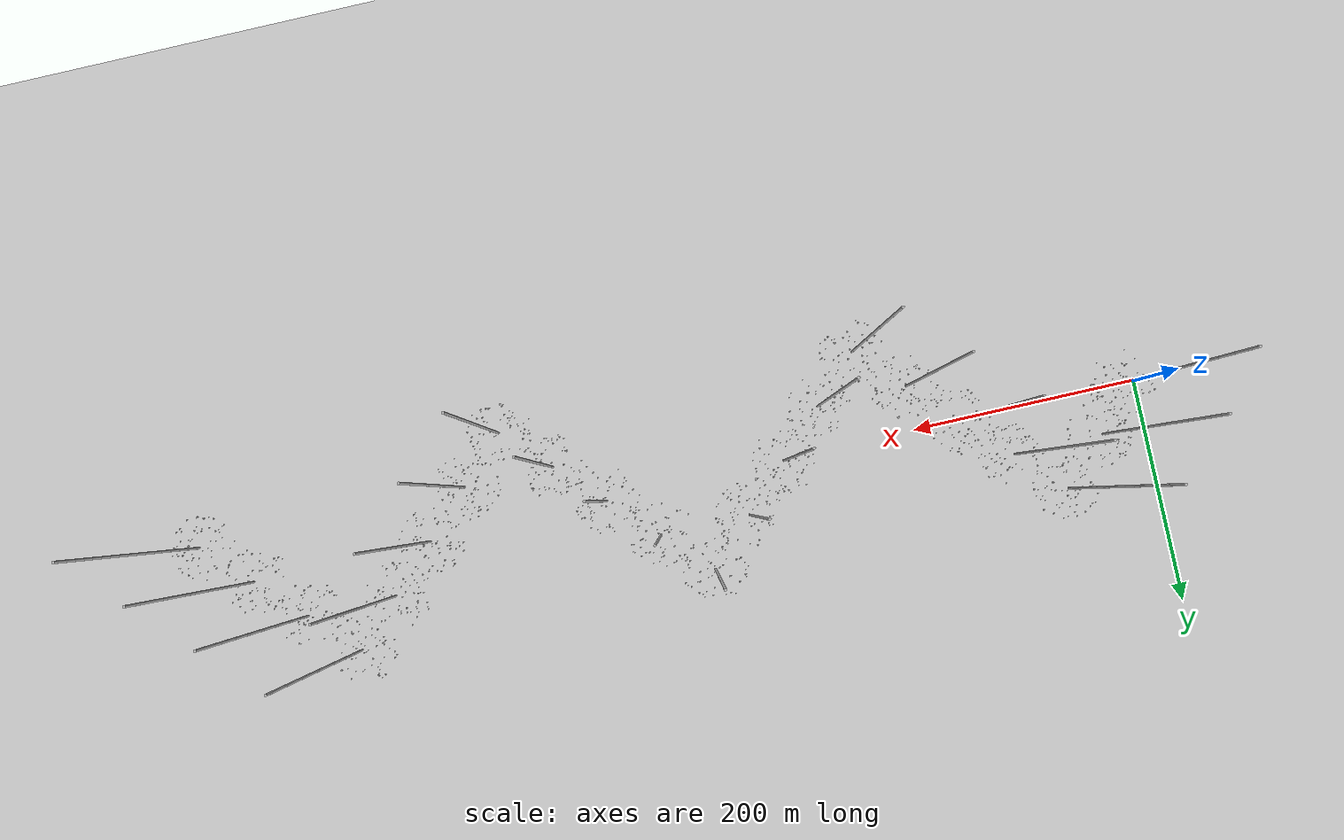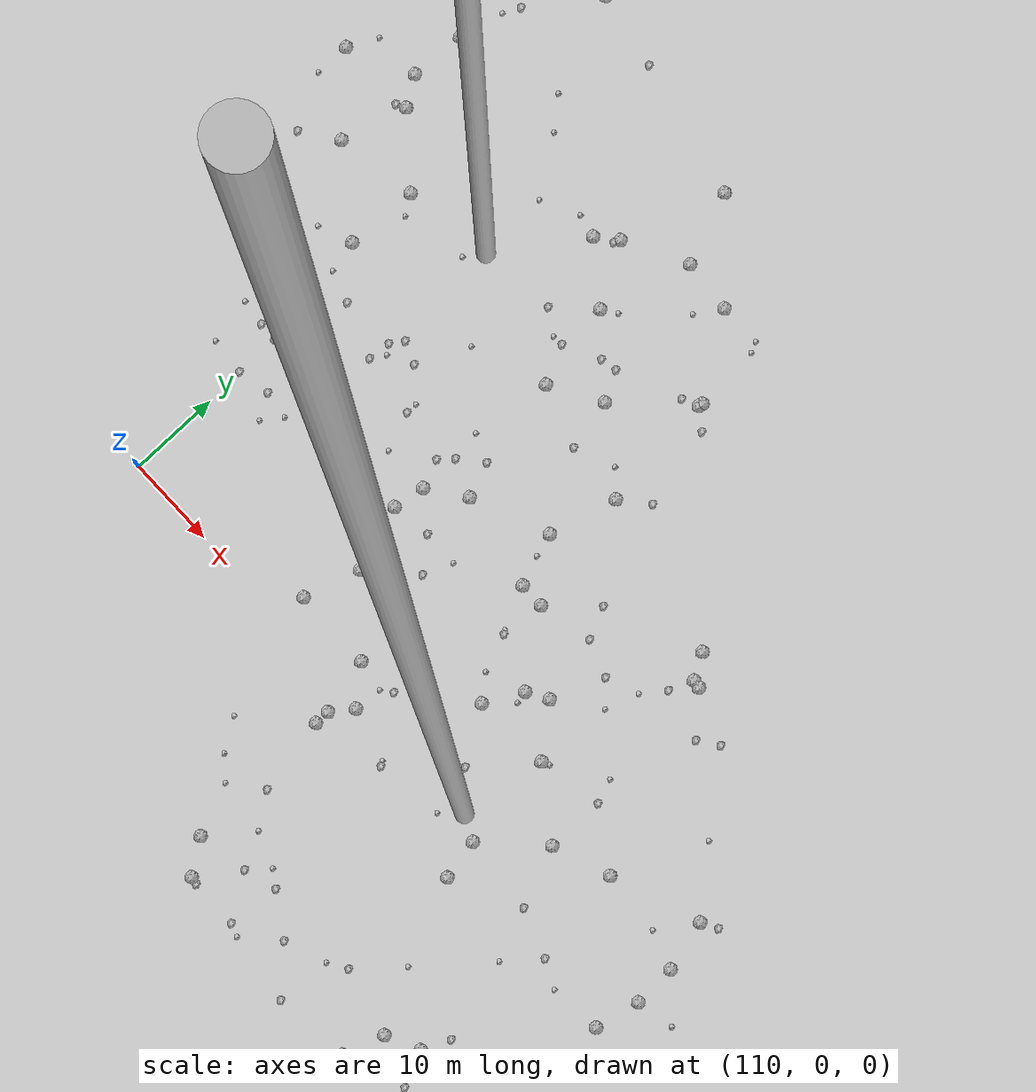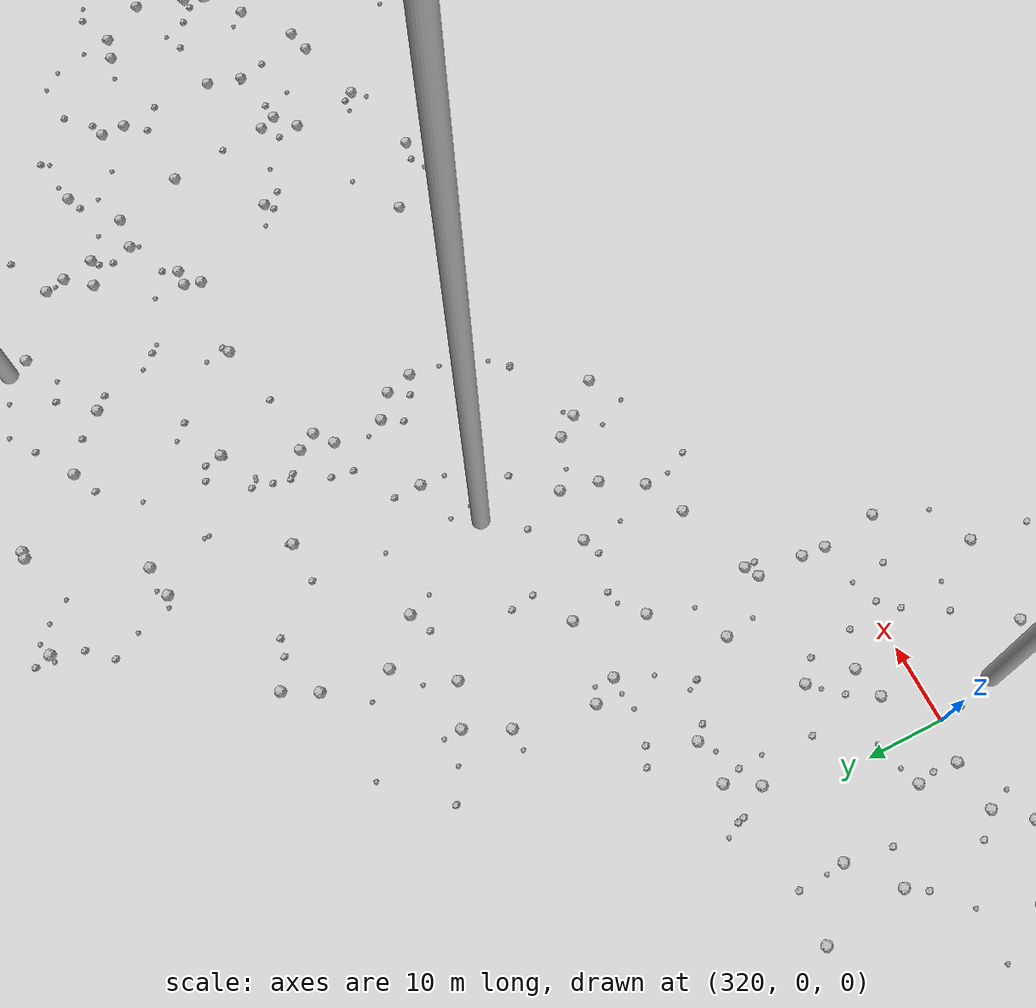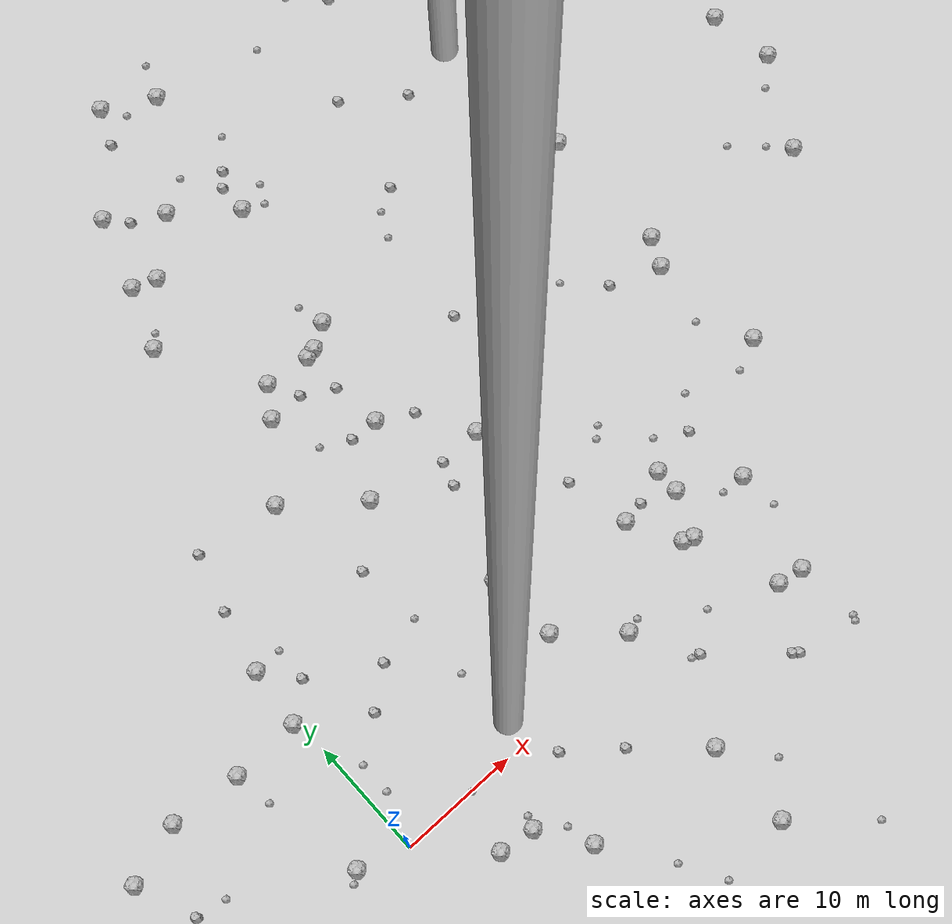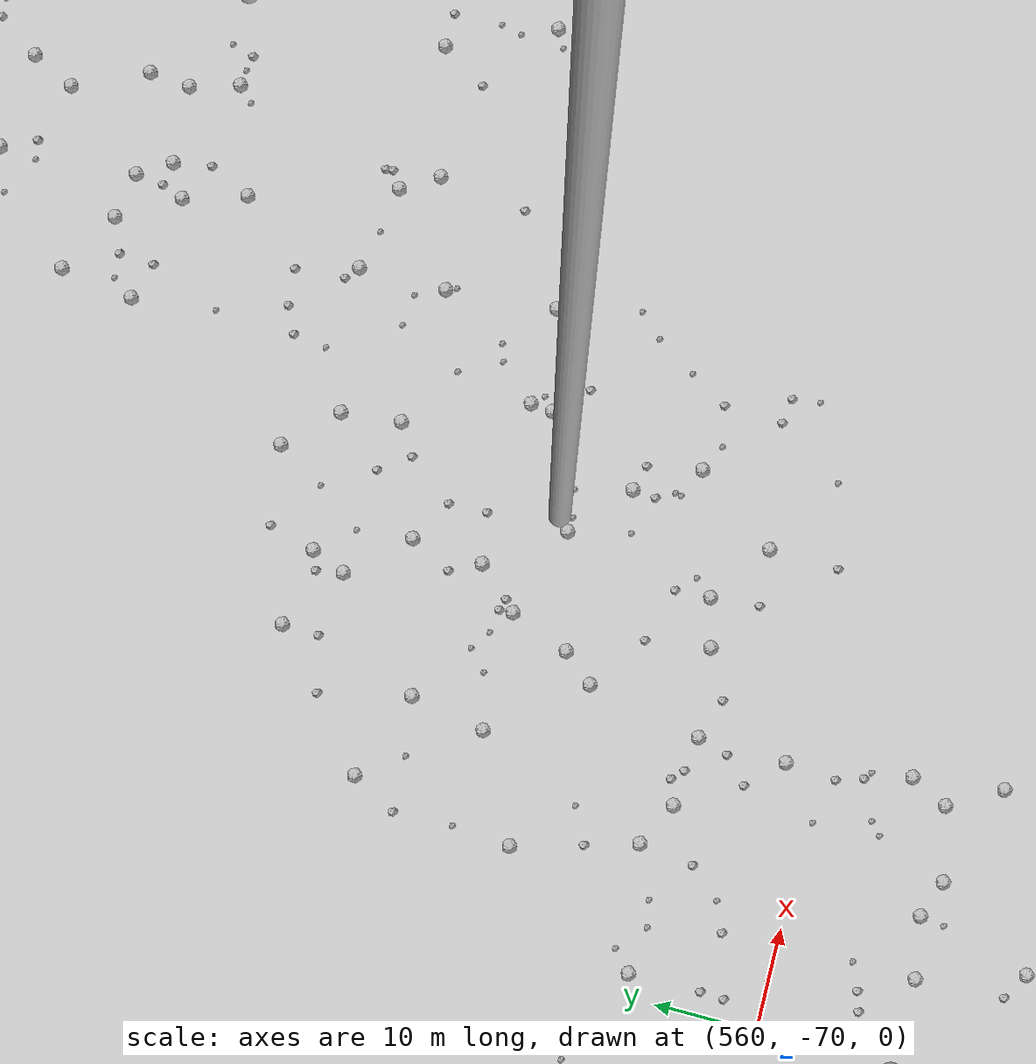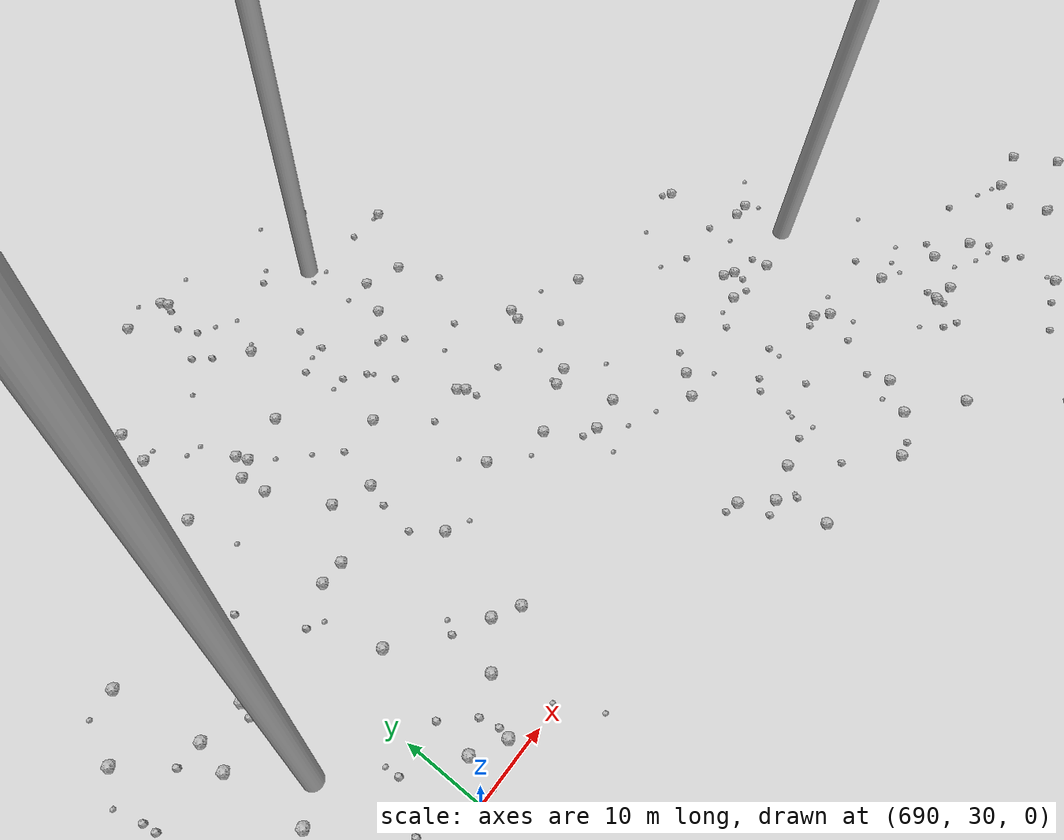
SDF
<sdf version="1.6">
 <world name="default">
  <include><uri>model://custom_ground</uri></include>
  <include><uri>model://sun</uri></include>
  <spherical_coordinates>
   <surface_model>EARTH_WGS84</surface_model>
   <latitude_deg>38.161479</latitude_deg>
   <longitude_deg>-122.454630</longitude_deg>
   <elevation>488.0</elevation>
   <heading_deg>90</heading_deg>
  </spherical_coordinates>
  <model name="rock1_0_0">
   <include><uri>model://rock1</uri><pose>39.00782874264638 4.000200810997299 0.5 0 0 0</pose></include>
  </model>
  <model name="rock1_0_1">
   <include><uri>model://rock1</uri><pose>-17.21298650060218 11.812632143164358 0.5 0 0 0</pose></include>
  </model>
  <model name="rock1_0_2">
   <include><uri>model://rock1</uri><pose>37.1797456083829 -4.508111469300815 0.5 0 0 0</pose></include>
  </model>
  <model name="rock1_0_3">
   <include><uri>model://rock1</uri><pose>-4.022800164153924 1.4226489339586799 0.5 0 0 0</pose></include>
  </model>
  <model name="rock1_0_4">
   <include><uri>model://rock1</uri><pose>22.304358731930016 -17.475497171580237 0.5 0 0 0</pose></include>
  </model>
  <model name="rock1_0_5">
   <include><uri>model://rock1</uri><pose>9.875731827637612 27.20153999997479 0.5 0 0 0</pose></include>
  </model>
  <model name="rock1_0_6">
   <include><uri>model://rock1</uri><pose>34.27448514048011 8.854126465477336 0.5 0 0 0</pose></include>
  </model>
  <model name="rock1_0_7">
   <include><uri>model://rock1</uri><pose>35.017381667392186 -4.143441351838046 0.5 0 0 0</pose></include>
  </model>
  <model name="rock1_0_8">
   <include><uri>model://rock1</uri><pose>10.542896415734589 -9.231312079236755 0.5 0 0 0</pose></include>
  </model>
  <model name="rock1_0_9">
   <include><uri>model://rock1</uri><pose>4.204335739118839 -15.002152425424516 0.5 0 0 0</pose></include>
  </model>
  <model name="rock1_0_10">
   <include><uri>model://rock1</uri><pose>-10.050826282383692 -2.8381125024878457 0.5 0 0 0</pose></include>
  </model>
  <model name="rock1_0_11">
   <include><uri>model://rock1</uri><pose>31.791769294671134 3.387831658192887 0.5 0 0 0</pose></include>
  </model>
  <model name="rock1_0_12">
   <include><uri>model://rock1</uri><pose>7.863234645827358 -5.275506037510148 0.5 0 0 0</pose></include>
  </model>
  <model name="rock1_0_13">
   <include><uri>model://rock1</uri><pose>22.695051304192916 13.903614760831758 0.5 0 0 0</pose></include>
  </model>
  <model name="rock1_0_14">
   <include><uri>model://rock1</uri><pose>32.64508349576532 3.0497121105837692 0.5 0 0 0</pose></include>
  </model>
  <model name="rock1_0_15">
   <include><uri>model://rock1</uri><pose>2.666469860374942 -15.765219007327303 0.5 0 0 0</pose></include>
  </model>
  <model name="rock1_0_16">
   <include><uri>model://rock1</uri><pose>34.23047967826186 6.734056890343247 0.5 0 0 0</pose></include>
  </model>
  <model name="rock1_0_17">
   <include><uri>model://rock1</uri><pose>18.624409449871777 11.065526506576404 0.5 0 0 0</pose></include>
  </model>
  <model name="rock1_0_18">
   <include><uri>model://rock1</uri><pose>-6.143668947695291 12.889030794224809 0.5 0 0 0</pose></include>
  </model>
  <model name="rock1_0_19">
   <include><uri>model://rock1</uri><pose>-12.124062947898448 13.38079681394953 0.5 0 0 0</pose></include>
  </model>
  <model name="rock1_0_20">
   <include><uri>model://rock1</uri><pose>-0.3942462875971451 13.051859913297271 0.5 0 0 0</pose></include>
  </model>
  <model name="rock1_0_21">
   <include><uri>model://rock1</uri><pose>0.14181704432165887 18.069167937783668 0.5 0 0 0</pose></include>
  </model>
  <model name="rock1_0_22">
   <include><uri>model://rock1</uri><pose>22.407912403471123 -10.110646810274186 0.5 0 0 0</pose></include>
  </model>
  <model name="rock1_0_23">
   <include><uri>model://rock1</uri><pose>23.627605341010188 0.8990585939026161 0.5 0 0 0</pose></include>
  </model>
  <model name="rock1_0_24">
   <include><uri>model://rock1</uri><pose>18.980194772403735 5.003210001196784 0.5 0 0 0</pose></include>
  </model>
  <model name="rock1_0_25">
   <include><uri>model://rock1</uri><pose>29.536247102335437 7.55964429712207 0.5 0 0 0</pose></include>
  </model>
  <model name="rock1_0_26">
   <include><uri>model://rock1</uri><pose>4.896204941657427 -4.8788702981881436 0.5 0 0 0</pose></include>
  </model>
  <model name="rock2_0_0">
   <include><uri>model://rock2</uri><pose>-6.009146116089564 -18.959457464373312 0.3 0 0 0</pose></include>
  </model>
  <model name="rock2_0_1">
   <include><uri>model://rock2</uri><pose>-5.241232983919504 -6.090549567524651 0.3 0 0 0</pose></include>
  </model>
  <model name="rock2_0_2">
   <include><uri>model://rock2</uri><pose>1.3119599324578743 23.377046684366114 0.3 0 0 0</pose></include>
  </model>
  <model name="rock2_0_3">
   <include><uri>model://rock2</uri><pose>31.932369752239048 -8.825399779976664 0.3 0 0 0</pose></include>
  </model>
  <model name="rock2_0_4">
   <include><uri>model://rock2</uri><pose>4.322503758589104 -15.60846851313724 0.3 0 0 0</pose></include>
  </model>
  <model name="rock2_0_5">
   <include><uri>model://rock2</uri><pose>5.462342948610612 -16.690291573524725 0.3 0 0 0</pose></include>
  </model>
  <model name="rock2_0_6">
   <include><uri>model://rock2</uri><pose>6.692051148042339 -17.5421284812003 0.3 0 0 0</pose></include>
  </model>
  <model name="rock2_0_7">
   <include><uri>model://rock2</uri><pose>1.32774126318796 -28.02670629251604 0.3 0 0 0</pose></include>
  </model>
  <model name="rock2_0_8">
   <include><uri>model://rock2</uri><pose>38.40056803908574 9.632337669620952 0.3 0 0 0</pose></include>
  </model>
  <model name="rock2_0_9">
   <include><uri>model://rock2</uri><pose>-13.703243226534301 3.1506584168229637 0.3 0 0 0</pose></include>
  </model>
  <model name="rock2_0_10">
   <include><uri>model://rock2</uri><pose>-15.312900786197837 6.8891173916460104 0.3 0 0 0</pose></include>
  </model>
  <model name="rock2_0_11">
   <include><uri>model://rock2</uri><pose>2.7634984590587344 28.26363722420605 0.3 0 0 0</pose></include>
  </model>
  <model name="rock2_0_12">
   <include><uri>model://rock2</uri><pose>28.39429345547437 12.974020109876719 0.3 0 0 0</pose></include>
  </model>
  <model name="rock2_0_13">
   <include><uri>model://rock2</uri><pose>26.549311937706804 -4.043764254899706 0.3 0 0 0</pose></include>
  </model>
  <model name="rock2_0_14">
   <include><uri>model://rock2</uri><pose>2.7702033035819404 -17.052390402370897 0.3 0 0 0</pose></include>
  </model>
  <model name="rock2_0_15">
   <include><uri>model://rock2</uri><pose>7.88554544243549 11.979606047727835 0.3 0 0 0</pose></include>
  </model>
  <model name="rock2_0_16">
   <include><uri>model://rock2</uri><pose>32.37066117506696 -9.143057063482466 0.3 0 0 0</pose></include>
  </model>
  <model name="rock2_0_17">
   <include><uri>model://rock2</uri><pose>11.432849462323013 18.56214435046342 0.3 0 0 0</pose></include>
  </model>
  <model name="rock2_0_18">
   <include><uri>model://rock2</uri><pose>21.440908723428834 18.963564887207077 0.3 0 0 0</pose></include>
  </model>
  <model name="rock2_0_19">
   <include><uri>model://rock2</uri><pose>10.341524668905052 -22.800047261741845 0.3 0 0 0</pose></include>
  </model>
  <model name="rock2_0_20">
   <include><uri>model://rock2</uri><pose>13.273276796178095 -2.2558285275539625 0.3 0 0 0</pose></include>
  </model>
  <model name="rock2_0_21">
   <include><uri>model://rock2</uri><pose>2.376828843323004 15.303560308462949 0.3 0 0 0</pose></include>
  </model>
  <model name="rock2_0_22">
   <include><uri>model://rock2</uri><pose>17.276872743576426 -5.485330139964368 0.3 0 0 0</pose></include>
  </model>
  <model name="rock2_0_23">
   <include><uri>model://rock2</uri><pose>-16.38839166744875 6.509454976840857 0.3 0 0 0</pose></include>
  </model>
  <model name="rock2_0_24">
   <include><uri>model://rock2</uri><pose>-2.4133459496452154 -8.459869591609262 0.3 0 0 0</pose></include>
  </model>
  <model name="rock2_0_25">
   <include><uri>model://rock2</uri><pose>31.431966842224078 7.878367365401715 0.3 0 0 0</pose></include>
  </model>
  <model name="rock2_0_26">
   <include><uri>model://rock2</uri><pose>4.789352397676275 9.544169840015094 0.3 0 0 0</pose></include>
  </model>
  <model name="rock3_0_0">
   <include><uri>model://rock3</uri><pose>-12.809252991426794 6.421757443177782 0.2 0 0 0</pose></include>
  </model>
  <model name="rock3_0_1">
   <include><uri>model://rock3</uri><pose>1.4708153076336181 4.337653654683258 0.2 0 0 0</pose></include>
  </model>
  <model name="rock3_0_2">
   <include><uri>model://rock3</uri><pose>37.57296478796628 -9.86403702332262 0.2 0 0 0</pose></include>
  </model>
  <model name="rock3_0_3">
   <include><uri>model://rock3</uri><pose>11.783350671649668 7.265941744915523 0.2 0 0 0</pose></include>
  </model>
  <model name="rock3_0_4">
   <include><uri>model://rock3</uri><pose>29.434103599192788 -1.8787738374438838 0.2 0 0 0</pose></include>
  </model>
  <model name="rock3_0_5">
   <include><uri>model://rock3</uri><pose>-4.967796242398565 0.7662248818379851 0.2 0 0 0</pose></include>
  </model>
  <model name="rock3_0_6">
   <include><uri>model://rock3</uri><pose>2.458893633795036 18.154451086278215 0.2 0 0 0</pose></include>
  </model>
  <model name="rock3_0_7">
   <include><uri>model://rock3</uri><pose>39.22860538777595 0.6999136554321481 0.2 0 0 0</pose></include>
  </model>
  <model name="rock3_0_8">
   <include><uri>model://rock3</uri><pose>9.91657470493806 -6.889724811017299 0.2 0 0 0</pose></include>
  </model>
  <model name="rock3_0_9">
   <include><uri>model://rock3</uri><pose>0.054692279045244874 -10.107309300087866 0.2 0 0 0</pose></include>
  </model>
  <model name="rock3_0_10">
   <include><uri>model://rock3</uri><pose>16.191706439116885 -18.027496592083608 0.2 0 0 0</pose></include>
  </model>
  <model name="rock3_0_11">
   <include><uri>model://rock3</uri><pose>13.942810749574427 4.949723679055445 0.2 0 0 0</pose></include>
  </model>
  <model name="rock3_0_12">
   <include><uri>model://rock3</uri><pose>14.224714054061764 -14.5423913085921 0.2 0 0 0</pose></include>
  </model>
  <model name="rock3_0_13">
   <include><uri>model://rock3</uri><pose>8.213384492906432 -4.261557267791037 0.2 0 0 0</pose></include>
  </model>
  <model name="rock3_0_14">
   <include><uri>model://rock3</uri><pose>1.4701252326644507 7.07207276737563 0.2 0 0 0</pose></include>
  </model>
  <model name="rock3_0_15">
   <include><uri>model://rock3</uri><pose>25.466996429066633 -13.923488029983545 0.2 0 0 0</pose></include>
  </model>
  <model name="rock3_0_16">
   <include><uri>model://rock3</uri><pose>24.840502210542155 1.2517137208708462 0.2 0 0 0</pose></include>
  </model>
  <model name="rock3_0_17">
   <include><uri>model://rock3</uri><pose>-15.008875430120725 -13.389301100445028 0.2 0 0 0</pose></include>
  </model>
  <model name="rock3_0_18">
   <include><uri>model://rock3</uri><pose>27.949501530258033 -22.584559473349458 0.2 0 0 0</pose></include>
  </model>
  <model name="rock3_0_19">
   <include><uri>model://rock3</uri><pose>11.950187284205857 12.977201777085114 0.2 0 0 0</pose></include>
  </model>
  <model name="rock3_0_20">
   <include><uri>model://rock3</uri><pose>37.36292789119608 -10.304271612984401 0.2 0 0 0</pose></include>
  </model>
  <model name="rock3_0_21">
   <include><uri>model://rock3</uri><pose>36.93523816707797 4.107486043352594 0.2 0 0 0</pose></include>
  </model>
  <model name="rock3_0_22">
   <include><uri>model://rock3</uri><pose>17.54847274652751 -26.707658093663426 0.2 0 0 0</pose></include>
  </model>
  <model name="rock3_0_23">
   <include><uri>model://rock3</uri><pose>35.89225741134664 11.123387873039341 0.2 0 0 0</pose></include>
  </model>
  <model name="rock3_0_24">
   <include><uri>model://rock3</uri><pose>25.848077258524782 -3.854661214333163 0.2 0 0 0</pose></include>
  </model>
  <model name="rock3_0_25">
   <include><uri>model://rock3</uri><pose>-5.742859883866643 9.668316584356155 0.2 0 0 0</pose></include>
  </model>
  <model name="rock3_0_26">
   <include><uri>model://rock3</uri><pose>6.28796171238551 -0.023023897339239596 0.2 0 0 0</pose></include>
  </model>
  <model name="rock1_1_0">
   <include><uri>model://rock1</uri><pose>14.29422106951656 32.842449665327734 0.5 0 0 0</pose></include>
  </model>
  <model name="rock1_1_1">
   <include><uri>model://rock1</uri><pose>52.66314352789866 49.98157420214023 0.5 0 0 0</pose></include>
  </model>
  <model name="rock1_1_2">
   <include><uri>model://rock1</uri><pose>47.724728653185274 11.799384842030918 0.5 0 0 0</pose></include>
  </model>
  <model name="rock1_1_3">
   <include><uri>model://rock1</uri><pose>47.70989324822281 35.20359660436799 0.5 0 0 0</pose></include>
  </model>
  <model name="rock1_1_4">
   <include><uri>model://rock1</uri><pose>20.375957309910632 27.14217851458914 0.5 0 0 0</pose></include>
  </model>
  <model name="rock1_1_5">
   <include><uri>model://rock1</uri><pose>65.42716332545453 34.73964603207999 0.5 0 0 0</pose></include>
  </model>
  <model name="rock1_1_6">
   <include><uri>model://rock1</uri><pose>15.146512290570284 55.36936249076853 0.5 0 0 0</pose></include>
  </model>
  <model name="rock1_1_7">
   <include><uri>model://rock1</uri><pose>15.730624036897858 22.476240573819837 0.5 0 0 0</pose></include>
  </model>
  <model name="rock1_1_8">
   <include><uri>model://rock1</uri><pose>24.284066235119376 48.31863994727442 0.5 0 0 0</pose></include>
  </model>
  <model name="rock1_1_9">
   <include><uri>model://rock1</uri><pose>22.70504431175214 36.36989784352167 0.5 0 0 0</pose></include>
  </model>
  <model name="rock1_1_10">
   <include><uri>model://rock1</uri><pose>53.58857485232586 58.70219723612011 0.5 0 0 0</pose></include>
  </model>
  <model name="rock1_1_11">
   <include><uri>model://rock1</uri><pose>15.161053340570405 48.336951119511 0.5 0 0 0</pose></include>
  </model>
  <model name="rock1_1_12">
   <include><uri>model://rock1</uri><pose>25.52347650669443 60.921763304209314 0.5 0 0 0</pose></include>
  </model>
  <model name="rock1_1_13">
   <include><uri>model://rock1</uri><pose>34.29617265523535 68.39293991922597 0.5 0 0 0</pose></include>
  </model>
  <model name="rock1_1_14">
   <include><uri>model://rock1</uri><pose>21.313886827257647 63.20141108800863 0.5 0 0 0</pose></include>
  </model>
  <model name="rock1_1_15">
   <include><uri>model://rock1</uri><pose>47.638445529420636 23.771637422244975 0.5 0 0 0</pose></include>
  </model>
  <model name="rock1_1_16">
   <include><uri>model://rock1</uri><pose>13.122729800207829 49.05783055890196 0.5 0 0 0</pose></include>
  </model>
  <model name="rock1_1_17">
   <include><uri>model://rock1</uri><pose>11.09010994409864 43.81520123007113 0.5 0 0 0</pose></include>
  </model>
  <model name="rock1_1_18">
   <include><uri>model://rock1</uri><pose>61.90914624337126 21.616820830824057 0.5 0 0 0</pose></include>
  </model>
  <model name="rock1_1_19">
   <include><uri>model://rock1</uri><pose>25.77834896866478 21.026525245111863 0.5 0 0 0</pose></include>
  </model>
  <model name="rock1_1_20">
   <include><uri>model://rock1</uri><pose>20.70902624470662 35.103383153663195 0.5 0 0 0</pose></include>
  </model>
  <model name="rock1_1_21">
   <include><uri>model://rock1</uri><pose>15.97337656488152 35.310419618775455 0.5 0 0 0</pose></include>
  </model>
  <model name="rock1_1_22">
   <include><uri>model://rock1</uri><pose>66.29971745424669 29.18030364670633 0.5 0 0 0</pose></include>
  </model>
  <model name="rock1_1_23">
   <include><uri>model://rock1</uri><pose>67.46907460122767 38.10488321208767 0.5 0 0 0</pose></include>
  </model>
  <model name="rock1_1_24">
   <include><uri>model://rock1</uri><pose>19.42324078798434 52.274360706790624 0.5 0 0 0</pose></include>
  </model>
  <model name="rock1_1_25">
   <include><uri>model://rock1</uri><pose>46.45236904240486 21.37978809664085 0.5 0 0 0</pose></include>
  </model>
  <model name="rock1_1_26">
   <include><uri>model://rock1</uri><pose>19.848501775117505 34.88922181515172 0.5 0 0 0</pose></include>
  </model>
  <model name="rock2_1_0">
   <include><uri>model://rock2</uri><pose>27.420321113815984 20.657382347337496 0.3 0 0 0</pose></include>
  </model>
  <model name="rock2_1_1">
   <include><uri>model://rock2</uri><pose>43.892903492236584 69.06951780632696 0.3 0 0 0</pose></include>
  </model>
  <model name="rock2_1_2">
   <include><uri>model://rock2</uri><pose>19.874520251041766 60.19446645681081 0.3 0 0 0</pose></include>
  </model>
  <model name="rock2_1_3">
   <include><uri>model://rock2</uri><pose>16.642493404313868 53.68810989401224 0.3 0 0 0</pose></include>
  </model>
  <model name="rock2_1_4">
   <include><uri>model://rock2</uri><pose>36.53783865857432 50.45852339220116 0.3 0 0 0</pose></include>
  </model>
  <model name="rock2_1_5">
   <include><uri>model://rock2</uri><pose>25.234276189604568 52.10103668530059 0.3 0 0 0</pose></include>
  </model>
  <model name="rock2_1_6">
   <include><uri>model://rock2</uri><pose>22.07029994919176 20.976113121606055 0.3 0 0 0</pose></include>
  </model>
  <model name="rock2_1_7">
   <include><uri>model://rock2</uri><pose>24.12175770212339 15.185583917553977 0.3 0 0 0</pose></include>
  </model>
  <model name="rock2_1_8">
   <include><uri>model://rock2</uri><pose>24.317888878776337 14.876962721407136 0.3 0 0 0</pose></include>
  </model>
  <model name="rock2_1_9">
   <include><uri>model://rock2</uri><pose>63.7037231755126 39.54864653246649 0.3 0 0 0</pose></include>
  </model>
  <model name="rock2_1_10">
   <include><uri>model://rock2</uri><pose>52.33664814506483 57.800092159188246 0.3 0 0 0</pose></include>
  </model>
  <model name="rock2_1_11">
   <include><uri>model://rock2</uri><pose>17.9438099084695 27.286798679355254 0.3 0 0 0</pose></include>
  </model>
  <model name="rock2_1_12">
   <include><uri>model://rock2</uri><pose>34.643860476964974 41.633452402062545 0.3 0 0 0</pose></include>
  </model>
  <model name="rock2_1_13">
   <include><uri>model://rock2</uri><pose>39.65388701819815 60.98341927161777 0.3 0 0 0</pose></include>
  </model>
  <model name="rock2_1_14">
   <include><uri>model://rock2</uri><pose>41.61692118182637 62.268463325718734 0.3 0 0 0</pose></include>
  </model>
  <model name="rock2_1_15">
   <include><uri>model://rock2</uri><pose>23.169057838203535 25.583108486912394 0.3 0 0 0</pose></include>
  </model>
  <model name="rock2_1_16">
   <include><uri>model://rock2</uri><pose>41.34295632319208 46.946786905592205 0.3 0 0 0</pose></include>
  </model>
  <model name="rock2_1_17">
   <include><uri>model://rock2</uri><pose>64.57105565834988 47.60134535869438 0.3 0 0 0</pose></include>
  </model>
  <model name="rock2_1_18">
   <include><uri>model://rock2</uri><pose>52.45176244303711 57.93020443325109 0.3 0 0 0</pose></include>
  </model>
  <model name="rock2_1_19">
   <include><uri>model://rock2</uri><pose>24.265220685812814 50.935374694535064 0.3 0 0 0</pose></include>
  </model>
  <model name="rock2_1_20">
   <include><uri>model://rock2</uri><pose>30.993133158331187 29.617720435313696 0.3 0 0 0</pose></include>
  </model>
  <model name="rock2_1_21">
   <include><uri>model://rock2</uri><pose>19.835867660505848 31.428196572909147 0.3 0 0 0</pose></include>
  </model>
  <model name="rock2_1_22">
   <include><uri>model://rock2</uri><pose>30.440595379068995 21.59845357638053 0.3 0 0 0</pose></include>
  </model>
  <model name="rock2_1_23">
   <include><uri>model://rock2</uri><pose>42.15557101553064 58.25768535350972 0.3 0 0 0</pose></include>
  </model>
  <model name="rock2_1_24">
   <include><uri>model://rock2</uri><pose>42.19728770428189 23.02578346742424 0.3 0 0 0</pose></include>
  </model>
  <model name="rock2_1_25">
   <include><uri>model://rock2</uri><pose>17.252218844310054 32.89433955330639 0.3 0 0 0</pose></include>
  </model>
  <model name="rock2_1_26">
   <include><uri>model://rock2</uri><pose>48.077505968745015 40.017201193590864 0.3 0 0 0</pose></include>
  </model>
  <model name="rock3_1_0">
   <include><uri>model://rock3</uri><pose>26.668434537509025 63.88096235501449 0.2 0 0 0</pose></include>
  </model>
  <model name="rock3_1_1">
   <include><uri>model://rock3</uri><pose>51.50511370491737 46.705325400419554 0.2 0 0 0</pose></include>
  </model>
  <model name="rock3_1_2">
   <include><uri>model://rock3</uri><pose>33.322982189563135 14.896371128079249 0.2 0 0 0</pose></include>
  </model>
  <model name="rock3_1_3">
   <include><uri>model://rock3</uri><pose>22.543930859818463 61.37943431968302 0.2 0 0 0</pose></include>
  </model>
  <model name="rock3_1_4">
   <include><uri>model://rock3</uri><pose>45.031879998926705 10.582961480492719 0.2 0 0 0</pose></include>
  </model>
  <model name="rock3_1_5">
   <include><uri>model://rock3</uri><pose>11.986949135380925 44.836172700596656 0.2 0 0 0</pose></include>
  </model>
  <model name="rock3_1_6">
   <include><uri>model://rock3</uri><pose>39.333119364493626 25.90396482397419 0.2 0 0 0</pose></include>
  </model>
  <model name="rock3_1_7">
   <include><uri>model://rock3</uri><pose>34.59969780421772 58.70421652215213 0.2 0 0 0</pose></include>
  </model>
  <model name="rock3_1_8">
   <include><uri>model://rock3</uri><pose>36.633132955613306 27.982192746219255 0.2 0 0 0</pose></include>
  </model>
  <model name="rock3_1_9">
   <include><uri>model://rock3</uri><pose>47.846085386426935 11.957776302573649 0.2 0 0 0</pose></include>
  </model>
  <model name="rock3_1_10">
   <include><uri>model://rock3</uri><pose>40.38832532177756 12.133347494018405 0.2 0 0 0</pose></include>
  </model>
  <model name="rock3_1_11">
   <include><uri>model://rock3</uri><pose>15.560133988846513 28.507804360460703 0.2 0 0 0</pose></include>
  </model>
  <model name="rock3_1_12">
   <include><uri>model://rock3</uri><pose>57.97841481805556 25.49233165995485 0.2 0 0 0</pose></include>
  </model>
  <model name="rock3_1_13">
   <include><uri>model://rock3</uri><pose>32.626118047557654 40.48729437243044 0.2 0 0 0</pose></include>
  </model>
  <model name="rock3_1_14">
   <include><uri>model://rock3</uri><pose>47.350298164333076 49.29853764057737 0.2 0 0 0</pose></include>
  </model>
  <model name="rock3_1_15">
   <include><uri>model://rock3</uri><pose>60.348597818474104 23.276972608322843 0.2 0 0 0</pose></include>
  </model>
  <model name="rock3_1_16">
   <include><uri>model://rock3</uri><pose>45.271705166562285 15.98607216782118 0.2 0 0 0</pose></include>
  </model>
  <model name="rock3_1_17">
   <include><uri>model://rock3</uri><pose>25.951928199604392 47.53692810097724 0.2 0 0 0</pose></include>
  </model>
  <model name="rock3_1_18">
   <include><uri>model://rock3</uri><pose>26.79648392980864 49.119027735281776 0.2 0 0 0</pose></include>
  </model>
  <model name="rock3_1_19">
   <include><uri>model://rock3</uri><pose>50.4943471372594 67.68798594460006 0.2 0 0 0</pose></include>
  </model>
  <model name="rock3_1_20">
   <include><uri>model://rock3</uri><pose>22.070203159676318 38.67048859228799 0.2 0 0 0</pose></include>
  </model>
  <model name="rock3_1_21">
   <include><uri>model://rock3</uri><pose>27.212872218984895 54.54797532672594 0.2 0 0 0</pose></include>
  </model>
  <model name="rock3_1_22">
   <include><uri>model://rock3</uri><pose>32.46402052383159 14.140487321354193 0.2 0 0 0</pose></include>
  </model>
  <model name="rock3_1_23">
   <include><uri>model://rock3</uri><pose>31.548276880296214 38.37238840716711 0.2 0 0 0</pose></include>
  </model>
  <model name="rock3_1_24">
   <include><uri>model://rock3</uri><pose>22.20224770048408 53.97158820588706 0.2 0 0 0</pose></include>
  </model>
  <model name="rock3_1_25">
   <include><uri>model://rock3</uri><pose>63.803818442036665 56.79706452746423 0.2 0 0 0</pose></include>
  </model>
  <model name="rock3_1_26">
   <include><uri>model://rock3</uri><pose>64.06429577482862 27.161476197198727 0.2 0 0 0</pose></include>
  </model>
  <model name="rock1_2_0">
   <include><uri>model://rock1</uri><pose>59.44179347255118 98.49793446451883 0.5 0 0 0</pose></include>
  </model>
  <model name="rock1_2_1">
   <include><uri>model://rock1</uri><pose>107.28191789926754 74.80730366991892 0.5 0 0 0</pose></include>
  </model>
  <model name="rock1_2_2">
   <include><uri>model://rock1</uri><pose>76.77205697185506 58.08710442666829 0.5 0 0 0</pose></include>
  </model>
  <model name="rock1_2_3">
   <include><uri>model://rock1</uri><pose>64.79080746786174 82.30053365014253 0.5 0 0 0</pose></include>
  </model>
  <model name="rock1_2_4">
   <include><uri>model://rock1</uri><pose>66.52716840508305 54.02585163705481 0.5 0 0 0</pose></include>
  </model>
  <model name="rock1_2_5">
   <include><uri>model://rock1</uri><pose>95.2477314174788 99.6250899601092 0.5 0 0 0</pose></include>
  </model>
  <model name="rock1_2_6">
   <include><uri>model://rock1</uri><pose>83.02258197669904 59.80924396556497 0.5 0 0 0</pose></include>
  </model>
  <model name="rock1_2_7">
   <include><uri>model://rock1</uri><pose>72.94604984144587 89.73273999515135 0.5 0 0 0</pose></include>
  </model>
  <model name="rock1_2_8">
   <include><uri>model://rock1</uri><pose>56.74411235643072 79.9550901871456 0.5 0 0 0</pose></include>
  </model>
  <model name="rock1_2_9">
   <include><uri>model://rock1</uri><pose>72.35806096823822 57.58971530187186 0.5 0 0 0</pose></include>
  </model>
  <model name="rock1_2_10">
   <include><uri>model://rock1</uri><pose>67.46113289234091 104.35889491975422 0.5 0 0 0</pose></include>
  </model>
  <model name="rock1_2_11">
   <include><uri>model://rock1</uri><pose>75.23073528631957 106.34767359417319 0.5 0 0 0</pose></include>
  </model>
  <model name="rock1_2_12">
   <include><uri>model://rock1</uri><pose>52.65701074608321 90.8843720269034 0.5 0 0 0</pose></include>
  </model>
  <model name="rock1_2_13">
   <include><uri>model://rock1</uri><pose>76.6360642978199 102.55515162897208 0.5 0 0 0</pose></include>
  </model>
  <model name="rock1_2_14">
   <include><uri>model://rock1</uri><pose>93.36913195778538 66.25713872439388 0.5 0 0 0</pose></include>
  </model>
  <model name="rock1_2_15">
   <include><uri>model://rock1</uri><pose>73.78702677331643 96.6819291397934 0.5 0 0 0</pose></include>
  </model>
  <model name="rock1_2_16">
   <include><uri>model://rock1</uri><pose>67.15111966757331 84.40858816934744 0.5 0 0 0</pose></include>
  </model>
  <model name="rock1_2_17">
   <include><uri>model://rock1</uri><pose>88.81336407439092 79.88957225362327 0.5 0 0 0</pose></include>
  </model>
  <model name="rock1_2_18">
   <include><uri>model://rock1</uri><pose>61.82558941632347 63.57107901478007 0.5 0 0 0</pose></include>
  </model>
  <model name="rock1_2_19">
   <include><uri>model://rock1</uri><pose>89.7846462305973 72.33619883885551 0.5 0 0 0</pose></include>
  </model>
  <model name="rock1_2_20">
   <include><uri>model://rock1</uri><pose>73.39812976120626 53.4508282387639 0.5 0 0 0</pose></include>
  </model>
  <model name="rock1_2_21">
   <include><uri>model://rock1</uri><pose>102.96158731708783 94.30305056211643 0.5 0 0 0</pose></include>
  </model>
  <model name="rock1_2_22">
   <include><uri>model://rock1</uri><pose>78.13971459070109 59.626275516014395 0.5 0 0 0</pose></include>
  </model>
  <model name="rock1_2_23">
   <include><uri>model://rock1</uri><pose>79.38007424695077 86.72561437357163 0.5 0 0 0</pose></include>
  </model>
  <model name="rock1_2_24">
   <include><uri>model://rock1</uri><pose>106.92986512075205 68.92993368919764 0.5 0 0 0</pose></include>
  </model>
  <model name="rock1_2_25">
   <include><uri>model://rock1</uri><pose>70.30326497076047 87.5951590753576 0.5 0 0 0</pose></include>
  </model>
  <model name="rock1_2_26">
   <include><uri>model://rock1</uri><pose>61.86234292491653 100.33744715399845 0.5 0 0 0</pose></include>
  </model>
  <model name="rock2_2_0">
   <include><uri>model://rock2</uri><pose>89.68942101638726 79.93455071271369 0.3 0 0 0</pose></include>
  </model>
  <model name="rock2_2_1">
   <include><uri>model://rock2</uri><pose>60.66976750302638 79.13149489650854 0.3 0 0 0</pose></include>
  </model>
  <model name="rock2_2_2">
   <include><uri>model://rock2</uri><pose>55.08729742304376 82.60508983537181 0.3 0 0 0</pose></include>
  </model>
  <model name="rock2_2_3">
   <include><uri>model://rock2</uri><pose>85.40689715776003 92.3859367285605 0.3 0 0 0</pose></include>
  </model>
  <model name="rock2_2_4">
   <include><uri>model://rock2</uri><pose>77.44354100252774 80.57886021360906 0.3 0 0 0</pose></include>
  </model>
  <model name="rock2_2_5">
   <include><uri>model://rock2</uri><pose>99.71768139703968 86.61681148214315 0.3 0 0 0</pose></include>
  </model>
  <model name="rock2_2_6">
   <include><uri>model://rock2</uri><pose>75.74109489471753 64.65394290449126 0.3 0 0 0</pose></include>
  </model>
  <model name="rock2_2_7">
   <include><uri>model://rock2</uri><pose>76.0929063285648 66.09737761365491 0.3 0 0 0</pose></include>
  </model>
  <model name="rock2_2_8">
   <include><uri>model://rock2</uri><pose>80.77952631427746 89.05050282030001 0.3 0 0 0</pose></include>
  </model>
  <model name="rock2_2_9">
   <include><uri>model://rock2</uri><pose>62.558633285393284 72.55463267975345 0.3 0 0 0</pose></include>
  </model>
  <model name="rock2_2_10">
   <include><uri>model://rock2</uri><pose>80.13396882197509 60.56319591924603 0.3 0 0 0</pose></include>
  </model>
  <model name="rock2_2_11">
   <include><uri>model://rock2</uri><pose>88.48467807519773 73.01415674701563 0.3 0 0 0</pose></include>
  </model>
  <model name="rock2_2_12">
   <include><uri>model://rock2</uri><pose>71.6502227502455 84.60353656947137 0.3 0 0 0</pose></include>
  </model>
  <model name="rock2_2_13">
   <include><uri>model://rock2</uri><pose>70.17725736797267 99.70766416309854 0.3 0 0 0</pose></include>
  </model>
  <model name="rock2_2_14">
   <include><uri>model://rock2</uri><pose>101.16703992263209 82.41177092775781 0.3 0 0 0</pose></include>
  </model>
  <model name="rock2_2_15">
   <include><uri>model://rock2</uri><pose>79.30993964701155 96.95585870586507 0.3 0 0 0</pose></include>
  </model>
  <model name="rock2_2_16">
   <include><uri>model://rock2</uri><pose>70.90099411994562 76.57060271206421 0.3 0 0 0</pose></include>
  </model>
  <model name="rock2_2_17">
   <include><uri>model://rock2</uri><pose>104.06985882361033 75.69446122320119 0.3 0 0 0</pose></include>
  </model>
  <model name="rock2_2_18">
   <include><uri>model://rock2</uri><pose>59.95018113062841 72.11446072848918 0.3 0 0 0</pose></include>
  </model>
  <model name="rock2_2_19">
   <include><uri>model://rock2</uri><pose>79.31424836398152 54.66583202560738 0.3 0 0 0</pose></include>
  </model>
  <model name="rock2_2_20">
   <include><uri>model://rock2</uri><pose>64.3981357740951 68.28231407811546 0.3 0 0 0</pose></include>
  </model>
  <model name="rock2_2_21">
   <include><uri>model://rock2</uri><pose>89.16956942157071 95.50263057787012 0.3 0 0 0</pose></include>
  </model>
  <model name="rock2_2_22">
   <include><uri>model://rock2</uri><pose>83.24251019058767 104.74194329277077 0.3 0 0 0</pose></include>
  </model>
  <model name="rock2_2_23">
   <include><uri>model://rock2</uri><pose>106.69783022744352 81.00208463066035 0.3 0 0 0</pose></include>
  </model>
  <model name="rock2_2_24">
   <include><uri>model://rock2</uri><pose>57.51213246267395 67.8851988774063 0.3 0 0 0</pose></include>
  </model>
  <model name="rock2_2_25">
   <include><uri>model://rock2</uri><pose>97.46360236256308 61.77523814809197 0.3 0 0 0</pose></include>
  </model>
  <model name="rock2_2_26">
   <include><uri>model://rock2</uri><pose>77.02532880915018 90.28795168812786 0.3 0 0 0</pose></include>
  </model>
  <model name="rock3_2_0">
   <include><uri>model://rock3</uri><pose>78.52220716921617 82.5964795610648 0.2 0 0 0</pose></include>
  </model>
  <model name="rock3_2_1">
   <include><uri>model://rock3</uri><pose>69.29893004045675 104.40490366568733 0.2 0 0 0</pose></include>
  </model>
  <model name="rock3_2_2">
   <include><uri>model://rock3</uri><pose>76.79881889418186 73.76433532906917 0.2 0 0 0</pose></include>
  </model>
  <model name="rock3_2_3">
   <include><uri>model://rock3</uri><pose>90.05672084599371 58.74162623546104 0.2 0 0 0</pose></include>
  </model>
  <model name="rock3_2_4">
   <include><uri>model://rock3</uri><pose>93.73548301313942 89.57449733945725 0.2 0 0 0</pose></include>
  </model>
  <model name="rock3_2_5">
   <include><uri>model://rock3</uri><pose>56.14747870846111 98.14040535344841 0.2 0 0 0</pose></include>
  </model>
  <model name="rock3_2_6">
   <include><uri>model://rock3</uri><pose>89.14063878658303 84.03686549974739 0.2 0 0 0</pose></include>
  </model>
  <model name="rock3_2_7">
   <include><uri>model://rock3</uri><pose>92.27994978263739 78.45251766068603 0.2 0 0 0</pose></include>
  </model>
  <model name="rock3_2_8">
   <include><uri>model://rock3</uri><pose>105.2528534457879 68.5984340909392 0.2 0 0 0</pose></include>
  </model>
  <model name="rock3_2_9">
   <include><uri>model://rock3</uri><pose>103.5644851221156 84.87237325864824 0.2 0 0 0</pose></include>
  </model>
  <model name="rock3_2_10">
   <include><uri>model://rock3</uri><pose>87.2295287697805 105.6123256963175 0.2 0 0 0</pose></include>
  </model>
  <model name="rock3_2_11">
   <include><uri>model://rock3</uri><pose>78.1804899837642 65.76963064715981 0.2 0 0 0</pose></include>
  </model>
  <model name="rock3_2_12">
   <include><uri>model://rock3</uri><pose>86.84821221695393 58.73996129481982 0.2 0 0 0</pose></include>
  </model>
  <model name="rock3_2_13">
   <include><uri>model://rock3</uri><pose>83.08493739826429 81.5303802919207 0.2 0 0 0</pose></include>
  </model>
  <model name="rock3_2_14">
   <include><uri>model://rock3</uri><pose>78.0237470359225 95.88912576318987 0.2 0 0 0</pose></include>
  </model>
  <model name="rock3_2_15">
   <include><uri>model://rock3</uri><pose>95.61967814895957 74.46995168887912 0.2 0 0 0</pose></include>
  </model>
  <model name="rock3_2_16">
   <include><uri>model://rock3</uri><pose>57.78252422576687 92.56937125849146 0.2 0 0 0</pose></include>
  </model>
  <model name="rock3_2_17">
   <include><uri>model://rock3</uri><pose>64.71275366234005 73.46376708987374 0.2 0 0 0</pose></include>
  </model>
  <model name="rock3_2_18">
   <include><uri>model://rock3</uri><pose>76.67523966631613 104.41629138949996 0.2 0 0 0</pose></include>
  </model>
  <model name="rock3_2_19">
   <include><uri>model://rock3</uri><pose>80.8803487719685 54.043445228364504 0.2 0 0 0</pose></include>
  </model>
  <model name="rock3_2_20">
   <include><uri>model://rock3</uri><pose>75.93588919063849 95.67877686287574 0.2 0 0 0</pose></include>
  </model>
  <model name="rock3_2_21">
   <include><uri>model://rock3</uri><pose>67.96859582311828 69.19218999902127 0.2 0 0 0</pose></include>
  </model>
  <model name="rock3_2_22">
   <include><uri>model://rock3</uri><pose>61.47061448862335 59.2591883646283 0.2 0 0 0</pose></include>
  </model>
  <model name="rock3_2_23">
   <include><uri>model://rock3</uri><pose>100.86364862501468 59.812983197089224 0.2 0 0 0</pose></include>
  </model>
  <model name="rock3_2_24">
   <include><uri>model://rock3</uri><pose>97.6598951515646 75.93138704013404 0.2 0 0 0</pose></include>
  </model>
  <model name="rock3_2_25">
   <include><uri>model://rock3</uri><pose>91.0478174543712 92.85569056895272 0.2 0 0 0</pose></include>
  </model>
  <model name="rock3_2_26">
   <include><uri>model://rock3</uri><pose>76.75294562971743 51.332455524159045 0.2 0 0 0</pose></include>
  </model>
  <model name="rock1_3_0">
   <include><uri>model://rock1</uri><pose>101.27575912618072 27.81412042776247 0.5 0 0 0</pose></include>
  </model>
  <model name="rock1_3_1">
   <include><uri>model://rock1</uri><pose>131.15417504776244 16.57131797229644 0.5 0 0 0</pose></include>
  </model>
  <model name="rock1_3_2">
   <include><uri>model://rock1</uri><pose>126.69093541841951 52.64755380029145 0.5 0 0 0</pose></include>
  </model>
  <model name="rock1_3_3">
   <include><uri>model://rock1</uri><pose>135.71024641606112 22.951151412094056 0.5 0 0 0</pose></include>
  </model>
  <model name="rock1_3_4">
   <include><uri>model://rock1</uri><pose>139.25421487177795 55.6732491174933 0.5 0 0 0</pose></include>
  </model>
  <model name="rock1_3_5">
   <include><uri>model://rock1</uri><pose>146.16452882725923 33.893160966499096 0.5 0 0 0</pose></include>
  </model>
  <model name="rock1_3_6">
   <include><uri>model://rock1</uri><pose>99.72900237107523 54.90076557601568 0.5 0 0 0</pose></include>
  </model>
  <model name="rock1_3_7">
   <include><uri>model://rock1</uri><pose>133.459464930024 56.22026718995757 0.5 0 0 0</pose></include>
  </model>
  <model name="rock1_3_8">
   <include><uri>model://rock1</uri><pose>120.05813021797375 16.31449498095988 0.5 0 0 0</pose></include>
  </model>
  <model name="rock1_3_9">
   <include><uri>model://rock1</uri><pose>99.30340708678018 38.52184431597787 0.5 0 0 0</pose></include>
  </model>
  <model name="rock1_3_10">
   <include><uri>model://rock1</uri><pose>137.97772066747223 39.91252652320263 0.5 0 0 0</pose></include>
  </model>
  <model name="rock1_3_11">
   <include><uri>model://rock1</uri><pose>92.47158555212043 45.486102499056784 0.5 0 0 0</pose></include>
  </model>
  <model name="rock1_3_12">
   <include><uri>model://rock1</uri><pose>144.14872596670676 26.427971852341898 0.5 0 0 0</pose></include>
  </model>
  <model name="rock1_3_13">
   <include><uri>model://rock1</uri><pose>132.47384873071232 36.719708201003634 0.5 0 0 0</pose></include>
  </model>
  <model name="rock1_3_14">
   <include><uri>model://rock1</uri><pose>109.99375957245064 19.566593316155945 0.5 0 0 0</pose></include>
  </model>
  <model name="rock1_3_15">
   <include><uri>model://rock1</uri><pose>99.4165518128942 48.80264104630783 0.5 0 0 0</pose></include>
  </model>
  <model name="rock1_3_16">
   <include><uri>model://rock1</uri><pose>130.43680767306168 63.94569428699194 0.5 0 0 0</pose></include>
  </model>
  <model name="rock1_3_17">
   <include><uri>model://rock1</uri><pose>144.88174205044484 46.84340468569399 0.5 0 0 0</pose></include>
  </model>
  <model name="rock1_3_18">
   <include><uri>model://rock1</uri><pose>130.55498903850227 46.16682716863813 0.5 0 0 0</pose></include>
  </model>
  <model name="rock1_3_19">
   <include><uri>model://rock1</uri><pose>124.49472215759957 50.81504099547734 0.5 0 0 0</pose></include>
  </model>
  <model name="rock1_3_20">
   <include><uri>model://rock1</uri><pose>101.39711864407842 45.764987775287466 0.5 0 0 0</pose></include>
  </model>
  <model name="rock1_3_21">
   <include><uri>model://rock1</uri><pose>144.97560836802472 47.24624673679934 0.5 0 0 0</pose></include>
  </model>
  <model name="rock1_3_22">
   <include><uri>model://rock1</uri><pose>107.93571073330216 32.05982913821251 0.5 0 0 0</pose></include>
  </model>
  <model name="rock1_3_23">
   <include><uri>model://rock1</uri><pose>131.72523030173346 20.07626420883129 0.5 0 0 0</pose></include>
  </model>
  <model name="rock1_3_24">
   <include><uri>model://rock1</uri><pose>123.74394221428736 16.944909158724865 0.5 0 0 0</pose></include>
  </model>
  <model name="rock1_3_25">
   <include><uri>model://rock1</uri><pose>108.27452544898921 39.99955839428014 0.5 0 0 0</pose></include>
  </model>
  <model name="rock1_3_26">
   <include><uri>model://rock1</uri><pose>104.34620658066915 27.442054393605417 0.5 0 0 0</pose></include>
  </model>
  <model name="rock2_3_0">
   <include><uri>model://rock2</uri><pose>101.77182898595868 61.686876084163636 0.3 0 0 0</pose></include>
  </model>
  <model name="rock2_3_1">
   <include><uri>model://rock2</uri><pose>115.27718771591293 67.32346454127736 0.3 0 0 0</pose></include>
  </model>
  <model name="rock2_3_2">
   <include><uri>model://rock2</uri><pose>147.04034973689863 45.23381757761865 0.3 0 0 0</pose></include>
  </model>
  <model name="rock2_3_3">
   <include><uri>model://rock2</uri><pose>113.44619582698856 15.045116951546758 0.3 0 0 0</pose></include>
  </model>
  <model name="rock2_3_4">
   <include><uri>model://rock2</uri><pose>131.727662439877 24.64642934605925 0.3 0 0 0</pose></include>
  </model>
  <model name="rock2_3_5">
   <include><uri>model://rock2</uri><pose>143.1015021265968 46.04149146838019 0.3 0 0 0</pose></include>
  </model>
  <model name="rock2_3_6">
   <include><uri>model://rock2</uri><pose>139.22262302468027 34.388484077125966 0.3 0 0 0</pose></include>
  </model>
  <model name="rock2_3_7">
   <include><uri>model://rock2</uri><pose>127.6998044828119 13.926625084152938 0.3 0 0 0</pose></include>
  </model>
  <model name="rock2_3_8">
   <include><uri>model://rock2</uri><pose>126.36037250547992 51.999228140936815 0.3 0 0 0</pose></include>
  </model>
  <model name="rock2_3_9">
   <include><uri>model://rock2</uri><pose>149.09881748050694 36.37291852541897 0.3 0 0 0</pose></include>
  </model>
  <model name="rock2_3_10">
   <include><uri>model://rock2</uri><pose>126.66690118518636 42.422774469369095 0.3 0 0 0</pose></include>
  </model>
  <model name="rock2_3_11">
   <include><uri>model://rock2</uri><pose>118.2253161772927 27.705971541347633 0.3 0 0 0</pose></include>
  </model>
  <model name="rock2_3_12">
   <include><uri>model://rock2</uri><pose>121.1381568196135 16.71178466504474 0.3 0 0 0</pose></include>
  </model>
  <model name="rock2_3_13">
   <include><uri>model://rock2</uri><pose>100.33938785878294 45.24453174451752 0.3 0 0 0</pose></include>
  </model>
  <model name="rock2_3_14">
   <include><uri>model://rock2</uri><pose>121.61624844087495 28.1630648028227 0.3 0 0 0</pose></include>
  </model>
  <model name="rock2_3_15">
   <include><uri>model://rock2</uri><pose>134.23695610154485 26.72601962810023 0.3 0 0 0</pose></include>
  </model>
  <model name="rock2_3_16">
   <include><uri>model://rock2</uri><pose>136.25060232938543 43.09670062388254 0.3 0 0 0</pose></include>
  </model>
  <model name="rock2_3_17">
   <include><uri>model://rock2</uri><pose>119.19048014011696 29.151636871940088 0.3 0 0 0</pose></include>
  </model>
  <model name="rock2_3_18">
   <include><uri>model://rock2</uri><pose>112.1328442589143 27.454284350323025 0.3 0 0 0</pose></include>
  </model>
  <model name="rock2_3_19">
   <include><uri>model://rock2</uri><pose>134.4299605320938 42.764839701131955 0.3 0 0 0</pose></include>
  </model>
  <model name="rock2_3_20">
   <include><uri>model://rock2</uri><pose>118.02122438927046 25.204321966295474 0.3 0 0 0</pose></include>
  </model>
  <model name="rock2_3_21">
   <include><uri>model://rock2</uri><pose>124.79456549909466 24.233544438130416 0.3 0 0 0</pose></include>
  </model>
  <model name="rock2_3_22">
   <include><uri>model://rock2</uri><pose>95.44570465930799 35.872514041119345 0.3 0 0 0</pose></include>
  </model>
  <model name="rock2_3_23">
   <include><uri>model://rock2</uri><pose>130.460052236992 23.132660690777378 0.3 0 0 0</pose></include>
  </model>
  <model name="rock2_3_24">
   <include><uri>model://rock2</uri><pose>107.73846382634412 19.414137743323916 0.3 0 0 0</pose></include>
  </model>
  <model name="rock2_3_25">
   <include><uri>model://rock2</uri><pose>109.85027745337521 14.370063441703975 0.3 0 0 0</pose></include>
  </model>
  <model name="rock2_3_26">
   <include><uri>model://rock2</uri><pose>130.50041287975023 40.80150465770317 0.3 0 0 0</pose></include>
  </model>
  <model name="rock3_3_0">
   <include><uri>model://rock3</uri><pose>131.20765289452743 27.950919465710864 0.2 0 0 0</pose></include>
  </model>
  <model name="rock3_3_1">
   <include><uri>model://rock3</uri><pose>124.76804622595631 25.431178774579287 0.2 0 0 0</pose></include>
  </model>
  <model name="rock3_3_2">
   <include><uri>model://rock3</uri><pose>108.67740510356361 28.583964843569472 0.2 0 0 0</pose></include>
  </model>
  <model name="rock3_3_3">
   <include><uri>model://rock3</uri><pose>132.10402478928734 47.27524651357669 0.2 0 0 0</pose></include>
  </model>
  <model name="rock3_3_4">
   <include><uri>model://rock3</uri><pose>114.97314309266453 12.420779299664506 0.2 0 0 0</pose></include>
  </model>
  <model name="rock3_3_5">
   <include><uri>model://rock3</uri><pose>113.67784606247471 55.266027697485086 0.2 0 0 0</pose></include>
  </model>
  <model name="rock3_3_6">
   <include><uri>model://rock3</uri><pose>143.9553650828434 55.70780885315492 0.2 0 0 0</pose></include>
  </model>
  <model name="rock3_3_7">
   <include><uri>model://rock3</uri><pose>94.04003849243249 48.69765540508321 0.2 0 0 0</pose></include>
  </model>
  <model name="rock3_3_8">
   <include><uri>model://rock3</uri><pose>121.89358279438233 51.381895037601815 0.2 0 0 0</pose></include>
  </model>
  <model name="rock3_3_9">
   <include><uri>model://rock3</uri><pose>143.59686860474693 36.12112287481033 0.2 0 0 0</pose></include>
  </model>
  <model name="rock3_3_10">
   <include><uri>model://rock3</uri><pose>116.50288660725687 14.531936071753858 0.2 0 0 0</pose></include>
  </model>
  <model name="rock3_3_11">
   <include><uri>model://rock3</uri><pose>126.00501906490025 13.483788589201176 0.2 0 0 0</pose></include>
  </model>
  <model name="rock3_3_12">
   <include><uri>model://rock3</uri><pose>92.37875790240808 41.585673356538535 0.2 0 0 0</pose></include>
  </model>
  <model name="rock3_3_13">
   <include><uri>model://rock3</uri><pose>104.8249570699317 19.760618669407613 0.2 0 0 0</pose></include>
  </model>
  <model name="rock3_3_14">
   <include><uri>model://rock3</uri><pose>111.00285852982655 58.369702533545876 0.2 0 0 0</pose></include>
  </model>
  <model name="rock3_3_15">
   <include><uri>model://rock3</uri><pose>117.82578502166608 49.32654896993991 0.2 0 0 0</pose></include>
  </model>
  <model name="rock3_3_16">
   <include><uri>model://rock3</uri><pose>118.94851474766057 26.725281183185153 0.2 0 0 0</pose></include>
  </model>
  <model name="rock3_3_17">
   <include><uri>model://rock3</uri><pose>129.2807977176147 40.712788547859574 0.2 0 0 0</pose></include>
  </model>
  <model name="rock3_3_18">
   <include><uri>model://rock3</uri><pose>104.17864156890177 30.63968202158933 0.2 0 0 0</pose></include>
  </model>
  <model name="rock3_3_19">
   <include><uri>model://rock3</uri><pose>116.75915266778097 39.42987248636696 0.2 0 0 0</pose></include>
  </model>
  <model name="rock3_3_20">
   <include><uri>model://rock3</uri><pose>144.48944484058012 54.57111720763119 0.2 0 0 0</pose></include>
  </model>
  <model name="rock3_3_21">
   <include><uri>model://rock3</uri><pose>98.5927483660261 31.301267904449645 0.2 0 0 0</pose></include>
  </model>
  <model name="rock3_3_22">
   <include><uri>model://rock3</uri><pose>126.38679785029106 20.079526945951695 0.2 0 0 0</pose></include>
  </model>
  <model name="rock3_3_23">
   <include><uri>model://rock3</uri><pose>105.78662282806854 14.70932737249374 0.2 0 0 0</pose></include>
  </model>
  <model name="rock3_3_24">
   <include><uri>model://rock3</uri><pose>124.27175604617375 33.76271331586126 0.2 0 0 0</pose></include>
  </model>
  <model name="rock3_3_25">
   <include><uri>model://rock3</uri><pose>109.59941693705528 37.951375747915165 0.2 0 0 0</pose></include>
  </model>
  <model name="rock3_3_26">
   <include><uri>model://rock3</uri><pose>137.4335579858481 52.86726516055024 0.2 0 0 0</pose></include>
  </model>
  <model name="rock1_4_0">
   <include><uri>model://rock1</uri><pose>133.51585150537372 9.552913530321788 0.5 0 0 0</pose></include>
  </model>
  <model name="rock1_4_1">
   <include><uri>model://rock1</uri><pose>148.94816382788233 20.72558342376395 0.5 0 0 0</pose></include>
  </model>
  <model name="rock1_4_2">
   <include><uri>model://rock1</uri><pose>162.9899766882194 -5.45170447223807 0.5 0 0 0</pose></include>
  </model>
  <model name="rock1_4_3">
   <include><uri>model://rock1</uri><pose>174.15068449478008 -19.524692243667012 0.5 0 0 0</pose></include>
  </model>
  <model name="rock1_4_4">
   <include><uri>model://rock1</uri><pose>140.56961603035717 3.1937697175055533 0.5 0 0 0</pose></include>
  </model>
  <model name="rock1_4_5">
   <include><uri>model://rock1</uri><pose>142.5480200208891 -21.19401084772164 0.5 0 0 0</pose></include>
  </model>
  <model name="rock1_4_6">
   <include><uri>model://rock1</uri><pose>146.1532480349165 20.76080800329747 0.5 0 0 0</pose></include>
  </model>
  <model name="rock1_4_7">
   <include><uri>model://rock1</uri><pose>166.29096699092514 26.894887243314088 0.5 0 0 0</pose></include>
  </model>
  <model name="rock1_4_8">
   <include><uri>model://rock1</uri><pose>143.79718534029675 -0.5396803899597948 0.5 0 0 0</pose></include>
  </model>
  <model name="rock1_4_9">
   <include><uri>model://rock1</uri><pose>185.57269138441958 4.954238989184368 0.5 0 0 0</pose></include>
  </model>
  <model name="rock1_4_10">
   <include><uri>model://rock1</uri><pose>170.48415638620412 -21.22456760195783 0.5 0 0 0</pose></include>
  </model>
  <model name="rock1_4_11">
   <include><uri>model://rock1</uri><pose>156.6825005564636 14.762655588086211 0.5 0 0 0</pose></include>
  </model>
  <model name="rock1_4_12">
   <include><uri>model://rock1</uri><pose>145.0509918815724 -24.7389053579605 0.5 0 0 0</pose></include>
  </model>
  <model name="rock1_4_13">
   <include><uri>model://rock1</uri><pose>185.77927711767765 0.21410181496604253 0.5 0 0 0</pose></include>
  </model>
  <model name="rock1_4_14">
   <include><uri>model://rock1</uri><pose>162.09332237568987 -1.0340263326977883 0.5 0 0 0</pose></include>
  </model>
  <model name="rock1_4_15">
   <include><uri>model://rock1</uri><pose>142.05793728751198 -2.8953672164399222 0.5 0 0 0</pose></include>
  </model>
  <model name="rock1_4_16">
   <include><uri>model://rock1</uri><pose>174.29240969530622 6.954188379442471 0.5 0 0 0</pose></include>
  </model>
  <model name="rock1_4_17">
   <include><uri>model://rock1</uri><pose>184.7344016702836 -4.738996374068961 0.5 0 0 0</pose></include>
  </model>
  <model name="rock1_4_18">
   <include><uri>model://rock1</uri><pose>184.10261418053554 10.479440406530486 0.5 0 0 0</pose></include>
  </model>
  <model name="rock1_4_19">
   <include><uri>model://rock1</uri><pose>160.83029885174466 9.77656189089219 0.5 0 0 0</pose></include>
  </model>
  <model name="rock1_4_20">
   <include><uri>model://rock1</uri><pose>142.07580289846038 -4.561303673936109 0.5 0 0 0</pose></include>
  </model>
  <model name="rock1_4_21">
   <include><uri>model://rock1</uri><pose>154.40237943995822 13.444050947177502 0.5 0 0 0</pose></include>
  </model>
  <model name="rock1_4_22">
   <include><uri>model://rock1</uri><pose>131.6383125618967 3.3275079496622624 0.5 0 0 0</pose></include>
  </model>
  <model name="rock1_4_23">
   <include><uri>model://rock1</uri><pose>152.23020450353226 9.35789272005563 0.5 0 0 0</pose></include>
  </model>
  <model name="rock1_4_24">
   <include><uri>model://rock1</uri><pose>163.8218228326115 29.682010825585863 0.5 0 0 0</pose></include>
  </model>
  <model name="rock1_4_25">
   <include><uri>model://rock1</uri><pose>165.40861710130793 27.017810535122592 0.5 0 0 0</pose></include>
  </model>
  <model name="rock1_4_26">
   <include><uri>model://rock1</uri><pose>167.9723916668847 4.677393563075391 0.5 0 0 0</pose></include>
  </model>
  <model name="rock2_4_0">
   <include><uri>model://rock2</uri><pose>174.86503676475473 -21.628341784724647 0.3 0 0 0</pose></include>
  </model>
  <model name="rock2_4_1">
   <include><uri>model://rock2</uri><pose>155.87595984473785 3.6415087317956463 0.3 0 0 0</pose></include>
  </model>
  <model name="rock2_4_2">
   <include><uri>model://rock2</uri><pose>167.92977901290016 11.131133869338932 0.3 0 0 0</pose></include>
  </model>
  <model name="rock2_4_3">
   <include><uri>model://rock2</uri><pose>156.32393294671857 -22.213806718505456 0.3 0 0 0</pose></include>
  </model>
  <model name="rock2_4_4">
   <include><uri>model://rock2</uri><pose>160.56388256512156 -26.58528885474991 0.3 0 0 0</pose></include>
  </model>
  <model name="rock2_4_5">
   <include><uri>model://rock2</uri><pose>135.51180360817773 17.18357365011221 0.3 0 0 0</pose></include>
  </model>
  <model name="rock2_4_6">
   <include><uri>model://rock2</uri><pose>149.87168187872697 -2.6773609946134087 0.3 0 0 0</pose></include>
  </model>
  <model name="rock2_4_7">
   <include><uri>model://rock2</uri><pose>175.4729983806037 -16.49829096916389 0.3 0 0 0</pose></include>
  </model>
  <model name="rock2_4_8">
   <include><uri>model://rock2</uri><pose>175.93233558414346 -3.750220042929083 0.3 0 0 0</pose></include>
  </model>
  <model name="rock2_4_9">
   <include><uri>model://rock2</uri><pose>148.17269421116944 -20.23887441097223 0.3 0 0 0</pose></include>
  </model>
  <model name="rock2_4_10">
   <include><uri>model://rock2</uri><pose>164.33665541913277 24.42164566603637 0.3 0 0 0</pose></include>
  </model>
  <model name="rock2_4_11">
   <include><uri>model://rock2</uri><pose>143.66871507554404 -12.915326009123142 0.3 0 0 0</pose></include>
  </model>
  <model name="rock2_4_12">
   <include><uri>model://rock2</uri><pose>185.8262538786405 11.44303183086398 0.3 0 0 0</pose></include>
  </model>
  <model name="rock2_4_13">
   <include><uri>model://rock2</uri><pose>151.2897199089418 -24.970468326623376 0.3 0 0 0</pose></include>
  </model>
  <model name="rock2_4_14">
   <include><uri>model://rock2</uri><pose>145.18750756264285 3.4855655442303544 0.3 0 0 0</pose></include>
  </model>
  <model name="rock2_4_15">
   <include><uri>model://rock2</uri><pose>172.17692169028436 24.490203748906275 0.3 0 0 0</pose></include>
  </model>
  <model name="rock2_4_16">
   <include><uri>model://rock2</uri><pose>170.0334512641235 22.981515467991578 0.3 0 0 0</pose></include>
  </model>
  <model name="rock2_4_17">
   <include><uri>model://rock2</uri><pose>151.80044993189225 -19.217104085653645 0.3 0 0 0</pose></include>
  </model>
  <model name="rock2_4_18">
   <include><uri>model://rock2</uri><pose>168.76372829969472 -25.56791953717042 0.3 0 0 0</pose></include>
  </model>
  <model name="rock2_4_19">
   <include><uri>model://rock2</uri><pose>158.92826846487097 20.569609524035045 0.3 0 0 0</pose></include>
  </model>
  <model name="rock2_4_20">
   <include><uri>model://rock2</uri><pose>170.63519286511158 -1.8033234746746274 0.3 0 0 0</pose></include>
  </model>
  <model name="rock2_4_21">
   <include><uri>model://rock2</uri><pose>154.92616294329991 22.04381597979294 0.3 0 0 0</pose></include>
  </model>
  <model name="rock2_4_22">
   <include><uri>model://rock2</uri><pose>138.25431452729129 13.94806151648875 0.3 0 0 0</pose></include>
  </model>
  <model name="rock2_4_23">
   <include><uri>model://rock2</uri><pose>145.8544903837756 -24.90297257537133 0.3 0 0 0</pose></include>
  </model>
  <model name="rock2_4_24">
   <include><uri>model://rock2</uri><pose>162.97251938686324 -19.301245709032692 0.3 0 0 0</pose></include>
  </model>
  <model name="rock2_4_25">
   <include><uri>model://rock2</uri><pose>148.50095174934788 15.922666993466557 0.3 0 0 0</pose></include>
  </model>
  <model name="rock2_4_26">
   <include><uri>model://rock2</uri><pose>153.36345238287223 25.42358606221346 0.3 0 0 0</pose></include>
  </model>
  <model name="rock3_4_0">
   <include><uri>model://rock3</uri><pose>166.2599620254528 -29.01854277826142 0.2 0 0 0</pose></include>
  </model>
  <model name="rock3_4_1">
   <include><uri>model://rock3</uri><pose>146.1857265604183 -16.499637032651925 0.2 0 0 0</pose></include>
  </model>
  <model name="rock3_4_2">
   <include><uri>model://rock3</uri><pose>144.00293685585825 2.558941744172465 0.2 0 0 0</pose></include>
  </model>
  <model name="rock3_4_3">
   <include><uri>model://rock3</uri><pose>136.16097448513344 12.253204250953218 0.2 0 0 0</pose></include>
  </model>
  <model name="rock3_4_4">
   <include><uri>model://rock3</uri><pose>166.95112724301504 -14.682722675208371 0.2 0 0 0</pose></include>
  </model>
  <model name="rock3_4_5">
   <include><uri>model://rock3</uri><pose>144.86693114483344 23.89430756149686 0.2 0 0 0</pose></include>
  </model>
  <model name="rock3_4_6">
   <include><uri>model://rock3</uri><pose>149.56539595432957 -2.2249242227832724 0.2 0 0 0</pose></include>
  </model>
  <model name="rock3_4_7">
   <include><uri>model://rock3</uri><pose>160.90307748578817 -20.589657339325917 0.2 0 0 0</pose></include>
  </model>
  <model name="rock3_4_8">
   <include><uri>model://rock3</uri><pose>137.88167689540919 -13.662706612154143 0.2 0 0 0</pose></include>
  </model>
  <model name="rock3_4_9">
   <include><uri>model://rock3</uri><pose>150.07145457367744 11.8546992767835 0.2 0 0 0</pose></include>
  </model>
  <model name="rock3_4_10">
   <include><uri>model://rock3</uri><pose>152.69389583262458 -25.532091529520187 0.2 0 0 0</pose></include>
  </model>
  <model name="rock3_4_11">
   <include><uri>model://rock3</uri><pose>178.92908185274476 -5.2454176364928315 0.2 0 0 0</pose></include>
  </model>
  <model name="rock3_4_12">
   <include><uri>model://rock3</uri><pose>162.48211322676516 21.895407082468267 0.2 0 0 0</pose></include>
  </model>
  <model name="rock3_4_13">
   <include><uri>model://rock3</uri><pose>189.94819679941622 1.01025632608318 0.2 0 0 0</pose></include>
  </model>
  <model name="rock3_4_14">
   <include><uri>model://rock3</uri><pose>150.029076057593 -18.041024901438195 0.2 0 0 0</pose></include>
  </model>
  <model name="rock3_4_15">
   <include><uri>model://rock3</uri><pose>157.35497773321165 -1.735621101513157 0.2 0 0 0</pose></include>
  </model>
  <model name="rock3_4_16">
   <include><uri>model://rock3</uri><pose>181.32503767092945 6.333864012761765 0.2 0 0 0</pose></include>
  </model>
  <model name="rock3_4_17">
   <include><uri>model://rock3</uri><pose>148.2411574545598 16.239943893886064 0.2 0 0 0</pose></include>
  </model>
  <model name="rock3_4_18">
   <include><uri>model://rock3</uri><pose>139.5133132820564 17.06915648352752 0.2 0 0 0</pose></include>
  </model>
  <model name="rock3_4_19">
   <include><uri>model://rock3</uri><pose>172.94490854314233 -7.445167623844185 0.2 0 0 0</pose></include>
  </model>
  <model name="rock3_4_20">
   <include><uri>model://rock3</uri><pose>135.73781035081052 -10.274323278543616 0.2 0 0 0</pose></include>
  </model>
  <model name="rock3_4_21">
   <include><uri>model://rock3</uri><pose>178.5341892197153 16.86465706436939 0.2 0 0 0</pose></include>
  </model>
  <model name="rock3_4_22">
   <include><uri>model://rock3</uri><pose>140.20359184291507 -15.641053811925492 0.2 0 0 0</pose></include>
  </model>
  <model name="rock3_4_23">
   <include><uri>model://rock3</uri><pose>161.62476660859983 10.138712002859364 0.2 0 0 0</pose></include>
  </model>
  <model name="rock3_4_24">
   <include><uri>model://rock3</uri><pose>166.95253217594916 13.695226479045708 0.2 0 0 0</pose></include>
  </model>
  <model name="rock3_4_25">
   <include><uri>model://rock3</uri><pose>161.2927430026631 18.257030010194818 0.2 0 0 0</pose></include>
  </model>
  <model name="rock3_4_26">
   <include><uri>model://rock3</uri><pose>154.65848480977493 12.080060520169745 0.2 0 0 0</pose></include>
  </model>
  <model name="rock1_5_0">
   <include><uri>model://rock1</uri><pose>225.16968640758066 -39.44901169019069 0.5 0 0 0</pose></include>
  </model>
  <model name="rock1_5_1">
   <include><uri>model://rock1</uri><pose>176.8060717733357 -47.29121020718721 0.5 0 0 0</pose></include>
  </model>
  <model name="rock1_5_2">
   <include><uri>model://rock1</uri><pose>203.18296123144682 -67.51260315274793 0.5 0 0 0</pose></include>
  </model>
  <model name="rock1_5_3">
   <include><uri>model://rock1</uri><pose>224.8707678231725 -31.76016812364942 0.5 0 0 0</pose></include>
  </model>
  <model name="rock1_5_4">
   <include><uri>model://rock1</uri><pose>197.41254966122983 -24.2717013681845 0.5 0 0 0</pose></include>
  </model>
  <model name="rock1_5_5">
   <include><uri>model://rock1</uri><pose>189.65673723503212 -24.833223902441333 0.5 0 0 0</pose></include>
  </model>
  <model name="rock1_5_6">
   <include><uri>model://rock1</uri><pose>183.1355092811258 -53.01091813851812 0.5 0 0 0</pose></include>
  </model>
  <model name="rock1_5_7">
   <include><uri>model://rock1</uri><pose>210.69613823399575 -14.413794786841628 0.5 0 0 0</pose></include>
  </model>
  <model name="rock1_5_8">
   <include><uri>model://rock1</uri><pose>220.34203977808113 -39.88286648714768 0.5 0 0 0</pose></include>
  </model>
  <model name="rock1_5_9">
   <include><uri>model://rock1</uri><pose>206.7141313337096 -31.56611712569171 0.5 0 0 0</pose></include>
  </model>
  <model name="rock1_5_10">
   <include><uri>model://rock1</uri><pose>193.93036777087212 -50.2085719773801 0.5 0 0 0</pose></include>
  </model>
  <model name="rock1_5_11">
   <include><uri>model://rock1</uri><pose>178.84394673626787 -23.011499248851784 0.5 0 0 0</pose></include>
  </model>
  <model name="rock1_5_12">
   <include><uri>model://rock1</uri><pose>200.92272207459519 -37.535332951437724 0.5 0 0 0</pose></include>
  </model>
  <model name="rock1_5_13">
   <include><uri>model://rock1</uri><pose>202.36617542200358 -38.581180927511575 0.5 0 0 0</pose></include>
  </model>
  <model name="rock1_5_14">
   <include><uri>model://rock1</uri><pose>200.08970794138605 -27.6008596796312 0.5 0 0 0</pose></include>
  </model>
  <model name="rock1_5_15">
   <include><uri>model://rock1</uri><pose>184.82118124371868 -56.03041523600692 0.5 0 0 0</pose></include>
  </model>
  <model name="rock1_5_16">
   <include><uri>model://rock1</uri><pose>211.35320358244735 -35.68619937166974 0.5 0 0 0</pose></include>
  </model>
  <model name="rock1_5_17">
   <include><uri>model://rock1</uri><pose>225.11057896698367 -44.43146218621209 0.5 0 0 0</pose></include>
  </model>
  <model name="rock1_5_18">
   <include><uri>model://rock1</uri><pose>200.6659560479564 -54.3014840036459 0.5 0 0 0</pose></include>
  </model>
  <model name="rock1_5_19">
   <include><uri>model://rock1</uri><pose>229.72117372851474 -36.047671510591584 0.5 0 0 0</pose></include>
  </model>
  <model name="rock1_5_20">
   <include><uri>model://rock1</uri><pose>193.7093665345291 -12.749787243956227 0.5 0 0 0</pose></include>
  </model>
  <model name="rock1_5_21">
   <include><uri>model://rock1</uri><pose>195.26921688496313 -32.171963560686024 0.5 0 0 0</pose></include>
  </model>
  <model name="rock1_5_22">
   <include><uri>model://rock1</uri><pose>202.3169409994525 -47.26928522045377 0.5 0 0 0</pose></include>
  </model>
  <model name="rock1_5_23">
   <include><uri>model://rock1</uri><pose>213.43464834157442 -41.02843543105069 0.5 0 0 0</pose></include>
  </model>
  <model name="rock1_5_24">
   <include><uri>model://rock1</uri><pose>222.50282475317118 -54.44342418486401 0.5 0 0 0</pose></include>
  </model>
  <model name="rock1_5_25">
   <include><uri>model://rock1</uri><pose>224.55791583374133 -42.116971844749436 0.5 0 0 0</pose></include>
  </model>
  <model name="rock1_5_26">
   <include><uri>model://rock1</uri><pose>198.21979324130245 -42.30341747287267 0.5 0 0 0</pose></include>
  </model>
  <model name="rock2_5_0">
   <include><uri>model://rock2</uri><pose>225.60651204947303 -42.67043085263391 0.3 0 0 0</pose></include>
  </model>
  <model name="rock2_5_1">
   <include><uri>model://rock2</uri><pose>187.6596434913727 -16.702204312353615 0.3 0 0 0</pose></include>
  </model>
  <model name="rock2_5_2">
   <include><uri>model://rock2</uri><pose>226.51234135021832 -30.57247204549749 0.3 0 0 0</pose></include>
  </model>
  <model name="rock2_5_3">
   <include><uri>model://rock2</uri><pose>189.55390003564332 -27.318995175919255 0.3 0 0 0</pose></include>
  </model>
  <model name="rock2_5_4">
   <include><uri>model://rock2</uri><pose>212.20749933355367 -61.46460021532092 0.3 0 0 0</pose></include>
  </model>
  <model name="rock2_5_5">
   <include><uri>model://rock2</uri><pose>211.79789335354067 -14.88953417353816 0.3 0 0 0</pose></include>
  </model>
  <model name="rock2_5_6">
   <include><uri>model://rock2</uri><pose>210.10250565353866 -65.50509313338323 0.3 0 0 0</pose></include>
  </model>
  <model name="rock2_5_7">
   <include><uri>model://rock2</uri><pose>191.68521389676005 -27.549682722475005 0.3 0 0 0</pose></include>
  </model>
  <model name="rock2_5_8">
   <include><uri>model://rock2</uri><pose>172.17202938095954 -33.08636704528493 0.3 0 0 0</pose></include>
  </model>
  <model name="rock2_5_9">
   <include><uri>model://rock2</uri><pose>175.83593881187193 -23.346146801768285 0.3 0 0 0</pose></include>
  </model>
  <model name="rock2_5_10">
   <include><uri>model://rock2</uri><pose>210.94350898654602 -48.14518493280278 0.3 0 0 0</pose></include>
  </model>
  <model name="rock2_5_11">
   <include><uri>model://rock2</uri><pose>175.2487651945336 -49.75854063121784 0.3 0 0 0</pose></include>
  </model>
  <model name="rock2_5_12">
   <include><uri>model://rock2</uri><pose>185.23121951972112 -19.624321414500358 0.3 0 0 0</pose></include>
  </model>
  <model name="rock2_5_13">
   <include><uri>model://rock2</uri><pose>191.00063947011404 -39.81656813111283 0.3 0 0 0</pose></include>
  </model>
  <model name="rock2_5_14">
   <include><uri>model://rock2</uri><pose>170.5048422608975 -34.95658016472911 0.3 0 0 0</pose></include>
  </model>
  <model name="rock2_5_15">
   <include><uri>model://rock2</uri><pose>187.0098076183659 -55.927710072171095 0.3 0 0 0</pose></include>
  </model>
  <model name="rock2_5_16">
   <include><uri>model://rock2</uri><pose>223.1641647944664 -27.528401851937076 0.3 0 0 0</pose></include>
  </model>
  <model name="rock2_5_17">
   <include><uri>model://rock2</uri><pose>177.89784878961106 -28.37495473928052 0.3 0 0 0</pose></include>
  </model>
  <model name="rock2_5_18">
   <include><uri>model://rock2</uri><pose>217.53139336910766 -20.089614230538416 0.3 0 0 0</pose></include>
  </model>
  <model name="rock2_5_19">
   <include><uri>model://rock2</uri><pose>193.45375077035465 -29.335133508353472 0.3 0 0 0</pose></include>
  </model>
  <model name="rock2_5_20">
   <include><uri>model://rock2</uri><pose>228.57044054840586 -47.83294902056036 0.3 0 0 0</pose></include>
  </model>
  <model name="rock2_5_21">
   <include><uri>model://rock2</uri><pose>212.76923098389648 -66.25821314428607 0.3 0 0 0</pose></include>
  </model>
  <model name="rock2_5_22">
   <include><uri>model://rock2</uri><pose>218.335759827392 -27.26664512648982 0.3 0 0 0</pose></include>
  </model>
  <model name="rock2_5_23">
   <include><uri>model://rock2</uri><pose>204.27688425904074 -35.505162317186844 0.3 0 0 0</pose></include>
  </model>
  <model name="rock2_5_24">
   <include><uri>model://rock2</uri><pose>180.71998814320958 -47.22663856169961 0.3 0 0 0</pose></include>
  </model>
  <model name="rock2_5_25">
   <include><uri>model://rock2</uri><pose>222.4114645623452 -25.321938962762964 0.3 0 0 0</pose></include>
  </model>
  <model name="rock2_5_26">
   <include><uri>model://rock2</uri><pose>196.01116190742192 -27.206815914635058 0.3 0 0 0</pose></include>
  </model>
  <model name="rock3_5_0">
   <include><uri>model://rock3</uri><pose>208.64024283968448 -53.90329069649254 0.2 0 0 0</pose></include>
  </model>
  <model name="rock3_5_1">
   <include><uri>model://rock3</uri><pose>191.35460405875455 -36.98582295526117 0.2 0 0 0</pose></include>
  </model>
  <model name="rock3_5_2">
   <include><uri>model://rock3</uri><pose>212.2659945452918 -43.04074609863574 0.2 0 0 0</pose></include>
  </model>
  <model name="rock3_5_3">
   <include><uri>model://rock3</uri><pose>200.22737288350817 -16.65936046629126 0.2 0 0 0</pose></include>
  </model>
  <model name="rock3_5_4">
   <include><uri>model://rock3</uri><pose>196.55228676327343 -61.44830108890991 0.2 0 0 0</pose></include>
  </model>
  <model name="rock3_5_5">
   <include><uri>model://rock3</uri><pose>184.90535944369918 -14.689504536383943 0.2 0 0 0</pose></include>
  </model>
  <model name="rock3_5_6">
   <include><uri>model://rock3</uri><pose>206.7098540548533 -61.998714565683095 0.2 0 0 0</pose></include>
  </model>
  <model name="rock3_5_7">
   <include><uri>model://rock3</uri><pose>206.85363581105196 -58.77372402694711 0.2 0 0 0</pose></include>
  </model>
  <model name="rock3_5_8">
   <include><uri>model://rock3</uri><pose>211.83004255171352 -22.608703525060925 0.2 0 0 0</pose></include>
  </model>
  <model name="rock3_5_9">
   <include><uri>model://rock3</uri><pose>210.12474039387058 -15.52781796906909 0.2 0 0 0</pose></include>
  </model>
  <model name="rock3_5_10">
   <include><uri>model://rock3</uri><pose>185.82109561918313 -54.02107636288655 0.2 0 0 0</pose></include>
  </model>
  <model name="rock3_5_11">
   <include><uri>model://rock3</uri><pose>208.01507207088036 -35.77267247886983 0.2 0 0 0</pose></include>
  </model>
  <model name="rock3_5_12">
   <include><uri>model://rock3</uri><pose>215.26940293154854 -29.084278477713575 0.2 0 0 0</pose></include>
  </model>
  <model name="rock3_5_13">
   <include><uri>model://rock3</uri><pose>188.33114843410115 -65.88940640728651 0.2 0 0 0</pose></include>
  </model>
  <model name="rock3_5_14">
   <include><uri>model://rock3</uri><pose>193.9358023120203 -54.889781753936006 0.2 0 0 0</pose></include>
  </model>
  <model name="rock3_5_15">
   <include><uri>model://rock3</uri><pose>200.62437016133455 -55.371984854068465 0.2 0 0 0</pose></include>
  </model>
  <model name="rock3_5_16">
   <include><uri>model://rock3</uri><pose>205.3050684487722 -10.651488975396092 0.2 0 0 0</pose></include>
  </model>
  <model name="rock3_5_17">
   <include><uri>model://rock3</uri><pose>222.3084421273466 -28.787256052695312 0.2 0 0 0</pose></include>
  </model>
  <model name="rock3_5_18">
   <include><uri>model://rock3</uri><pose>184.26864393551895 -25.12553462054131 0.2 0 0 0</pose></include>
  </model>
  <model name="rock3_5_19">
   <include><uri>model://rock3</uri><pose>180.44335816684844 -22.36753929671832 0.2 0 0 0</pose></include>
  </model>
  <model name="rock3_5_20">
   <include><uri>model://rock3</uri><pose>175.55810220100466 -38.969836807086956 0.2 0 0 0</pose></include>
  </model>
  <model name="rock3_5_21">
   <include><uri>model://rock3</uri><pose>218.08050846532717 -33.96541824634464 0.2 0 0 0</pose></include>
  </model>
  <model name="rock3_5_22">
   <include><uri>model://rock3</uri><pose>176.32729906782018 -25.16516789340327 0.2 0 0 0</pose></include>
  </model>
  <model name="rock3_5_23">
   <include><uri>model://rock3</uri><pose>184.31225143849028 -40.891415315293756 0.2 0 0 0</pose></include>
  </model>
  <model name="rock3_5_24">
   <include><uri>model://rock3</uri><pose>213.28267098679976 -21.39373020765919 0.2 0 0 0</pose></include>
  </model>
  <model name="rock3_5_25">
   <include><uri>model://rock3</uri><pose>185.2511051661074 -40.25001613476074 0.2 0 0 0</pose></include>
  </model>
  <model name="rock3_5_26">
   <include><uri>model://rock3</uri><pose>170.67807983928367 -41.87109905772016 0.2 0 0 0</pose></include>
  </model>
  <model name="rock1_6_0">
   <include><uri>model://rock1</uri><pose>243.07478382833432 -94.76864120652786 0.5 0 0 0</pose></include>
  </model>
  <model name="rock1_6_1">
   <include><uri>model://rock1</uri><pose>265.98125389825543 -81.18195723913891 0.5 0 0 0</pose></include>
  </model>
  <model name="rock1_6_2">
   <include><uri>model://rock1</uri><pose>239.76097491126322 -83.22054720336135 0.5 0 0 0</pose></include>
  </model>
  <model name="rock1_6_3">
   <include><uri>model://rock1</uri><pose>221.11966471664513 -85.11941281429688 0.5 0 0 0</pose></include>
  </model>
  <model name="rock1_6_4">
   <include><uri>model://rock1</uri><pose>256.38305639395196 -98.69192734801624 0.5 0 0 0</pose></include>
  </model>
  <model name="rock1_6_5">
   <include><uri>model://rock1</uri><pose>240.96671942366154 -54.45002965778748 0.5 0 0 0</pose></include>
  </model>
  <model name="rock1_6_6">
   <include><uri>model://rock1</uri><pose>230.26726937394162 -69.83133225787222 0.5 0 0 0</pose></include>
  </model>
  <model name="rock1_6_7">
   <include><uri>model://rock1</uri><pose>238.49367097482138 -99.31050814615068 0.5 0 0 0</pose></include>
  </model>
  <model name="rock1_6_8">
   <include><uri>model://rock1</uri><pose>259.3350261458788 -96.6747579004135 0.5 0 0 0</pose></include>
  </model>
  <model name="rock1_6_9">
   <include><uri>model://rock1</uri><pose>230.34729513258074 -75.42899482433249 0.5 0 0 0</pose></include>
  </model>
  <model name="rock1_6_10">
   <include><uri>model://rock1</uri><pose>215.52468883961942 -90.22308959007033 0.5 0 0 0</pose></include>
  </model>
  <model name="rock1_6_11">
   <include><uri>model://rock1</uri><pose>238.2559572473745 -54.111252190450166 0.5 0 0 0</pose></include>
  </model>
  <model name="rock1_6_12">
   <include><uri>model://rock1</uri><pose>250.7424594944569 -80.13559537022374 0.5 0 0 0</pose></include>
  </model>
  <model name="rock1_6_13">
   <include><uri>model://rock1</uri><pose>251.28712842073514 -91.58630379268436 0.5 0 0 0</pose></include>
  </model>
  <model name="rock1_6_14">
   <include><uri>model://rock1</uri><pose>227.38263837373177 -105.33828019448558 0.5 0 0 0</pose></include>
  </model>
  <model name="rock1_6_15">
   <include><uri>model://rock1</uri><pose>218.1065926270212 -75.14524870115119 0.5 0 0 0</pose></include>
  </model>
  <model name="rock1_6_16">
   <include><uri>model://rock1</uri><pose>227.31074503556619 -62.64948615116291 0.5 0 0 0</pose></include>
  </model>
  <model name="rock1_6_17">
   <include><uri>model://rock1</uri><pose>227.48300392681585 -104.4863141444471 0.5 0 0 0</pose></include>
  </model>
  <model name="rock1_6_18">
   <include><uri>model://rock1</uri><pose>228.08796424628883 -82.74111785203165 0.5 0 0 0</pose></include>
  </model>
  <model name="rock1_6_19">
   <include><uri>model://rock1</uri><pose>237.2579266900264 -58.112530961776315 0.5 0 0 0</pose></include>
  </model>
  <model name="rock1_6_20">
   <include><uri>model://rock1</uri><pose>242.9183026849722 -75.30472752318802 0.5 0 0 0</pose></include>
  </model>
  <model name="rock1_6_21">
   <include><uri>model://rock1</uri><pose>226.1628073783088 -93.7900815681065 0.5 0 0 0</pose></include>
  </model>
  <model name="rock1_6_22">
   <include><uri>model://rock1</uri><pose>227.00916265564584 -68.08953507080281 0.5 0 0 0</pose></include>
  </model>
  <model name="rock1_6_23">
   <include><uri>model://rock1</uri><pose>256.0154148979893 -77.71396415951438 0.5 0 0 0</pose></include>
  </model>
  <model name="rock1_6_24">
   <include><uri>model://rock1</uri><pose>266.50492384107923 -86.22402756158856 0.5 0 0 0</pose></include>
  </model>
  <model name="rock1_6_25">
   <include><uri>model://rock1</uri><pose>219.17411234600834 -101.12037683460936 0.5 0 0 0</pose></include>
  </model>
  <model name="rock1_6_26">
   <include><uri>model://rock1</uri><pose>218.81494849482937 -84.72786366049925 0.5 0 0 0</pose></include>
  </model>
  <model name="rock2_6_0">
   <include><uri>model://rock2</uri><pose>254.13172977771507 -68.17497045388374 0.3 0 0 0</pose></include>
  </model>
  <model name="rock2_6_1">
   <include><uri>model://rock2</uri><pose>235.02376310846196 -61.974655067601084 0.3 0 0 0</pose></include>
  </model>
  <model name="rock2_6_2">
   <include><uri>model://rock2</uri><pose>265.2189063362265 -81.34940425275197 0.3 0 0 0</pose></include>
  </model>
  <model name="rock2_6_3">
   <include><uri>model://rock2</uri><pose>263.22585431255317 -79.65853007868597 0.3 0 0 0</pose></include>
  </model>
  <model name="rock2_6_4">
   <include><uri>model://rock2</uri><pose>250.71053261103478 -60.763335718932815 0.3 0 0 0</pose></include>
  </model>
  <model name="rock2_6_5">
   <include><uri>model://rock2</uri><pose>222.69346053762195 -87.48562855630247 0.3 0 0 0</pose></include>
  </model>
  <model name="rock2_6_6">
   <include><uri>model://rock2</uri><pose>217.11621882248775 -90.58503267868878 0.3 0 0 0</pose></include>
  </model>
  <model name="rock2_6_7">
   <include><uri>model://rock2</uri><pose>235.4395824315373 -84.01466807507138 0.3 0 0 0</pose></include>
  </model>
  <model name="rock2_6_8">
   <include><uri>model://rock2</uri><pose>252.57159327661992 -92.78820761606269 0.3 0 0 0</pose></include>
  </model>
  <model name="rock2_6_9">
   <include><uri>model://rock2</uri><pose>250.93534728579868 -95.3206286479385 0.3 0 0 0</pose></include>
  </model>
  <model name="rock2_6_10">
   <include><uri>model://rock2</uri><pose>221.66470040484967 -103.56405950699045 0.3 0 0 0</pose></include>
  </model>
  <model name="rock2_6_11">
   <include><uri>model://rock2</uri><pose>253.37093339921722 -95.47170694692707 0.3 0 0 0</pose></include>
  </model>
  <model name="rock2_6_12">
   <include><uri>model://rock2</uri><pose>240.09756677587532 -66.1835565692614 0.3 0 0 0</pose></include>
  </model>
  <model name="rock2_6_13">
   <include><uri>model://rock2</uri><pose>243.57579577486254 -95.13112564737752 0.3 0 0 0</pose></include>
  </model>
  <model name="rock2_6_14">
   <include><uri>model://rock2</uri><pose>225.077230162963 -59.34548440876969 0.3 0 0 0</pose></include>
  </model>
  <model name="rock2_6_15">
   <include><uri>model://rock2</uri><pose>223.047756335213 -59.070616970732694 0.3 0 0 0</pose></include>
  </model>
  <model name="rock2_6_16">
   <include><uri>model://rock2</uri><pose>233.58033151244945 -88.74490849365253 0.3 0 0 0</pose></include>
  </model>
  <model name="rock2_6_17">
   <include><uri>model://rock2</uri><pose>217.43747407105155 -74.79239215548645 0.3 0 0 0</pose></include>
  </model>
  <model name="rock2_6_18">
   <include><uri>model://rock2</uri><pose>226.15331398577288 -74.09509611188008 0.3 0 0 0</pose></include>
  </model>
  <model name="rock2_6_19">
   <include><uri>model://rock2</uri><pose>210.76001857245217 -84.31448677828493 0.3 0 0 0</pose></include>
  </model>
  <model name="rock2_6_20">
   <include><uri>model://rock2</uri><pose>220.15239812451276 -89.78184204076295 0.3 0 0 0</pose></include>
  </model>
  <model name="rock2_6_21">
   <include><uri>model://rock2</uri><pose>260.9761512396601 -88.52189385496041 0.3 0 0 0</pose></include>
  </model>
  <model name="rock2_6_22">
   <include><uri>model://rock2</uri><pose>237.5593830999033 -94.8808547280174 0.3 0 0 0</pose></include>
  </model>
  <model name="rock2_6_23">
   <include><uri>model://rock2</uri><pose>246.58007315017545 -82.4659710831472 0.3 0 0 0</pose></include>
  </model>
  <model name="rock2_6_24">
   <include><uri>model://rock2</uri><pose>243.14522123925676 -65.54431574251663 0.3 0 0 0</pose></include>
  </model>
  <model name="rock2_6_25">
   <include><uri>model://rock2</uri><pose>260.6394863140373 -69.6007701205992 0.3 0 0 0</pose></include>
  </model>
  <model name="rock2_6_26">
   <include><uri>model://rock2</uri><pose>230.34481373233587 -53.172422701791305 0.3 0 0 0</pose></include>
  </model>
  <model name="rock3_6_0">
   <include><uri>model://rock3</uri><pose>256.32385212088525 -65.32458059985558 0.2 0 0 0</pose></include>
  </model>
  <model name="rock3_6_1">
   <include><uri>model://rock3</uri><pose>237.8072950170025 -79.92332615976696 0.2 0 0 0</pose></include>
  </model>
  <model name="rock3_6_2">
   <include><uri>model://rock3</uri><pose>262.02902553816875 -67.9697388096663 0.2 0 0 0</pose></include>
  </model>
  <model name="rock3_6_3">
   <include><uri>model://rock3</uri><pose>221.31907837617192 -80.84836877227474 0.2 0 0 0</pose></include>
  </model>
  <model name="rock3_6_4">
   <include><uri>model://rock3</uri><pose>238.88940396126372 -91.19925485448252 0.2 0 0 0</pose></include>
  </model>
  <model name="rock3_6_5">
   <include><uri>model://rock3</uri><pose>233.1174673910158 -83.34859509313398 0.2 0 0 0</pose></include>
  </model>
  <model name="rock3_6_6">
   <include><uri>model://rock3</uri><pose>217.17214699479422 -92.31408854520899 0.2 0 0 0</pose></include>
  </model>
  <model name="rock3_6_7">
   <include><uri>model://rock3</uri><pose>223.09667306009794 -56.03822899040561 0.2 0 0 0</pose></include>
  </model>
  <model name="rock3_6_8">
   <include><uri>model://rock3</uri><pose>250.77693935096036 -63.091915649141214 0.2 0 0 0</pose></include>
  </model>
  <model name="rock3_6_9">
   <include><uri>model://rock3</uri><pose>247.01212513628758 -53.1542234600133 0.2 0 0 0</pose></include>
  </model>
  <model name="rock3_6_10">
   <include><uri>model://rock3</uri><pose>229.64759602257516 -83.67166867653918 0.2 0 0 0</pose></include>
  </model>
  <model name="rock3_6_11">
   <include><uri>model://rock3</uri><pose>220.28880932320345 -90.76719046609236 0.2 0 0 0</pose></include>
  </model>
  <model name="rock3_6_12">
   <include><uri>model://rock3</uri><pose>226.49836477862527 -62.62372901044584 0.2 0 0 0</pose></include>
  </model>
  <model name="rock3_6_13">
   <include><uri>model://rock3</uri><pose>228.6327093517823 -107.58148863805583 0.2 0 0 0</pose></include>
  </model>
  <model name="rock3_6_14">
   <include><uri>model://rock3</uri><pose>267.1718329643804 -80.81137758537847 0.2 0 0 0</pose></include>
  </model>
  <model name="rock3_6_15">
   <include><uri>model://rock3</uri><pose>218.15049024964546 -67.34401377998311 0.2 0 0 0</pose></include>
  </model>
  <model name="rock3_6_16">
   <include><uri>model://rock3</uri><pose>234.82549453565565 -84.84347661226616 0.2 0 0 0</pose></include>
  </model>
  <model name="rock3_6_17">
   <include><uri>model://rock3</uri><pose>237.20660990573063 -64.29494488384402 0.2 0 0 0</pose></include>
  </model>
  <model name="rock3_6_18">
   <include><uri>model://rock3</uri><pose>214.70918351783 -67.75777239271957 0.2 0 0 0</pose></include>
  </model>
  <model name="rock3_6_19">
   <include><uri>model://rock3</uri><pose>224.67682900796606 -84.56422330653857 0.2 0 0 0</pose></include>
  </model>
  <model name="rock3_6_20">
   <include><uri>model://rock3</uri><pose>229.74673797264762 -62.0338353434518 0.2 0 0 0</pose></include>
  </model>
  <model name="rock3_6_21">
   <include><uri>model://rock3</uri><pose>225.1851109874321 -61.305508929134255 0.2 0 0 0</pose></include>
  </model>
  <model name="rock3_6_22">
   <include><uri>model://rock3</uri><pose>233.554620171397 -70.36052661770698 0.2 0 0 0</pose></include>
  </model>
  <model name="rock3_6_23">
   <include><uri>model://rock3</uri><pose>227.31740474611976 -67.48509866277206 0.2 0 0 0</pose></include>
  </model>
  <model name="rock3_6_24">
   <include><uri>model://rock3</uri><pose>263.8685057596658 -94.49378380598037 0.2 0 0 0</pose></include>
  </model>
  <model name="rock3_6_25">
   <include><uri>model://rock3</uri><pose>251.88314929009115 -74.43102435376267 0.2 0 0 0</pose></include>
  </model>
  <model name="rock3_6_26">
   <include><uri>model://rock3</uri><pose>210.66228830038858 -83.82758737165115 0.2 0 0 0</pose></include>
  </model>
  <model name="rock1_7_0">
   <include><uri>model://rock1</uri><pose>286.6611021713428 -15.926918549244817 0.5 0 0 0</pose></include>
  </model>
  <model name="rock1_7_1">
   <include><uri>model://rock1</uri><pose>295.696078140331 -27.690611522133317 0.5 0 0 0</pose></include>
  </model>
  <model name="rock1_7_2">
   <include><uri>model://rock1</uri><pose>253.81095625778883 -47.278413969033295 0.5 0 0 0</pose></include>
  </model>
  <model name="rock1_7_3">
   <include><uri>model://rock1</uri><pose>276.7596679626683 -39.55660646442603 0.5 0 0 0</pose></include>
  </model>
  <model name="rock1_7_4">
   <include><uri>model://rock1</uri><pose>304.0067656867901 -41.33575028746939 0.5 0 0 0</pose></include>
  </model>
  <model name="rock1_7_5">
   <include><uri>model://rock1</uri><pose>285.42455376562657 -54.163019324187225 0.5 0 0 0</pose></include>
  </model>
  <model name="rock1_7_6">
   <include><uri>model://rock1</uri><pose>277.08733291706017 -37.25573743398488 0.5 0 0 0</pose></include>
  </model>
  <model name="rock1_7_7">
   <include><uri>model://rock1</uri><pose>296.0391574899528 -31.27054617410557 0.5 0 0 0</pose></include>
  </model>
  <model name="rock1_7_8">
   <include><uri>model://rock1</uri><pose>293.24138822026043 -48.17324173487374 0.5 0 0 0</pose></include>
  </model>
  <model name="rock1_7_9">
   <include><uri>model://rock1</uri><pose>286.4398985641569 -22.58039097683946 0.5 0 0 0</pose></include>
  </model>
  <model name="rock1_7_10">
   <include><uri>model://rock1</uri><pose>265.07480078548923 -40.98998452318962 0.5 0 0 0</pose></include>
  </model>
  <model name="rock1_7_11">
   <include><uri>model://rock1</uri><pose>250.21051976774294 -38.70090562594097 0.5 0 0 0</pose></include>
  </model>
  <model name="rock1_7_12">
   <include><uri>model://rock1</uri><pose>265.1558065277011 -34.77899891834431 0.5 0 0 0</pose></include>
  </model>
  <model name="rock1_7_13">
   <include><uri>model://rock1</uri><pose>263.7074095359868 -40.16715343840483 0.5 0 0 0</pose></include>
  </model>
  <model name="rock1_7_14">
   <include><uri>model://rock1</uri><pose>275.31993054654913 -34.44929943334591 0.5 0 0 0</pose></include>
  </model>
  <model name="rock1_7_15">
   <include><uri>model://rock1</uri><pose>284.07562000031066 -54.10742076977439 0.5 0 0 0</pose></include>
  </model>
  <model name="rock1_7_16">
   <include><uri>model://rock1</uri><pose>264.7461041028456 -32.082596359039385 0.5 0 0 0</pose></include>
  </model>
  <model name="rock1_7_17">
   <include><uri>model://rock1</uri><pose>272.4221364520344 -16.19020339144501 0.5 0 0 0</pose></include>
  </model>
  <model name="rock1_7_18">
   <include><uri>model://rock1</uri><pose>265.9897781900948 -66.21138833797873 0.5 0 0 0</pose></include>
  </model>
  <model name="rock1_7_19">
   <include><uri>model://rock1</uri><pose>294.29397013359426 -17.02757982715164 0.5 0 0 0</pose></include>
  </model>
  <model name="rock1_7_20">
   <include><uri>model://rock1</uri><pose>257.360142580905 -49.94792811796411 0.5 0 0 0</pose></include>
  </model>
  <model name="rock1_7_21">
   <include><uri>model://rock1</uri><pose>263.5665672842877 -59.163579404078774 0.5 0 0 0</pose></include>
  </model>
  <model name="rock1_7_22">
   <include><uri>model://rock1</uri><pose>253.96765547282783 -53.44985674740217 0.5 0 0 0</pose></include>
  </model>
  <model name="rock1_7_23">
   <include><uri>model://rock1</uri><pose>303.94176861607207 -33.12456490145027 0.5 0 0 0</pose></include>
  </model>
  <model name="rock1_7_24">
   <include><uri>model://rock1</uri><pose>262.0997274613755 -44.89308340131949 0.5 0 0 0</pose></include>
  </model>
  <model name="rock1_7_25">
   <include><uri>model://rock1</uri><pose>307.5282685986381 -35.50455868815426 0.5 0 0 0</pose></include>
  </model>
  <model name="rock1_7_26">
   <include><uri>model://rock1</uri><pose>269.8774386177379 -57.05565185276224 0.5 0 0 0</pose></include>
  </model>
  <model name="rock2_7_0">
   <include><uri>model://rock2</uri><pose>302.9773085144055 -39.759332350565984 0.3 0 0 0</pose></include>
  </model>
  <model name="rock2_7_1">
   <include><uri>model://rock2</uri><pose>272.4110306626342 -58.73954953855194 0.3 0 0 0</pose></include>
  </model>
  <model name="rock2_7_2">
   <include><uri>model://rock2</uri><pose>287.0317533554433 -66.4411611360357 0.3 0 0 0</pose></include>
  </model>
  <model name="rock2_7_3">
   <include><uri>model://rock2</uri><pose>284.4608397626884 -27.93986595538768 0.3 0 0 0</pose></include>
  </model>
  <model name="rock2_7_4">
   <include><uri>model://rock2</uri><pose>270.971902159661 -23.6417752742248 0.3 0 0 0</pose></include>
  </model>
  <model name="rock2_7_5">
   <include><uri>model://rock2</uri><pose>263.46644329250245 -39.71043744065677 0.3 0 0 0</pose></include>
  </model>
  <model name="rock2_7_6">
   <include><uri>model://rock2</uri><pose>293.4383234173268 -38.52106112342265 0.3 0 0 0</pose></include>
  </model>
  <model name="rock2_7_7">
   <include><uri>model://rock2</uri><pose>281.31520380326214 -30.820958201696733 0.3 0 0 0</pose></include>
  </model>
  <model name="rock2_7_8">
   <include><uri>model://rock2</uri><pose>299.5521913883707 -57.27973367204859 0.3 0 0 0</pose></include>
  </model>
  <model name="rock2_7_9">
   <include><uri>model://rock2</uri><pose>301.5390026970839 -53.78301557331227 0.3 0 0 0</pose></include>
  </model>
  <model name="rock2_7_10">
   <include><uri>model://rock2</uri><pose>258.84454415594956 -36.4248121469639 0.3 0 0 0</pose></include>
  </model>
  <model name="rock2_7_11">
   <include><uri>model://rock2</uri><pose>277.72226955610415 -53.81788577395462 0.3 0 0 0</pose></include>
  </model>
  <model name="rock2_7_12">
   <include><uri>model://rock2</uri><pose>277.8030283814744 -51.07698593209409 0.3 0 0 0</pose></include>
  </model>
  <model name="rock2_7_13">
   <include><uri>model://rock2</uri><pose>284.87904863984727 -24.171746959899245 0.3 0 0 0</pose></include>
  </model>
  <model name="rock2_7_14">
   <include><uri>model://rock2</uri><pose>256.91761212638335 -43.57626437050256 0.3 0 0 0</pose></include>
  </model>
  <model name="rock2_7_15">
   <include><uri>model://rock2</uri><pose>286.72211565450897 -32.9831540567316 0.3 0 0 0</pose></include>
  </model>
  <model name="rock2_7_16">
   <include><uri>model://rock2</uri><pose>305.537365865659 -33.59258214975961 0.3 0 0 0</pose></include>
  </model>
  <model name="rock2_7_17">
   <include><uri>model://rock2</uri><pose>287.41183258834656 -46.57446201443539 0.3 0 0 0</pose></include>
  </model>
  <model name="rock2_7_18">
   <include><uri>model://rock2</uri><pose>263.2529640885217 -52.35448141565011 0.3 0 0 0</pose></include>
  </model>
  <model name="rock2_7_19">
   <include><uri>model://rock2</uri><pose>271.20875369802263 -42.73982025807807 0.3 0 0 0</pose></include>
  </model>
  <model name="rock2_7_20">
   <include><uri>model://rock2</uri><pose>284.2002058809569 -38.615963120184325 0.3 0 0 0</pose></include>
  </model>
  <model name="rock2_7_21">
   <include><uri>model://rock2</uri><pose>255.29242490515412 -44.6834963098239 0.3 0 0 0</pose></include>
  </model>
  <model name="rock2_7_22">
   <include><uri>model://rock2</uri><pose>264.32471237785904 -23.209856288131157 0.3 0 0 0</pose></include>
  </model>
  <model name="rock2_7_23">
   <include><uri>model://rock2</uri><pose>256.80633514134206 -42.198553735794114 0.3 0 0 0</pose></include>
  </model>
  <model name="rock2_7_24">
   <include><uri>model://rock2</uri><pose>285.28450272653794 -35.43306350557988 0.3 0 0 0</pose></include>
  </model>
  <model name="rock2_7_25">
   <include><uri>model://rock2</uri><pose>265.43131369080965 -48.81892092060542 0.3 0 0 0</pose></include>
  </model>
  <model name="rock2_7_26">
   <include><uri>model://rock2</uri><pose>250.42184207785817 -39.54026091008986 0.3 0 0 0</pose></include>
  </model>
  <model name="rock3_7_0">
   <include><uri>model://rock3</uri><pose>271.31429469057343 -43.55761228087043 0.2 0 0 0</pose></include>
  </model>
  <model name="rock3_7_1">
   <include><uri>model://rock3</uri><pose>280.9468586363061 -36.29317483405629 0.2 0 0 0</pose></include>
  </model>
  <model name="rock3_7_2">
   <include><uri>model://rock3</uri><pose>303.9337363860899 -50.40273030238842 0.2 0 0 0</pose></include>
  </model>
  <model name="rock3_7_3">
   <include><uri>model://rock3</uri><pose>273.10763879363634 -35.104483323488196 0.2 0 0 0</pose></include>
  </model>
  <model name="rock3_7_4">
   <include><uri>model://rock3</uri><pose>271.44133061552805 -17.159965196356566 0.2 0 0 0</pose></include>
  </model>
  <model name="rock3_7_5">
   <include><uri>model://rock3</uri><pose>266.3189963821159 -17.7805524865309 0.2 0 0 0</pose></include>
  </model>
  <model name="rock3_7_6">
   <include><uri>model://rock3</uri><pose>268.55604857363653 -46.12778783437257 0.2 0 0 0</pose></include>
  </model>
  <model name="rock3_7_7">
   <include><uri>model://rock3</uri><pose>256.89683800536113 -47.56249781665353 0.2 0 0 0</pose></include>
  </model>
  <model name="rock3_7_8">
   <include><uri>model://rock3</uri><pose>262.1487158942358 -24.723836546781982 0.2 0 0 0</pose></include>
  </model>
  <model name="rock3_7_9">
   <include><uri>model://rock3</uri><pose>296.8528289989664 -28.57710421366646 0.2 0 0 0</pose></include>
  </model>
  <model name="rock3_7_10">
   <include><uri>model://rock3</uri><pose>282.7401867499203 -59.527374176665205 0.2 0 0 0</pose></include>
  </model>
  <model name="rock3_7_11">
   <include><uri>model://rock3</uri><pose>288.3203330793204 -29.120183473791307 0.2 0 0 0</pose></include>
  </model>
  <model name="rock3_7_12">
   <include><uri>model://rock3</uri><pose>291.01146717899667 -21.0343554003422 0.2 0 0 0</pose></include>
  </model>
  <model name="rock3_7_13">
   <include><uri>model://rock3</uri><pose>295.1187590897075 -41.426725017312606 0.2 0 0 0</pose></include>
  </model>
  <model name="rock3_7_14">
   <include><uri>model://rock3</uri><pose>252.27245454461158 -39.22009709628014 0.2 0 0 0</pose></include>
  </model>
  <model name="rock3_7_15">
   <include><uri>model://rock3</uri><pose>273.6370023628034 -59.63897273250886 0.2 0 0 0</pose></include>
  </model>
  <model name="rock3_7_16">
   <include><uri>model://rock3</uri><pose>285.2287666953812 -25.663624786943352 0.2 0 0 0</pose></include>
  </model>
  <model name="rock3_7_17">
   <include><uri>model://rock3</uri><pose>305.0921887112695 -25.107481699513087 0.2 0 0 0</pose></include>
  </model>
  <model name="rock3_7_18">
   <include><uri>model://rock3</uri><pose>255.79323533246088 -56.50552155739343 0.2 0 0 0</pose></include>
  </model>
  <model name="rock3_7_19">
   <include><uri>model://rock3</uri><pose>267.0399664676377 -38.514953117636345 0.2 0 0 0</pose></include>
  </model>
  <model name="rock3_7_20">
   <include><uri>model://rock3</uri><pose>273.34796984331336 -19.57591764562703 0.2 0 0 0</pose></include>
  </model>
  <model name="rock3_7_21">
   <include><uri>model://rock3</uri><pose>286.2959059670369 -25.56472238832059 0.2 0 0 0</pose></include>
  </model>
  <model name="rock3_7_22">
   <include><uri>model://rock3</uri><pose>281.6960743935761 -14.915409309213985 0.2 0 0 0</pose></include>
  </model>
  <model name="rock3_7_23">
   <include><uri>model://rock3</uri><pose>294.4532503538182 -26.80229444176782 0.2 0 0 0</pose></include>
  </model>
  <model name="rock3_7_24">
   <include><uri>model://rock3</uri><pose>307.61577547718804 -49.69229932888271 0.2 0 0 0</pose></include>
  </model>
  <model name="rock3_7_25">
   <include><uri>model://rock3</uri><pose>271.7692768314491 -19.96254902294669 0.2 0 0 0</pose></include>
  </model>
  <model name="rock3_7_26">
   <include><uri>model://rock3</uri><pose>273.99875532759 -56.75217400548081 0.2 0 0 0</pose></include>
  </model>
  <model name="rock1_8_0">
   <include><uri>model://rock1</uri><pose>302.53919750759076 -19.66602343057695 0.5 0 0 0</pose></include>
  </model>
  <model name="rock1_8_1">
   <include><uri>model://rock1</uri><pose>303.0089838388425 -23.55353140885194 0.5 0 0 0</pose></include>
  </model>
  <model name="rock1_8_2">
   <include><uri>model://rock1</uri><pose>331.0558558053228 12.170179611438456 0.5 0 0 0</pose></include>
  </model>
  <model name="rock1_8_3">
   <include><uri>model://rock1</uri><pose>325.72892045598513 4.96400485102194 0.5 0 0 0</pose></include>
  </model>
  <model name="rock1_8_4">
   <include><uri>model://rock1</uri><pose>305.5403927274977 14.267890851970485 0.5 0 0 0</pose></include>
  </model>
  <model name="rock1_8_5">
   <include><uri>model://rock1</uri><pose>298.6387728408002 -13.172379463434662 0.5 0 0 0</pose></include>
  </model>
  <model name="rock1_8_6">
   <include><uri>model://rock1</uri><pose>314.8516880732757 6.4923811350785385 0.5 0 0 0</pose></include>
  </model>
  <model name="rock1_8_7">
   <include><uri>model://rock1</uri><pose>337.6282672875542 -15.294259612341891 0.5 0 0 0</pose></include>
  </model>
  <model name="rock1_8_8">
   <include><uri>model://rock1</uri><pose>311.0805451639051 18.923274675456227 0.5 0 0 0</pose></include>
  </model>
  <model name="rock1_8_9">
   <include><uri>model://rock1</uri><pose>305.27096158632804 -3.2655775731238883 0.5 0 0 0</pose></include>
  </model>
  <model name="rock1_8_10">
   <include><uri>model://rock1</uri><pose>345.3448835433931 10.350380426157514 0.5 0 0 0</pose></include>
  </model>
  <model name="rock1_8_11">
   <include><uri>model://rock1</uri><pose>294.13858697065797 -8.232217718515187 0.5 0 0 0</pose></include>
  </model>
  <model name="rock1_8_12">
   <include><uri>model://rock1</uri><pose>296.9808074926783 1.4914572130452939 0.5 0 0 0</pose></include>
  </model>
  <model name="rock1_8_13">
   <include><uri>model://rock1</uri><pose>326.21780883197505 -15.04798436290018 0.5 0 0 0</pose></include>
  </model>
  <model name="rock1_8_14">
   <include><uri>model://rock1</uri><pose>345.93771841691427 -6.19586888937414 0.5 0 0 0</pose></include>
  </model>
  <model name="rock1_8_15">
   <include><uri>model://rock1</uri><pose>314.9888064754124 1.2018420457973562 0.5 0 0 0</pose></include>
  </model>
  <model name="rock1_8_16">
   <include><uri>model://rock1</uri><pose>329.94723840371745 5.944854624017971 0.5 0 0 0</pose></include>
  </model>
  <model name="rock1_8_17">
   <include><uri>model://rock1</uri><pose>325.09504252500113 26.72436318498025 0.5 0 0 0</pose></include>
  </model>
  <model name="rock1_8_18">
   <include><uri>model://rock1</uri><pose>345.1960327038847 4.320287657397891 0.5 0 0 0</pose></include>
  </model>
  <model name="rock1_8_19">
   <include><uri>model://rock1</uri><pose>344.942783251985 1.206976844670102 0.5 0 0 0</pose></include>
  </model>
  <model name="rock1_8_20">
   <include><uri>model://rock1</uri><pose>308.5693430140177 0.6367123534257182 0.5 0 0 0</pose></include>
  </model>
  <model name="rock1_8_21">
   <include><uri>model://rock1</uri><pose>304.07562159992676 25.296890691119543 0.5 0 0 0</pose></include>
  </model>
  <model name="rock1_8_22">
   <include><uri>model://rock1</uri><pose>330.7771974970975 26.916413327055395 0.5 0 0 0</pose></include>
  </model>
  <model name="rock1_8_23">
   <include><uri>model://rock1</uri><pose>323.7744071780747 -20.203930152373644 0.5 0 0 0</pose></include>
  </model>
  <model name="rock1_8_24">
   <include><uri>model://rock1</uri><pose>347.0866182954698 11.314414394804352 0.5 0 0 0</pose></include>
  </model>
  <model name="rock1_8_25">
   <include><uri>model://rock1</uri><pose>312.82954959344335 -16.165699790642414 0.5 0 0 0</pose></include>
  </model>
  <model name="rock1_8_26">
   <include><uri>model://rock1</uri><pose>322.8474161339932 22.801154708775194 0.5 0 0 0</pose></include>
  </model>
  <model name="rock2_8_0">
   <include><uri>model://rock2</uri><pose>299.45625878995094 -0.7102333887937995 0.3 0 0 0</pose></include>
  </model>
  <model name="rock2_8_1">
   <include><uri>model://rock2</uri><pose>333.5480469742515 9.86877233529853 0.3 0 0 0</pose></include>
  </model>
  <model name="rock2_8_2">
   <include><uri>model://rock2</uri><pose>309.13364598480973 -24.608910042733292 0.3 0 0 0</pose></include>
  </model>
  <model name="rock2_8_3">
   <include><uri>model://rock2</uri><pose>309.2200223889908 -17.330443557185344 0.3 0 0 0</pose></include>
  </model>
  <model name="rock2_8_4">
   <include><uri>model://rock2</uri><pose>334.0239487381773 -3.0613930425067757 0.3 0 0 0</pose></include>
  </model>
  <model name="rock2_8_5">
   <include><uri>model://rock2</uri><pose>321.43890028993604 -18.728286592470365 0.3 0 0 0</pose></include>
  </model>
  <model name="rock2_8_6">
   <include><uri>model://rock2</uri><pose>320.6434857953137 26.49320081392095 0.3 0 0 0</pose></include>
  </model>
  <model name="rock2_8_7">
   <include><uri>model://rock2</uri><pose>336.53938869631645 -22.907724349156858 0.3 0 0 0</pose></include>
  </model>
  <model name="rock2_8_8">
   <include><uri>model://rock2</uri><pose>307.21499730208524 -20.49417734437319 0.3 0 0 0</pose></include>
  </model>
  <model name="rock2_8_9">
   <include><uri>model://rock2</uri><pose>306.0146336913848 3.2130032346350745 0.3 0 0 0</pose></include>
  </model>
  <model name="rock2_8_10">
   <include><uri>model://rock2</uri><pose>337.38759452634156 23.37911308772749 0.3 0 0 0</pose></include>
  </model>
  <model name="rock2_8_11">
   <include><uri>model://rock2</uri><pose>320.43588471791065 27.305620475935633 0.3 0 0 0</pose></include>
  </model>
  <model name="rock2_8_12">
   <include><uri>model://rock2</uri><pose>325.81122513733334 24.1590341535331 0.3 0 0 0</pose></include>
  </model>
  <model name="rock2_8_13">
   <include><uri>model://rock2</uri><pose>332.38115653278913 25.39978417269088 0.3 0 0 0</pose></include>
  </model>
  <model name="rock2_8_14">
   <include><uri>model://rock2</uri><pose>336.1048072305974 -0.7926792201496511 0.3 0 0 0</pose></include>
  </model>
  <model name="rock2_8_15">
   <include><uri>model://rock2</uri><pose>327.8199837180158 8.491111972240574 0.3 0 0 0</pose></include>
  </model>
  <model name="rock2_8_16">
   <include><uri>model://rock2</uri><pose>303.9931954936614 11.839615505432008 0.3 0 0 0</pose></include>
  </model>
  <model name="rock2_8_17">
   <include><uri>model://rock2</uri><pose>298.31999352270543 -5.218302435226519 0.3 0 0 0</pose></include>
  </model>
  <model name="rock2_8_18">
   <include><uri>model://rock2</uri><pose>325.3098389124317 14.554075935046171 0.3 0 0 0</pose></include>
  </model>
  <model name="rock2_8_19">
   <include><uri>model://rock2</uri><pose>339.9701926243923 -4.177991710192053 0.3 0 0 0</pose></include>
  </model>
  <model name="rock2_8_20">
   <include><uri>model://rock2</uri><pose>331.0355435002654 -8.1677869793725 0.3 0 0 0</pose></include>
  </model>
  <model name="rock2_8_21">
   <include><uri>model://rock2</uri><pose>310.6597123885084 24.956997692316243 0.3 0 0 0</pose></include>
  </model>
  <model name="rock2_8_22">
   <include><uri>model://rock2</uri><pose>310.0581460081997 12.90918609830149 0.3 0 0 0</pose></include>
  </model>
  <model name="rock2_8_23">
   <include><uri>model://rock2</uri><pose>334.46119256974123 3.8641210053700803 0.3 0 0 0</pose></include>
  </model>
  <model name="rock2_8_24">
   <include><uri>model://rock2</uri><pose>302.7101110564565 -15.656279663053489 0.3 0 0 0</pose></include>
  </model>
  <model name="rock2_8_25">
   <include><uri>model://rock2</uri><pose>347.15440071601205 9.885016423579742 0.3 0 0 0</pose></include>
  </model>
  <model name="rock2_8_26">
   <include><uri>model://rock2</uri><pose>315.25342783727183 4.171786192156041 0.3 0 0 0</pose></include>
  </model>
  <model name="rock3_8_0">
   <include><uri>model://rock3</uri><pose>310.77581063920866 21.183341518938157 0.2 0 0 0</pose></include>
  </model>
  <model name="rock3_8_1">
   <include><uri>model://rock3</uri><pose>326.0249463108673 20.947460465411766 0.2 0 0 0</pose></include>
  </model>
  <model name="rock3_8_2">
   <include><uri>model://rock3</uri><pose>320.3127152592876 -3.0765155735050165 0.2 0 0 0</pose></include>
  </model>
  <model name="rock3_8_3">
   <include><uri>model://rock3</uri><pose>336.63708057067277 24.624098934547902 0.2 0 0 0</pose></include>
  </model>
  <model name="rock3_8_4">
   <include><uri>model://rock3</uri><pose>328.8032077116429 25.52896341782312 0.2 0 0 0</pose></include>
  </model>
  <model name="rock3_8_5">
   <include><uri>model://rock3</uri><pose>314.5963443023498 0.6238413945410315 0.2 0 0 0</pose></include>
  </model>
  <model name="rock3_8_6">
   <include><uri>model://rock3</uri><pose>318.63722543757035 -16.018652354367227 0.2 0 0 0</pose></include>
  </model>
  <model name="rock3_8_7">
   <include><uri>model://rock3</uri><pose>325.31684626411266 4.6608410769408835 0.2 0 0 0</pose></include>
  </model>
  <model name="rock3_8_8">
   <include><uri>model://rock3</uri><pose>300.6925828923299 -2.306277937485511 0.2 0 0 0</pose></include>
  </model>
  <model name="rock3_8_9">
   <include><uri>model://rock3</uri><pose>316.40173542561837 -26.159813580907553 0.2 0 0 0</pose></include>
  </model>
  <model name="rock3_8_10">
   <include><uri>model://rock3</uri><pose>330.38604904362245 -21.841804178195588 0.2 0 0 0</pose></include>
  </model>
  <model name="rock3_8_11">
   <include><uri>model://rock3</uri><pose>303.4272295029567 -3.92711638167539 0.2 0 0 0</pose></include>
  </model>
  <model name="rock3_8_12">
   <include><uri>model://rock3</uri><pose>334.6765266164943 -9.329208068266208 0.2 0 0 0</pose></include>
  </model>
  <model name="rock3_8_13">
   <include><uri>model://rock3</uri><pose>314.7971714524453 -12.121090864556624 0.2 0 0 0</pose></include>
  </model>
  <model name="rock3_8_14">
   <include><uri>model://rock3</uri><pose>317.3046555571124 7.296837928778835 0.2 0 0 0</pose></include>
  </model>
  <model name="rock3_8_15">
   <include><uri>model://rock3</uri><pose>326.12568475695224 -23.29316051135138 0.2 0 0 0</pose></include>
  </model>
  <model name="rock3_8_16">
   <include><uri>model://rock3</uri><pose>319.3827160803995 29.080917592036172 0.2 0 0 0</pose></include>
  </model>
  <model name="rock3_8_17">
   <include><uri>model://rock3</uri><pose>326.82772486594257 -28.198310713862497 0.2 0 0 0</pose></include>
  </model>
  <model name="rock3_8_18">
   <include><uri>model://rock3</uri><pose>343.3414079475295 -13.020080203002436 0.2 0 0 0</pose></include>
  </model>
  <model name="rock3_8_19">
   <include><uri>model://rock3</uri><pose>299.946081157866 8.145575181234491 0.2 0 0 0</pose></include>
  </model>
  <model name="rock3_8_20">
   <include><uri>model://rock3</uri><pose>339.43787728295973 0.4258223251126374 0.2 0 0 0</pose></include>
  </model>
  <model name="rock3_8_21">
   <include><uri>model://rock3</uri><pose>320.9887054323831 8.164139210945415 0.2 0 0 0</pose></include>
  </model>
  <model name="rock3_8_22">
   <include><uri>model://rock3</uri><pose>292.3709434693137 0.13787047847163691 0.2 0 0 0</pose></include>
  </model>
  <model name="rock3_8_23">
   <include><uri>model://rock3</uri><pose>340.9919051468189 13.56247895399779 0.2 0 0 0</pose></include>
  </model>
  <model name="rock3_8_24">
   <include><uri>model://rock3</uri><pose>329.6894228134334 10.659597179617144 0.2 0 0 0</pose></include>
  </model>
  <model name="rock3_8_25">
   <include><uri>model://rock3</uri><pose>293.28069265509833 8.291127999401333 0.2 0 0 0</pose></include>
  </model>
  <model name="rock3_8_26">
   <include><uri>model://rock3</uri><pose>309.6511453149582 -2.3339860437699116 0.2 0 0 0</pose></include>
  </model>
  <model name="rock1_9_0">
   <include><uri>model://rock1</uri><pose>342.070237689395 32.10391023244329 0.5 0 0 0</pose></include>
  </model>
  <model name="rock1_9_1">
   <include><uri>model://rock1</uri><pose>360.0840289252723 50.38201105090662 0.5 0 0 0</pose></include>
  </model>
  <model name="rock1_9_2">
   <include><uri>model://rock1</uri><pose>374.78294418220776 20.624406716267394 0.5 0 0 0</pose></include>
  </model>
  <model name="rock1_9_3">
   <include><uri>model://rock1</uri><pose>387.4713847405619 51.19703010180184 0.5 0 0 0</pose></include>
  </model>
  <model name="rock1_9_4">
   <include><uri>model://rock1</uri><pose>340.36383144763556 17.613952552139715 0.5 0 0 0</pose></include>
  </model>
  <model name="rock1_9_5">
   <include><uri>model://rock1</uri><pose>347.2536718840344 24.867153384937886 0.5 0 0 0</pose></include>
  </model>
  <model name="rock1_9_6">
   <include><uri>model://rock1</uri><pose>358.40106707970614 68.11561091827402 0.5 0 0 0</pose></include>
  </model>
  <model name="rock1_9_7">
   <include><uri>model://rock1</uri><pose>340.14797014604545 35.438118193331384 0.5 0 0 0</pose></include>
  </model>
  <model name="rock1_9_8">
   <include><uri>model://rock1</uri><pose>385.0929168675089 49.331513796720024 0.5 0 0 0</pose></include>
  </model>
  <model name="rock1_9_9">
   <include><uri>model://rock1</uri><pose>374.8849111602068 42.06456990748316 0.5 0 0 0</pose></include>
  </model>
  <model name="rock1_9_10">
   <include><uri>model://rock1</uri><pose>374.88764465619914 59.41914514981035 0.5 0 0 0</pose></include>
  </model>
  <model name="rock1_9_11">
   <include><uri>model://rock1</uri><pose>355.072391888209 55.457287142860224 0.5 0 0 0</pose></include>
  </model>
  <model name="rock1_9_12">
   <include><uri>model://rock1</uri><pose>341.9324602375895 45.61711559249809 0.5 0 0 0</pose></include>
  </model>
  <model name="rock1_9_13">
   <include><uri>model://rock1</uri><pose>365.24939463830634 21.99728914523309 0.5 0 0 0</pose></include>
  </model>
  <model name="rock1_9_14">
   <include><uri>model://rock1</uri><pose>350.4836737379462 33.22962179004356 0.5 0 0 0</pose></include>
  </model>
  <model name="rock1_9_15">
   <include><uri>model://rock1</uri><pose>357.0070118907443 14.515433095613123 0.5 0 0 0</pose></include>
  </model>
  <model name="rock1_9_16">
   <include><uri>model://rock1</uri><pose>359.1556862662302 27.26694434177128 0.5 0 0 0</pose></include>
  </model>
  <model name="rock1_9_17">
   <include><uri>model://rock1</uri><pose>362.26455133444927 16.905961954618334 0.5 0 0 0</pose></include>
  </model>
  <model name="rock1_9_18">
   <include><uri>model://rock1</uri><pose>350.0641124025197 48.78236178685752 0.5 0 0 0</pose></include>
  </model>
  <model name="rock1_9_19">
   <include><uri>model://rock1</uri><pose>378.27216468176516 16.563104847034992 0.5 0 0 0</pose></include>
  </model>
  <model name="rock1_9_20">
   <include><uri>model://rock1</uri><pose>372.78908546760795 23.40652414638786 0.5 0 0 0</pose></include>
  </model>
  <model name="rock1_9_21">
   <include><uri>model://rock1</uri><pose>388.44123511331554 40.374313065214146 0.5 0 0 0</pose></include>
  </model>
  <model name="rock1_9_22">
   <include><uri>model://rock1</uri><pose>366.31010042905905 26.878226878809425 0.5 0 0 0</pose></include>
  </model>
  <model name="rock1_9_23">
   <include><uri>model://rock1</uri><pose>356.19984617444294 63.99150704666265 0.5 0 0 0</pose></include>
  </model>
  <model name="rock1_9_24">
   <include><uri>model://rock1</uri><pose>344.61035114916285 50.95643945864094 0.5 0 0 0</pose></include>
  </model>
  <model name="rock1_9_25">
   <include><uri>model://rock1</uri><pose>385.30838493783426 42.75053625304184 0.5 0 0 0</pose></include>
  </model>
  <model name="rock1_9_26">
   <include><uri>model://rock1</uri><pose>389.4956253165139 36.793264664950925 0.5 0 0 0</pose></include>
  </model>
  <model name="rock2_9_0">
   <include><uri>model://rock2</uri><pose>369.4371990129442 59.21617074107221 0.3 0 0 0</pose></include>
  </model>
  <model name="rock2_9_1">
   <include><uri>model://rock2</uri><pose>337.33367735661096 23.376431014278708 0.3 0 0 0</pose></include>
  </model>
  <model name="rock2_9_2">
   <include><uri>model://rock2</uri><pose>374.83832665320244 45.67682735274346 0.3 0 0 0</pose></include>
  </model>
  <model name="rock2_9_3">
   <include><uri>model://rock2</uri><pose>384.6235679229618 24.736228459387345 0.3 0 0 0</pose></include>
  </model>
  <model name="rock2_9_4">
   <include><uri>model://rock2</uri><pose>386.8815732394009 37.929415857683665 0.3 0 0 0</pose></include>
  </model>
  <model name="rock2_9_5">
   <include><uri>model://rock2</uri><pose>330.7703679967383 33.65609437509734 0.3 0 0 0</pose></include>
  </model>
  <model name="rock2_9_6">
   <include><uri>model://rock2</uri><pose>375.3207223410308 34.583988951769044 0.3 0 0 0</pose></include>
  </model>
  <model name="rock2_9_7">
   <include><uri>model://rock2</uri><pose>355.6226213988443 36.03004962373596 0.3 0 0 0</pose></include>
  </model>
  <model name="rock2_9_8">
   <include><uri>model://rock2</uri><pose>336.8977455160888 55.34716337875865 0.3 0 0 0</pose></include>
  </model>
  <model name="rock2_9_9">
   <include><uri>model://rock2</uri><pose>357.1760705055744 49.07968552420873 0.3 0 0 0</pose></include>
  </model>
  <model name="rock2_9_10">
   <include><uri>model://rock2</uri><pose>355.09686426264545 39.112674565338324 0.3 0 0 0</pose></include>
  </model>
  <model name="rock2_9_11">
   <include><uri>model://rock2</uri><pose>364.0160081433826 10.66628000503248 0.3 0 0 0</pose></include>
  </model>
  <model name="rock2_9_12">
   <include><uri>model://rock2</uri><pose>363.59461042378524 32.74480334011341 0.3 0 0 0</pose></include>
  </model>
  <model name="rock2_9_13">
   <include><uri>model://rock2</uri><pose>380.5056090027539 48.72284327012342 0.3 0 0 0</pose></include>
  </model>
  <model name="rock2_9_14">
   <include><uri>model://rock2</uri><pose>384.8477333540812 24.68320970145475 0.3 0 0 0</pose></include>
  </model>
  <model name="rock2_9_15">
   <include><uri>model://rock2</uri><pose>375.1529602152624 59.877464913975906 0.3 0 0 0</pose></include>
  </model>
  <model name="rock2_9_16">
   <include><uri>model://rock2</uri><pose>351.8552218954299 27.708931186076754 0.3 0 0 0</pose></include>
  </model>
  <model name="rock2_9_17">
   <include><uri>model://rock2</uri><pose>382.98479886256155 56.21438443405576 0.3 0 0 0</pose></include>
  </model>
  <model name="rock2_9_18">
   <include><uri>model://rock2</uri><pose>383.57293034079413 55.69051568871083 0.3 0 0 0</pose></include>
  </model>
  <model name="rock2_9_19">
   <include><uri>model://rock2</uri><pose>333.1135329391332 32.57200624798385 0.3 0 0 0</pose></include>
  </model>
  <model name="rock2_9_20">
   <include><uri>model://rock2</uri><pose>380.91593546958177 51.59050990210831 0.3 0 0 0</pose></include>
  </model>
  <model name="rock2_9_21">
   <include><uri>model://rock2</uri><pose>356.8241204343776 26.353159261939027 0.3 0 0 0</pose></include>
  </model>
  <model name="rock2_9_22">
   <include><uri>model://rock2</uri><pose>364.51744685287923 65.54561939302593 0.3 0 0 0</pose></include>
  </model>
  <model name="rock2_9_23">
   <include><uri>model://rock2</uri><pose>383.87590962151444 40.20113372785811 0.3 0 0 0</pose></include>
  </model>
  <model name="rock2_9_24">
   <include><uri>model://rock2</uri><pose>371.0521932988688 31.686185490854633 0.3 0 0 0</pose></include>
  </model>
  <model name="rock2_9_25">
   <include><uri>model://rock2</uri><pose>362.14616039789206 66.00105171230649 0.3 0 0 0</pose></include>
  </model>
  <model name="rock2_9_26">
   <include><uri>model://rock2</uri><pose>372.2191046950893 34.80643126845636 0.3 0 0 0</pose></include>
  </model>
  <model name="rock3_9_0">
   <include><uri>model://rock3</uri><pose>362.40138684488045 13.624770058561463 0.2 0 0 0</pose></include>
  </model>
  <model name="rock3_9_1">
   <include><uri>model://rock3</uri><pose>368.61857539958766 24.752344363924685 0.2 0 0 0</pose></include>
  </model>
  <model name="rock3_9_2">
   <include><uri>model://rock3</uri><pose>359.37850405693706 21.95754554194875 0.2 0 0 0</pose></include>
  </model>
  <model name="rock3_9_3">
   <include><uri>model://rock3</uri><pose>342.0329837362185 34.51829915712469 0.2 0 0 0</pose></include>
  </model>
  <model name="rock3_9_4">
   <include><uri>model://rock3</uri><pose>345.31973775464127 19.175105337113248 0.2 0 0 0</pose></include>
  </model>
  <model name="rock3_9_5">
   <include><uri>model://rock3</uri><pose>339.102856561097 45.53070402753395 0.2 0 0 0</pose></include>
  </model>
  <model name="rock3_9_6">
   <include><uri>model://rock3</uri><pose>388.93935259431777 32.79834723839716 0.2 0 0 0</pose></include>
  </model>
  <model name="rock3_9_7">
   <include><uri>model://rock3</uri><pose>337.59417367201104 31.65872622114317 0.2 0 0 0</pose></include>
  </model>
  <model name="rock3_9_8">
   <include><uri>model://rock3</uri><pose>375.8483306455521 21.488867253112566 0.2 0 0 0</pose></include>
  </model>
  <model name="rock3_9_9">
   <include><uri>model://rock3</uri><pose>339.8680741598138 32.089846049804905 0.2 0 0 0</pose></include>
  </model>
  <model name="rock3_9_10">
   <include><uri>model://rock3</uri><pose>340.1018361865207 27.573870171065945 0.2 0 0 0</pose></include>
  </model>
  <model name="rock3_9_11">
   <include><uri>model://rock3</uri><pose>369.62040230027964 37.70602344747722 0.2 0 0 0</pose></include>
  </model>
  <model name="rock3_9_12">
   <include><uri>model://rock3</uri><pose>350.06886281301803 27.268951820436346 0.2 0 0 0</pose></include>
  </model>
  <model name="rock3_9_13">
   <include><uri>model://rock3</uri><pose>386.73795678181403 26.79787526490587 0.2 0 0 0</pose></include>
  </model>
  <model name="rock3_9_14">
   <include><uri>model://rock3</uri><pose>368.7082964516381 49.685534766108304 0.2 0 0 0</pose></include>
  </model>
  <model name="rock3_9_15">
   <include><uri>model://rock3</uri><pose>364.27418414839923 65.43555995446309 0.2 0 0 0</pose></include>
  </model>
  <model name="rock3_9_16">
   <include><uri>model://rock3</uri><pose>343.52184765895356 62.422767797588804 0.2 0 0 0</pose></include>
  </model>
  <model name="rock3_9_17">
   <include><uri>model://rock3</uri><pose>371.9967682158249 17.80302343370102 0.2 0 0 0</pose></include>
  </model>
  <model name="rock3_9_18">
   <include><uri>model://rock3</uri><pose>383.9588548825441 45.01725467550997 0.2 0 0 0</pose></include>
  </model>
  <model name="rock3_9_19">
   <include><uri>model://rock3</uri><pose>361.3597473978782 47.22607465989801 0.2 0 0 0</pose></include>
  </model>
  <model name="rock3_9_20">
   <include><uri>model://rock3</uri><pose>351.48844758798225 52.6754369659454 0.2 0 0 0</pose></include>
  </model>
  <model name="rock3_9_21">
   <include><uri>model://rock3</uri><pose>374.7301218398212 38.80090877137067 0.2 0 0 0</pose></include>
  </model>
  <model name="rock3_9_22">
   <include><uri>model://rock3</uri><pose>374.03167837348695 14.103616292146576 0.2 0 0 0</pose></include>
  </model>
  <model name="rock3_9_23">
   <include><uri>model://rock3</uri><pose>340.8598131927406 53.14779337132396 0.2 0 0 0</pose></include>
  </model>
  <model name="rock3_9_24">
   <include><uri>model://rock3</uri><pose>344.451217439791 53.25430949546848 0.2 0 0 0</pose></include>
  </model>
  <model name="rock3_9_25">
   <include><uri>model://rock3</uri><pose>352.34903100559063 58.92608031622032 0.2 0 0 0</pose></include>
  </model>
  <model name="rock3_9_26">
   <include><uri>model://rock3</uri><pose>369.14726274479005 40.56194936261862 0.2 0 0 0</pose></include>
  </model>
  <model name="rock1_10_0">
   <include><uri>model://rock1</uri><pose>388.97438408920607 89.48075424348266 0.5 0 0 0</pose></include>
  </model>
  <model name="rock1_10_1">
   <include><uri>model://rock1</uri><pose>379.9589264209716 76.24654159167524 0.5 0 0 0</pose></include>
  </model>
  <model name="rock1_10_2">
   <include><uri>model://rock1</uri><pose>422.17879722343685 74.3183539956025 0.5 0 0 0</pose></include>
  </model>
  <model name="rock1_10_3">
   <include><uri>model://rock1</uri><pose>417.17088621384204 57.7052892814384 0.5 0 0 0</pose></include>
  </model>
  <model name="rock1_10_4">
   <include><uri>model://rock1</uri><pose>414.9912928000318 57.73522733639368 0.5 0 0 0</pose></include>
  </model>
  <model name="rock1_10_5">
   <include><uri>model://rock1</uri><pose>404.35523994512033 96.70710741726907 0.5 0 0 0</pose></include>
  </model>
  <model name="rock1_10_6">
   <include><uri>model://rock1</uri><pose>423.9225145724448 67.43327578079003 0.5 0 0 0</pose></include>
  </model>
  <model name="rock1_10_7">
   <include><uri>model://rock1</uri><pose>374.99889958797667 90.93346567495428 0.5 0 0 0</pose></include>
  </model>
  <model name="rock1_10_8">
   <include><uri>model://rock1</uri><pose>403.03490865295805 56.25871848819682 0.5 0 0 0</pose></include>
  </model>
  <model name="rock1_10_9">
   <include><uri>model://rock1</uri><pose>420.24684973542765 68.45476749187364 0.5 0 0 0</pose></include>
  </model>
  <model name="rock1_10_10">
   <include><uri>model://rock1</uri><pose>413.74472509491784 80.18056039159238 0.5 0 0 0</pose></include>
  </model>
  <model name="rock1_10_11">
   <include><uri>model://rock1</uri><pose>415.6474370109461 88.41125094724937 0.5 0 0 0</pose></include>
  </model>
  <model name="rock1_10_12">
   <include><uri>model://rock1</uri><pose>424.0896273833958 91.02364385742662 0.5 0 0 0</pose></include>
  </model>
  <model name="rock1_10_13">
   <include><uri>model://rock1</uri><pose>381.1380254936855 96.14650373362534 0.5 0 0 0</pose></include>
  </model>
  <model name="rock1_10_14">
   <include><uri>model://rock1</uri><pose>389.95737048235344 62.799241832678526 0.5 0 0 0</pose></include>
  </model>
  <model name="rock1_10_15">
   <include><uri>model://rock1</uri><pose>386.08047641542373 53.59854231749195 0.5 0 0 0</pose></include>
  </model>
  <model name="rock1_10_16">
   <include><uri>model://rock1</uri><pose>418.76578432151 98.0522182472943 0.5 0 0 0</pose></include>
  </model>
  <model name="rock1_10_17">
   <include><uri>model://rock1</uri><pose>395.88310292241255 80.19413314187724 0.5 0 0 0</pose></include>
  </model>
  <model name="rock1_10_18">
   <include><uri>model://rock1</uri><pose>388.0190008266432 89.50509524475059 0.5 0 0 0</pose></include>
  </model>
  <model name="rock1_10_19">
   <include><uri>model://rock1</uri><pose>423.6135290207626 62.066016598582245 0.5 0 0 0</pose></include>
  </model>
  <model name="rock1_10_20">
   <include><uri>model://rock1</uri><pose>428.6198414047689 86.91527213225953 0.5 0 0 0</pose></include>
  </model>
  <model name="rock1_10_21">
   <include><uri>model://rock1</uri><pose>414.32452567636085 55.60518253192731 0.5 0 0 0</pose></include>
  </model>
  <model name="rock1_10_22">
   <include><uri>model://rock1</uri><pose>375.6537427081776 75.59999400029756 0.5 0 0 0</pose></include>
  </model>
  <model name="rock1_10_23">
   <include><uri>model://rock1</uri><pose>391.2481041837809 104.17967386614458 0.5 0 0 0</pose></include>
  </model>
  <model name="rock1_10_24">
   <include><uri>model://rock1</uri><pose>407.02348123485433 102.9127969363141 0.5 0 0 0</pose></include>
  </model>
  <model name="rock1_10_25">
   <include><uri>model://rock1</uri><pose>402.8405303341762 74.48618860589318 0.5 0 0 0</pose></include>
  </model>
  <model name="rock1_10_26">
   <include><uri>model://rock1</uri><pose>422.8867410298984 71.66084101761348 0.5 0 0 0</pose></include>
  </model>
  <model name="rock2_10_0">
   <include><uri>model://rock2</uri><pose>399.9860321518559 77.58432855481897 0.3 0 0 0</pose></include>
  </model>
  <model name="rock2_10_1">
   <include><uri>model://rock2</uri><pose>383.48951446833985 58.43229467035219 0.3 0 0 0</pose></include>
  </model>
  <model name="rock2_10_2">
   <include><uri>model://rock2</uri><pose>373.6579503132774 87.04633691804638 0.3 0 0 0</pose></include>
  </model>
  <model name="rock2_10_3">
   <include><uri>model://rock2</uri><pose>392.48866935793825 78.63239813332937 0.3 0 0 0</pose></include>
  </model>
  <model name="rock2_10_4">
   <include><uri>model://rock2</uri><pose>374.3190020243777 93.05305571346125 0.3 0 0 0</pose></include>
  </model>
  <model name="rock2_10_5">
   <include><uri>model://rock2</uri><pose>429.48538407132713 81.12349358596825 0.3 0 0 0</pose></include>
  </model>
  <model name="rock2_10_6">
   <include><uri>model://rock2</uri><pose>384.0929880740732 61.04368946528545 0.3 0 0 0</pose></include>
  </model>
  <model name="rock2_10_7">
   <include><uri>model://rock2</uri><pose>427.2806243929923 89.18606228910717 0.3 0 0 0</pose></include>
  </model>
  <model name="rock2_10_8">
   <include><uri>model://rock2</uri><pose>428.26380550295187 77.13925057198817 0.3 0 0 0</pose></include>
  </model>
  <model name="rock2_10_9">
   <include><uri>model://rock2</uri><pose>404.44989009259825 72.90525776085607 0.3 0 0 0</pose></include>
  </model>
  <model name="rock2_10_10">
   <include><uri>model://rock2</uri><pose>406.44214897373956 78.77507927082371 0.3 0 0 0</pose></include>
  </model>
  <model name="rock2_10_11">
   <include><uri>model://rock2</uri><pose>371.01084330031586 84.13582150359045 0.3 0 0 0</pose></include>
  </model>
  <model name="rock2_10_12">
   <include><uri>model://rock2</uri><pose>416.83071910284445 99.60985868982547 0.3 0 0 0</pose></include>
  </model>
  <model name="rock2_10_13">
   <include><uri>model://rock2</uri><pose>394.3441746740443 54.2272177077227 0.3 0 0 0</pose></include>
  </model>
  <model name="rock2_10_14">
   <include><uri>model://rock2</uri><pose>411.7500573343595 98.24279020869248 0.3 0 0 0</pose></include>
  </model>
  <model name="rock2_10_15">
   <include><uri>model://rock2</uri><pose>422.3385267878721 64.92981393546731 0.3 0 0 0</pose></include>
  </model>
  <model name="rock2_10_16">
   <include><uri>model://rock2</uri><pose>400.93840038510683 83.4801177244826 0.3 0 0 0</pose></include>
  </model>
  <model name="rock2_10_17">
   <include><uri>model://rock2</uri><pose>407.4171853370576 65.22639123463843 0.3 0 0 0</pose></include>
  </model>
  <model name="rock2_10_18">
   <include><uri>model://rock2</uri><pose>389.4934834073053 65.06141317863356 0.3 0 0 0</pose></include>
  </model>
  <model name="rock2_10_19">
   <include><uri>model://rock2</uri><pose>403.9569722900157 56.80396978808425 0.3 0 0 0</pose></include>
  </model>
  <model name="rock2_10_20">
   <include><uri>model://rock2</uri><pose>396.2551562177547 65.21028862749408 0.3 0 0 0</pose></include>
  </model>
  <model name="rock2_10_21">
   <include><uri>model://rock2</uri><pose>387.3324240706216 105.6354100070085 0.3 0 0 0</pose></include>
  </model>
  <model name="rock2_10_22">
   <include><uri>model://rock2</uri><pose>422.91280125490084 66.71841067936208 0.3 0 0 0</pose></include>
  </model>
  <model name="rock2_10_23">
   <include><uri>model://rock2</uri><pose>386.6785963169419 105.6978417117486 0.3 0 0 0</pose></include>
  </model>
  <model name="rock2_10_24">
   <include><uri>model://rock2</uri><pose>387.55484057908427 65.84776520337662 0.3 0 0 0</pose></include>
  </model>
  <model name="rock2_10_25">
   <include><uri>model://rock2</uri><pose>395.70277932513466 104.70887564874826 0.3 0 0 0</pose></include>
  </model>
  <model name="rock2_10_26">
   <include><uri>model://rock2</uri><pose>392.3272212079493 92.02396291444002 0.3 0 0 0</pose></include>
  </model>
  <model name="rock3_10_0">
   <include><uri>model://rock3</uri><pose>380.7425313364624 86.84881392438746 0.2 0 0 0</pose></include>
  </model>
  <model name="rock3_10_1">
   <include><uri>model://rock3</uri><pose>380.5484207995081 68.2167560537275 0.2 0 0 0</pose></include>
  </model>
  <model name="rock3_10_2">
   <include><uri>model://rock3</uri><pose>376.8136120976504 91.58111695232937 0.2 0 0 0</pose></include>
  </model>
  <model name="rock3_10_3">
   <include><uri>model://rock3</uri><pose>373.94839547124076 90.77529141780991 0.2 0 0 0</pose></include>
  </model>
  <model name="rock3_10_4">
   <include><uri>model://rock3</uri><pose>403.05027813844 59.368801783963406 0.2 0 0 0</pose></include>
  </model>
  <model name="rock3_10_5">
   <include><uri>model://rock3</uri><pose>374.1233715316206 76.07260860202689 0.2 0 0 0</pose></include>
  </model>
  <model name="rock3_10_6">
   <include><uri>model://rock3</uri><pose>422.3560526883757 73.04674108703911 0.2 0 0 0</pose></include>
  </model>
  <model name="rock3_10_7">
   <include><uri>model://rock3</uri><pose>417.5635848265103 88.2827984598117 0.2 0 0 0</pose></include>
  </model>
  <model name="rock3_10_8">
   <include><uri>model://rock3</uri><pose>405.70058409274077 67.12873552530417 0.2 0 0 0</pose></include>
  </model>
  <model name="rock3_10_9">
   <include><uri>model://rock3</uri><pose>380.5712163122469 68.8408931497207 0.2 0 0 0</pose></include>
  </model>
  <model name="rock3_10_10">
   <include><uri>model://rock3</uri><pose>404.2729000789461 85.79883321640415 0.2 0 0 0</pose></include>
  </model>
  <model name="rock3_10_11">
   <include><uri>model://rock3</uri><pose>414.5460293942134 102.81690035347238 0.2 0 0 0</pose></include>
  </model>
  <model name="rock3_10_12">
   <include><uri>model://rock3</uri><pose>407.8949623729486 86.68124621360731 0.2 0 0 0</pose></include>
  </model>
  <model name="rock3_10_13">
   <include><uri>model://rock3</uri><pose>376.7848190709525 76.59492774265934 0.2 0 0 0</pose></include>
  </model>
  <model name="rock3_10_14">
   <include><uri>model://rock3</uri><pose>415.67950758979305 100.0359393645945 0.2 0 0 0</pose></include>
  </model>
  <model name="rock3_10_15">
   <include><uri>model://rock3</uri><pose>414.8118584676679 61.89098086290061 0.2 0 0 0</pose></include>
  </model>
  <model name="rock3_10_16">
   <include><uri>model://rock3</uri><pose>378.7353936889547 89.6903228575348 0.2 0 0 0</pose></include>
  </model>
  <model name="rock3_10_17">
   <include><uri>model://rock3</uri><pose>408.8247516583848 84.21158738550517 0.2 0 0 0</pose></include>
  </model>
  <model name="rock3_10_18">
   <include><uri>model://rock3</uri><pose>372.86494729847806 80.54339911382364 0.2 0 0 0</pose></include>
  </model>
  <model name="rock3_10_19">
   <include><uri>model://rock3</uri><pose>394.31485799419386 66.99165547276759 0.2 0 0 0</pose></include>
  </model>
  <model name="rock3_10_20">
   <include><uri>model://rock3</uri><pose>389.4658078987119 62.44321284402662 0.2 0 0 0</pose></include>
  </model>
  <model name="rock3_10_21">
   <include><uri>model://rock3</uri><pose>424.42465007103425 67.4696267199317 0.2 0 0 0</pose></include>
  </model>
  <model name="rock3_10_22">
   <include><uri>model://rock3</uri><pose>408.3253777668225 64.25276314370626 0.2 0 0 0</pose></include>
  </model>
  <model name="rock3_10_23">
   <include><uri>model://rock3</uri><pose>409.15161945150976 77.63789031199379 0.2 0 0 0</pose></include>
  </model>
  <model name="rock3_10_24">
   <include><uri>model://rock3</uri><pose>388.4979202355366 73.86901721928064 0.2 0 0 0</pose></include>
  </model>
  <model name="rock3_10_25">
   <include><uri>model://rock3</uri><pose>384.830309730783 60.120061559278035 0.2 0 0 0</pose></include>
  </model>
  <model name="rock3_10_26">
   <include><uri>model://rock3</uri><pose>385.28553688532287 60.05032868306966 0.2 0 0 0</pose></include>
  </model>
  <model name="rock1_11_0">
   <include><uri>model://rock1</uri><pose>452.791961906574 33.83100163244657 0.5 0 0 0</pose></include>
  </model>
  <model name="rock1_11_1">
   <include><uri>model://rock1</uri><pose>433.85288678784065 12.9210178496369 0.5 0 0 0</pose></include>
  </model>
  <model name="rock1_11_2">
   <include><uri>model://rock1</uri><pose>442.0618167664558 59.00738134252399 0.5 0 0 0</pose></include>
  </model>
  <model name="rock1_11_3">
   <include><uri>model://rock1</uri><pose>430.853501551984 52.729077228848915 0.5 0 0 0</pose></include>
  </model>
  <model name="rock1_11_4">
   <include><uri>model://rock1</uri><pose>421.57323706654745 43.46738316252233 0.5 0 0 0</pose></include>
  </model>
  <model name="rock1_11_5">
   <include><uri>model://rock1</uri><pose>434.0889169512472 36.81201375006545 0.5 0 0 0</pose></include>
  </model>
  <model name="rock1_11_6">
   <include><uri>model://rock1</uri><pose>446.01221504918067 28.979175235904428 0.5 0 0 0</pose></include>
  </model>
  <model name="rock1_11_7">
   <include><uri>model://rock1</uri><pose>453.61446335994697 53.31711625495221 0.5 0 0 0</pose></include>
  </model>
  <model name="rock1_11_8">
   <include><uri>model://rock1</uri><pose>421.958945118557 22.220293290731075 0.5 0 0 0</pose></include>
  </model>
  <model name="rock1_11_9">
   <include><uri>model://rock1</uri><pose>458.43140134048326 40.37593685525198 0.5 0 0 0</pose></include>
  </model>
  <model name="rock1_11_10">
   <include><uri>model://rock1</uri><pose>466.6157145055586 50.3802147179509 0.5 0 0 0</pose></include>
  </model>
  <model name="rock1_11_11">
   <include><uri>model://rock1</uri><pose>459.09990029755653 28.201412012075902 0.5 0 0 0</pose></include>
  </model>
  <model name="rock1_11_12">
   <include><uri>model://rock1</uri><pose>433.12611469012626 39.028620165661124 0.5 0 0 0</pose></include>
  </model>
  <model name="rock1_11_13">
   <include><uri>model://rock1</uri><pose>467.68945321236833 42.69529366077264 0.5 0 0 0</pose></include>
  </model>
  <model name="rock1_11_14">
   <include><uri>model://rock1</uri><pose>447.41276851413517 15.667539307895957 0.5 0 0 0</pose></include>
  </model>
  <model name="rock1_11_15">
   <include><uri>model://rock1</uri><pose>460.4210256029828 46.868544304631286 0.5 0 0 0</pose></include>
  </model>
  <model name="rock1_11_16">
   <include><uri>model://rock1</uri><pose>432.9849795958186 25.50971841840891 0.5 0 0 0</pose></include>
  </model>
  <model name="rock1_11_17">
   <include><uri>model://rock1</uri><pose>456.78717656604385 52.607481430801684 0.5 0 0 0</pose></include>
  </model>
  <model name="rock1_11_18">
   <include><uri>model://rock1</uri><pose>442.1675834437511 38.31157767107996 0.5 0 0 0</pose></include>
  </model>
  <model name="rock1_11_19">
   <include><uri>model://rock1</uri><pose>442.10552277140874 55.82315092400225 0.5 0 0 0</pose></include>
  </model>
  <model name="rock1_11_20">
   <include><uri>model://rock1</uri><pose>412.9387877859918 27.398525314925962 0.5 0 0 0</pose></include>
  </model>
  <model name="rock1_11_21">
   <include><uri>model://rock1</uri><pose>443.43335068085577 42.8366000962543 0.5 0 0 0</pose></include>
  </model>
  <model name="rock1_11_22">
   <include><uri>model://rock1</uri><pose>454.76966557844213 23.91394995018306 0.5 0 0 0</pose></include>
  </model>
  <model name="rock1_11_23">
   <include><uri>model://rock1</uri><pose>431.29826965196884 34.43524035927613 0.5 0 0 0</pose></include>
  </model>
  <model name="rock1_11_24">
   <include><uri>model://rock1</uri><pose>434.388931677892 66.78942873349729 0.5 0 0 0</pose></include>
  </model>
  <model name="rock1_11_25">
   <include><uri>model://rock1</uri><pose>442.69626611780944 28.196680782145965 0.5 0 0 0</pose></include>
  </model>
  <model name="rock1_11_26">
   <include><uri>model://rock1</uri><pose>428.0869288900181 61.73235894695271 0.5 0 0 0</pose></include>
  </model>
  <model name="rock2_11_0">
   <include><uri>model://rock2</uri><pose>430.71052443426623 37.359439739753874 0.3 0 0 0</pose></include>
  </model>
  <model name="rock2_11_1">
   <include><uri>model://rock2</uri><pose>432.11250004222325 26.797279080977162 0.3 0 0 0</pose></include>
  </model>
  <model name="rock2_11_2">
   <include><uri>model://rock2</uri><pose>432.3130414638887 65.89295444041946 0.3 0 0 0</pose></include>
  </model>
  <model name="rock2_11_3">
   <include><uri>model://rock2</uri><pose>419.30198510651655 22.645601582855505 0.3 0 0 0</pose></include>
  </model>
  <model name="rock2_11_4">
   <include><uri>model://rock2</uri><pose>460.1877764333527 20.838143933820632 0.3 0 0 0</pose></include>
  </model>
  <model name="rock2_11_5">
   <include><uri>model://rock2</uri><pose>457.6176132081841 28.061035404757735 0.3 0 0 0</pose></include>
  </model>
  <model name="rock2_11_6">
   <include><uri>model://rock2</uri><pose>440.0288814738019 53.173360333114275 0.3 0 0 0</pose></include>
  </model>
  <model name="rock2_11_7">
   <include><uri>model://rock2</uri><pose>436.4044592682469 37.022948952783025 0.3 0 0 0</pose></include>
  </model>
  <model name="rock2_11_8">
   <include><uri>model://rock2</uri><pose>420.45313495076437 42.540388713392076 0.3 0 0 0</pose></include>
  </model>
  <model name="rock2_11_9">
   <include><uri>model://rock2</uri><pose>455.4098856903705 23.580752062942594 0.3 0 0 0</pose></include>
  </model>
  <model name="rock2_11_10">
   <include><uri>model://rock2</uri><pose>443.1285699857872 34.752643246892106 0.3 0 0 0</pose></include>
  </model>
  <model name="rock2_11_11">
   <include><uri>model://rock2</uri><pose>443.1461103686984 50.90620719449872 0.3 0 0 0</pose></include>
  </model>
  <model name="rock2_11_12">
   <include><uri>model://rock2</uri><pose>459.2617100650604 40.850864874216015 0.3 0 0 0</pose></include>
  </model>
  <model name="rock2_11_13">
   <include><uri>model://rock2</uri><pose>465.4655267010232 43.180200889578366 0.3 0 0 0</pose></include>
  </model>
  <model name="rock2_11_14">
   <include><uri>model://rock2</uri><pose>441.325190667616 68.25179154404522 0.3 0 0 0</pose></include>
  </model>
  <model name="rock2_11_15">
   <include><uri>model://rock2</uri><pose>446.9844048959266 62.75790358250937 0.3 0 0 0</pose></include>
  </model>
  <model name="rock2_11_16">
   <include><uri>model://rock2</uri><pose>422.7295670194245 41.08082269028888 0.3 0 0 0</pose></include>
  </model>
  <model name="rock2_11_17">
   <include><uri>model://rock2</uri><pose>450.97359899814643 43.89058516701981 0.3 0 0 0</pose></include>
  </model>
  <model name="rock2_11_18">
   <include><uri>model://rock2</uri><pose>456.9297478302172 40.08271490798213 0.3 0 0 0</pose></include>
  </model>
  <model name="rock2_11_19">
   <include><uri>model://rock2</uri><pose>454.92629684280985 41.904230044178185 0.3 0 0 0</pose></include>
  </model>
  <model name="rock2_11_20">
   <include><uri>model://rock2</uri><pose>459.91948911277717 32.009106325087146 0.3 0 0 0</pose></include>
  </model>
  <model name="rock2_11_21">
   <include><uri>model://rock2</uri><pose>418.1778706010755 59.588645143176706 0.3 0 0 0</pose></include>
  </model>
  <model name="rock2_11_22">
   <include><uri>model://rock2</uri><pose>467.925369271192 49.623926148128376 0.3 0 0 0</pose></include>
  </model>
  <model name="rock2_11_23">
   <include><uri>model://rock2</uri><pose>432.2286422299684 45.121830696471264 0.3 0 0 0</pose></include>
  </model>
  <model name="rock2_11_24">
   <include><uri>model://rock2</uri><pose>444.0998673667911 59.68237084791919 0.3 0 0 0</pose></include>
  </model>
  <model name="rock2_11_25">
   <include><uri>model://rock2</uri><pose>461.5961021783372 54.64250835882283 0.3 0 0 0</pose></include>
  </model>
  <model name="rock2_11_26">
   <include><uri>model://rock2</uri><pose>466.95721926473345 32.11670363063064 0.3 0 0 0</pose></include>
  </model>
  <model name="rock3_11_0">
   <include><uri>model://rock3</uri><pose>427.15045822310844 65.18592743057201 0.2 0 0 0</pose></include>
  </model>
  <model name="rock3_11_1">
   <include><uri>model://rock3</uri><pose>419.6384204247714 31.261437166262173 0.2 0 0 0</pose></include>
  </model>
  <model name="rock3_11_2">
   <include><uri>model://rock3</uri><pose>430.43403445535546 26.8698139641914 0.2 0 0 0</pose></include>
  </model>
  <model name="rock3_11_3">
   <include><uri>model://rock3</uri><pose>459.97896672526457 33.48654875726942 0.2 0 0 0</pose></include>
  </model>
  <model name="rock3_11_4">
   <include><uri>model://rock3</uri><pose>463.54486510528534 26.83735822079804 0.2 0 0 0</pose></include>
  </model>
  <model name="rock3_11_5">
   <include><uri>model://rock3</uri><pose>454.72396469999455 60.88457152605526 0.2 0 0 0</pose></include>
  </model>
  <model name="rock3_11_6">
   <include><uri>model://rock3</uri><pose>453.6092769545694 44.95428843338492 0.2 0 0 0</pose></include>
  </model>
  <model name="rock3_11_7">
   <include><uri>model://rock3</uri><pose>418.48724019477095 44.56052071117859 0.2 0 0 0</pose></include>
  </model>
  <model name="rock3_11_8">
   <include><uri>model://rock3</uri><pose>423.18672100909833 60.94841139414886 0.2 0 0 0</pose></include>
  </model>
  <model name="rock3_11_9">
   <include><uri>model://rock3</uri><pose>431.5468887240655 23.796315678428222 0.2 0 0 0</pose></include>
  </model>
  <model name="rock3_11_10">
   <include><uri>model://rock3</uri><pose>440.7501442221251 67.1692188652135 0.2 0 0 0</pose></include>
  </model>
  <model name="rock3_11_11">
   <include><uri>model://rock3</uri><pose>436.7294849568538 67.32324328000405 0.2 0 0 0</pose></include>
  </model>
  <model name="rock3_11_12">
   <include><uri>model://rock3</uri><pose>445.29432209972333 15.454213108320642 0.2 0 0 0</pose></include>
  </model>
  <model name="rock3_11_13">
   <include><uri>model://rock3</uri><pose>435.9740333123932 59.909691170168124 0.2 0 0 0</pose></include>
  </model>
  <model name="rock3_11_14">
   <include><uri>model://rock3</uri><pose>432.58317865918923 63.18786225847028 0.2 0 0 0</pose></include>
  </model>
  <model name="rock3_11_15">
   <include><uri>model://rock3</uri><pose>452.657229605388 63.27738476430586 0.2 0 0 0</pose></include>
  </model>
  <model name="rock3_11_16">
   <include><uri>model://rock3</uri><pose>456.14734090464253 56.466189793300885 0.2 0 0 0</pose></include>
  </model>
  <model name="rock3_11_17">
   <include><uri>model://rock3</uri><pose>450.2315724630203 54.10075896744506 0.2 0 0 0</pose></include>
  </model>
  <model name="rock3_11_18">
   <include><uri>model://rock3</uri><pose>451.05676196723147 35.73547167136235 0.2 0 0 0</pose></include>
  </model>
  <model name="rock3_11_19">
   <include><uri>model://rock3</uri><pose>426.52677538530975 40.49810145184442 0.2 0 0 0</pose></include>
  </model>
  <model name="rock3_11_20">
   <include><uri>model://rock3</uri><pose>463.6197679597177 53.798170837308966 0.2 0 0 0</pose></include>
  </model>
  <model name="rock3_11_21">
   <include><uri>model://rock3</uri><pose>441.68724747488403 38.56762542278379 0.2 0 0 0</pose></include>
  </model>
  <model name="rock3_11_22">
   <include><uri>model://rock3</uri><pose>439.17288011718006 12.44674209443416 0.2 0 0 0</pose></include>
  </model>
  <model name="rock3_11_23">
   <include><uri>model://rock3</uri><pose>421.60573623856453 18.64986692502518 0.2 0 0 0</pose></include>
  </model>
  <model name="rock3_11_24">
   <include><uri>model://rock3</uri><pose>437.1511122477758 33.43281651055648 0.2 0 0 0</pose></include>
  </model>
  <model name="rock3_11_25">
   <include><uri>model://rock3</uri><pose>442.5780977169916 12.090673830200986 0.2 0 0 0</pose></include>
  </model>
  <model name="rock3_11_26">
   <include><uri>model://rock3</uri><pose>417.37163007793094 21.50086139227814 0.2 0 0 0</pose></include>
  </model>
  <model name="rock1_12_0">
   <include><uri>model://rock1</uri><pose>459.1754842859441 19.48339743267244 0.5 0 0 0</pose></include>
  </model>
  <model name="rock1_12_1">
   <include><uri>model://rock1</uri><pose>454.7605736638555 14.361481588961844 0.5 0 0 0</pose></include>
  </model>
  <model name="rock1_12_2">
   <include><uri>model://rock1</uri><pose>461.0604654443351 -16.601926366556462 0.5 0 0 0</pose></include>
  </model>
  <model name="rock1_12_3">
   <include><uri>model://rock1</uri><pose>481.706872894899 -3.4017656085815986 0.5 0 0 0</pose></include>
  </model>
  <model name="rock1_12_4">
   <include><uri>model://rock1</uri><pose>455.8204859986525 -4.966833572370287 0.5 0 0 0</pose></include>
  </model>
  <model name="rock1_12_5">
   <include><uri>model://rock1</uri><pose>487.0740243717996 -27.359406878863727 0.5 0 0 0</pose></include>
  </model>
  <model name="rock1_12_6">
   <include><uri>model://rock1</uri><pose>476.85192366144213 -17.446201819429632 0.5 0 0 0</pose></include>
  </model>
  <model name="rock1_12_7">
   <include><uri>model://rock1</uri><pose>505.8452064831731 10.147050802389401 0.5 0 0 0</pose></include>
  </model>
  <model name="rock1_12_8">
   <include><uri>model://rock1</uri><pose>458.4300340120198 15.700651823778678 0.5 0 0 0</pose></include>
  </model>
  <model name="rock1_12_9">
   <include><uri>model://rock1</uri><pose>458.8866863079768 16.525729111142226 0.5 0 0 0</pose></include>
  </model>
  <model name="rock1_12_10">
   <include><uri>model://rock1</uri><pose>486.0228186696783 2.953245238450343 0.5 0 0 0</pose></include>
  </model>
  <model name="rock1_12_11">
   <include><uri>model://rock1</uri><pose>462.2863675711739 13.123365221181288 0.5 0 0 0</pose></include>
  </model>
  <model name="rock1_12_12">
   <include><uri>model://rock1</uri><pose>499.48125552186565 20.15915920176267 0.5 0 0 0</pose></include>
  </model>
  <model name="rock1_12_13">
   <include><uri>model://rock1</uri><pose>498.4438402349898 -21.569112825405433 0.5 0 0 0</pose></include>
  </model>
  <model name="rock1_12_14">
   <include><uri>model://rock1</uri><pose>473.32418141021026 -20.102623978070312 0.5 0 0 0</pose></include>
  </model>
  <model name="rock1_12_15">
   <include><uri>model://rock1</uri><pose>464.8671087273018 -9.534307760411451 0.5 0 0 0</pose></include>
  </model>
  <model name="rock1_12_16">
   <include><uri>model://rock1</uri><pose>508.62505834554827 2.94052234992067 0.5 0 0 0</pose></include>
  </model>
  <model name="rock1_12_17">
   <include><uri>model://rock1</uri><pose>483.12210027784533 -2.9512737362483037 0.5 0 0 0</pose></include>
  </model>
  <model name="rock1_12_18">
   <include><uri>model://rock1</uri><pose>460.0440389416339 14.812872127011524 0.5 0 0 0</pose></include>
  </model>
  <model name="rock1_12_19">
   <include><uri>model://rock1</uri><pose>482.5241465734439 4.367510437236042 0.5 0 0 0</pose></include>
  </model>
  <model name="rock1_12_20">
   <include><uri>model://rock1</uri><pose>483.70988157458305 22.861481165166502 0.5 0 0 0</pose></include>
  </model>
  <model name="rock1_12_21">
   <include><uri>model://rock1</uri><pose>461.4329933088205 9.702906082511525 0.5 0 0 0</pose></include>
  </model>
  <model name="rock1_12_22">
   <include><uri>model://rock1</uri><pose>503.321976548104 10.055284035189253 0.5 0 0 0</pose></include>
  </model>
  <model name="rock1_12_23">
   <include><uri>model://rock1</uri><pose>495.5602473803252 -4.838136142654875 0.5 0 0 0</pose></include>
  </model>
  <model name="rock1_12_24">
   <include><uri>model://rock1</uri><pose>476.7157943645253 12.889031401889277 0.5 0 0 0</pose></include>
  </model>
  <model name="rock1_12_25">
   <include><uri>model://rock1</uri><pose>476.14970097428244 2.6708120952466743 0.5 0 0 0</pose></include>
  </model>
  <model name="rock1_12_26">
   <include><uri>model://rock1</uri><pose>477.7306585414542 -8.90827465410278 0.5 0 0 0</pose></include>
  </model>
  <model name="rock2_12_0">
   <include><uri>model://rock2</uri><pose>500.83008118711905 -9.50257370146755 0.3 0 0 0</pose></include>
  </model>
  <model name="rock2_12_1">
   <include><uri>model://rock2</uri><pose>466.7430509911763 18.743066721833074 0.3 0 0 0</pose></include>
  </model>
  <model name="rock2_12_2">
   <include><uri>model://rock2</uri><pose>494.0623254707787 23.060942945664387 0.3 0 0 0</pose></include>
  </model>
  <model name="rock2_12_3">
   <include><uri>model://rock2</uri><pose>496.68677852224164 2.2324900955020723 0.3 0 0 0</pose></include>
  </model>
  <model name="rock2_12_4">
   <include><uri>model://rock2</uri><pose>480.8133982418192 24.622811304410483 0.3 0 0 0</pose></include>
  </model>
  <model name="rock2_12_5">
   <include><uri>model://rock2</uri><pose>483.8424983972456 21.62549165192754 0.3 0 0 0</pose></include>
  </model>
  <model name="rock2_12_6">
   <include><uri>model://rock2</uri><pose>508.1586697992802 6.315171399042846 0.3 0 0 0</pose></include>
  </model>
  <model name="rock2_12_7">
   <include><uri>model://rock2</uri><pose>501.0837013279719 -15.513998463293202 0.3 0 0 0</pose></include>
  </model>
  <model name="rock2_12_8">
   <include><uri>model://rock2</uri><pose>471.4681300566334 -13.32005482849673 0.3 0 0 0</pose></include>
  </model>
  <model name="rock2_12_9">
   <include><uri>model://rock2</uri><pose>486.4646371778116 -13.071405155406811 0.3 0 0 0</pose></include>
  </model>
  <model name="rock2_12_10">
   <include><uri>model://rock2</uri><pose>498.0315124159658 1.066238077730727 0.3 0 0 0</pose></include>
  </model>
  <model name="rock2_12_11">
   <include><uri>model://rock2</uri><pose>484.0378918959481 -22.080370295461904 0.3 0 0 0</pose></include>
  </model>
  <model name="rock2_12_12">
   <include><uri>model://rock2</uri><pose>457.36805984931 13.810347539405484 0.3 0 0 0</pose></include>
  </model>
  <model name="rock2_12_13">
   <include><uri>model://rock2</uri><pose>454.49712141085195 7.186152940855422 0.3 0 0 0</pose></include>
  </model>
  <model name="rock2_12_14">
   <include><uri>model://rock2</uri><pose>502.37708426275566 -0.5287303885936758 0.3 0 0 0</pose></include>
  </model>
  <model name="rock2_12_15">
   <include><uri>model://rock2</uri><pose>505.77720805087955 4.442139467033975 0.3 0 0 0</pose></include>
  </model>
  <model name="rock2_12_16">
   <include><uri>model://rock2</uri><pose>491.6710700846922 -5.941002048904398 0.3 0 0 0</pose></include>
  </model>
  <model name="rock2_12_17">
   <include><uri>model://rock2</uri><pose>483.66477199557085 20.8799745097078 0.3 0 0 0</pose></include>
  </model>
  <model name="rock2_12_18">
   <include><uri>model://rock2</uri><pose>480.4258485592778 27.63138799232472 0.3 0 0 0</pose></include>
  </model>
  <model name="rock2_12_19">
   <include><uri>model://rock2</uri><pose>460.2378154239691 -13.576748651104573 0.3 0 0 0</pose></include>
  </model>
  <model name="rock2_12_20">
   <include><uri>model://rock2</uri><pose>469.02175134009775 19.030580854203144 0.3 0 0 0</pose></include>
  </model>
  <model name="rock2_12_21">
   <include><uri>model://rock2</uri><pose>496.1040422350256 5.494125568074871 0.3 0 0 0</pose></include>
  </model>
  <model name="rock2_12_22">
   <include><uri>model://rock2</uri><pose>489.02385489676277 -3.655864639743932 0.3 0 0 0</pose></include>
  </model>
  <model name="rock2_12_23">
   <include><uri>model://rock2</uri><pose>489.04189065589145 -9.40188720988834 0.3 0 0 0</pose></include>
  </model>
  <model name="rock2_12_24">
   <include><uri>model://rock2</uri><pose>492.4360122031502 26.47070297718173 0.3 0 0 0</pose></include>
  </model>
  <model name="rock2_12_25">
   <include><uri>model://rock2</uri><pose>460.34159382967863 -13.960489220158838 0.3 0 0 0</pose></include>
  </model>
  <model name="rock2_12_26">
   <include><uri>model://rock2</uri><pose>467.40351987994273 5.245241711448585 0.3 0 0 0</pose></include>
  </model>
  <model name="rock3_12_0">
   <include><uri>model://rock3</uri><pose>497.345605973713 10.857300593145652 0.2 0 0 0</pose></include>
  </model>
  <model name="rock3_12_1">
   <include><uri>model://rock3</uri><pose>456.5425913743346 -16.669409714752156 0.2 0 0 0</pose></include>
  </model>
  <model name="rock3_12_2">
   <include><uri>model://rock3</uri><pose>475.9728602827024 -11.867557248037492 0.2 0 0 0</pose></include>
  </model>
  <model name="rock3_12_3">
   <include><uri>model://rock3</uri><pose>460.83157680674003 5.412491773791771 0.2 0 0 0</pose></include>
  </model>
  <model name="rock3_12_4">
   <include><uri>model://rock3</uri><pose>464.5604126159725 23.74865132010472 0.2 0 0 0</pose></include>
  </model>
  <model name="rock3_12_5">
   <include><uri>model://rock3</uri><pose>473.0608525296735 0.6470978707461086 0.2 0 0 0</pose></include>
  </model>
  <model name="rock3_12_6">
   <include><uri>model://rock3</uri><pose>475.0065858850588 14.409695778602028 0.2 0 0 0</pose></include>
  </model>
  <model name="rock3_12_7">
   <include><uri>model://rock3</uri><pose>460.25494721495716 -2.2726042428194155 0.2 0 0 0</pose></include>
  </model>
  <model name="rock3_12_8">
   <include><uri>model://rock3</uri><pose>452.38822317217347 7.238461091278452 0.2 0 0 0</pose></include>
  </model>
  <model name="rock3_12_9">
   <include><uri>model://rock3</uri><pose>456.71387711146355 11.091595300873422 0.2 0 0 0</pose></include>
  </model>
  <model name="rock3_12_10">
   <include><uri>model://rock3</uri><pose>505.2258651948144 8.799419435009405 0.2 0 0 0</pose></include>
  </model>
  <model name="rock3_12_11">
   <include><uri>model://rock3</uri><pose>497.2097583642991 6.234008329396033 0.2 0 0 0</pose></include>
  </model>
  <model name="rock3_12_12">
   <include><uri>model://rock3</uri><pose>497.1613527301763 14.430537277115015 0.2 0 0 0</pose></include>
  </model>
  <model name="rock3_12_13">
   <include><uri>model://rock3</uri><pose>462.68911298158565 -12.592850896502863 0.2 0 0 0</pose></include>
  </model>
  <model name="rock3_12_14">
   <include><uri>model://rock3</uri><pose>461.84819233785925 -15.059576807611588 0.2 0 0 0</pose></include>
  </model>
  <model name="rock3_12_15">
   <include><uri>model://rock3</uri><pose>455.530561676769 -7.0792365776122 0.2 0 0 0</pose></include>
  </model>
  <model name="rock3_12_16">
   <include><uri>model://rock3</uri><pose>486.16242285549123 22.38713235942098 0.2 0 0 0</pose></include>
  </model>
  <model name="rock3_12_17">
   <include><uri>model://rock3</uri><pose>497.3082880033418 7.950547153479626 0.2 0 0 0</pose></include>
  </model>
  <model name="rock3_12_18">
   <include><uri>model://rock3</uri><pose>485.85662809719605 -5.532437357595782 0.2 0 0 0</pose></include>
  </model>
  <model name="rock3_12_19">
   <include><uri>model://rock3</uri><pose>451.0559752624751 1.2081934306683841 0.2 0 0 0</pose></include>
  </model>
  <model name="rock3_12_20">
   <include><uri>model://rock3</uri><pose>507.07355832433194 -0.2596884427418793 0.2 0 0 0</pose></include>
  </model>
  <model name="rock3_12_21">
   <include><uri>model://rock3</uri><pose>498.3265254427034 12.26093154300888 0.2 0 0 0</pose></include>
  </model>
  <model name="rock3_12_22">
   <include><uri>model://rock3</uri><pose>497.6973041965592 -1.4903705794457593 0.2 0 0 0</pose></include>
  </model>
  <model name="rock3_12_23">
   <include><uri>model://rock3</uri><pose>508.49435444859347 3.406584719259868 0.2 0 0 0</pose></include>
  </model>
  <model name="rock3_12_24">
   <include><uri>model://rock3</uri><pose>494.930153420952 -7.267875522251284 0.2 0 0 0</pose></include>
  </model>
  <model name="rock3_12_25">
   <include><uri>model://rock3</uri><pose>464.73648184125597 -25.355598526699627 0.2 0 0 0</pose></include>
  </model>
  <model name="rock3_12_26">
   <include><uri>model://rock3</uri><pose>494.1792589014501 7.42668945200316 0.2 0 0 0</pose></include>
  </model>
  <model name="rock1_13_0">
   <include><uri>model://rock1</uri><pose>503.947052968276 -20.850171522592163 0.5 0 0 0</pose></include>
  </model>
  <model name="rock1_13_1">
   <include><uri>model://rock1</uri><pose>528.4342245777656 -38.486883646840546 0.5 0 0 0</pose></include>
  </model>
  <model name="rock1_13_2">
   <include><uri>model://rock1</uri><pose>510.8980782394739 -40.400405499100174 0.5 0 0 0</pose></include>
  </model>
  <model name="rock1_13_3">
   <include><uri>model://rock1</uri><pose>510.97270204953037 -28.241252226045326 0.5 0 0 0</pose></include>
  </model>
  <model name="rock1_13_4">
   <include><uri>model://rock1</uri><pose>505.7033729865302 -62.96457270692931 0.5 0 0 0</pose></include>
  </model>
  <model name="rock1_13_5">
   <include><uri>model://rock1</uri><pose>494.9135448336421 -40.20321014859964 0.5 0 0 0</pose></include>
  </model>
  <model name="rock1_13_6">
   <include><uri>model://rock1</uri><pose>536.8601984383653 -38.70515543739869 0.5 0 0 0</pose></include>
  </model>
  <model name="rock1_13_7">
   <include><uri>model://rock1</uri><pose>534.3012376207287 -55.55370030265845 0.5 0 0 0</pose></include>
  </model>
  <model name="rock1_13_8">
   <include><uri>model://rock1</uri><pose>505.7178194144597 -52.010516643264765 0.5 0 0 0</pose></include>
  </model>
  <model name="rock1_13_9">
   <include><uri>model://rock1</uri><pose>543.558506161744 -30.3258538002992 0.5 0 0 0</pose></include>
  </model>
  <model name="rock1_13_10">
   <include><uri>model://rock1</uri><pose>500.1616769973775 -21.20047613845727 0.5 0 0 0</pose></include>
  </model>
  <model name="rock1_13_11">
   <include><uri>model://rock1</uri><pose>491.5868693995144 -33.77456557056747 0.5 0 0 0</pose></include>
  </model>
  <model name="rock1_13_12">
   <include><uri>model://rock1</uri><pose>542.8770286409888 -25.889059905619114 0.5 0 0 0</pose></include>
  </model>
  <model name="rock1_13_13">
   <include><uri>model://rock1</uri><pose>513.5281454677564 -16.0243393533816 0.5 0 0 0</pose></include>
  </model>
  <model name="rock1_13_14">
   <include><uri>model://rock1</uri><pose>512.029602822527 -63.38236798258639 0.5 0 0 0</pose></include>
  </model>
  <model name="rock1_13_15">
   <include><uri>model://rock1</uri><pose>528.5516364054259 -22.243588486251667 0.5 0 0 0</pose></include>
  </model>
  <model name="rock1_13_16">
   <include><uri>model://rock1</uri><pose>521.2512549349539 -44.16474866005029 0.5 0 0 0</pose></include>
  </model>
  <model name="rock1_13_17">
   <include><uri>model://rock1</uri><pose>530.5083614082461 -47.41438192628648 0.5 0 0 0</pose></include>
  </model>
  <model name="rock1_13_18">
   <include><uri>model://rock1</uri><pose>538.1017749715037 -18.547924521565292 0.5 0 0 0</pose></include>
  </model>
  <model name="rock1_13_19">
   <include><uri>model://rock1</uri><pose>516.3173308738229 -60.96708211110787 0.5 0 0 0</pose></include>
  </model>
  <model name="rock1_13_20">
   <include><uri>model://rock1</uri><pose>522.4948048205305 -66.85029319921547 0.5 0 0 0</pose></include>
  </model>
  <model name="rock1_13_21">
   <include><uri>model://rock1</uri><pose>522.8150738617197 -33.85919515521671 0.5 0 0 0</pose></include>
  </model>
  <model name="rock1_13_22">
   <include><uri>model://rock1</uri><pose>509.22160733369964 -65.28844140366022 0.5 0 0 0</pose></include>
  </model>
  <model name="rock1_13_23">
   <include><uri>model://rock1</uri><pose>528.292692327125 -54.04391049478147 0.5 0 0 0</pose></include>
  </model>
  <model name="rock1_13_24">
   <include><uri>model://rock1</uri><pose>510.4655422846508 -24.511605500632868 0.5 0 0 0</pose></include>
  </model>
  <model name="rock1_13_25">
   <include><uri>model://rock1</uri><pose>533.7337085586485 -51.05279500646405 0.5 0 0 0</pose></include>
  </model>
  <model name="rock1_13_26">
   <include><uri>model://rock1</uri><pose>511.1481153109425 -20.30129086893985 0.5 0 0 0</pose></include>
  </model>
  <model name="rock2_13_0">
   <include><uri>model://rock2</uri><pose>518.4249416990995 -27.52835775883549 0.3 0 0 0</pose></include>
  </model>
  <model name="rock2_13_1">
   <include><uri>model://rock2</uri><pose>539.1654162194006 -33.89079646686187 0.3 0 0 0</pose></include>
  </model>
  <model name="rock2_13_2">
   <include><uri>model://rock2</uri><pose>508.69718878516085 -20.352326062629764 0.3 0 0 0</pose></include>
  </model>
  <model name="rock2_13_3">
   <include><uri>model://rock2</uri><pose>506.9967161586906 -55.25143460859095 0.3 0 0 0</pose></include>
  </model>
  <model name="rock2_13_4">
   <include><uri>model://rock2</uri><pose>505.2218611464812 -36.644578588323625 0.3 0 0 0</pose></include>
  </model>
  <model name="rock2_13_5">
   <include><uri>model://rock2</uri><pose>526.5913225713585 -63.997264612658725 0.3 0 0 0</pose></include>
  </model>
  <model name="rock2_13_6">
   <include><uri>model://rock2</uri><pose>520.7281353812774 -66.65496305592757 0.3 0 0 0</pose></include>
  </model>
  <model name="rock2_13_7">
   <include><uri>model://rock2</uri><pose>532.0945844241724 -22.1657361643066 0.3 0 0 0</pose></include>
  </model>
  <model name="rock2_13_8">
   <include><uri>model://rock2</uri><pose>505.555024400669 -50.9541416903963 0.3 0 0 0</pose></include>
  </model>
  <model name="rock2_13_9">
   <include><uri>model://rock2</uri><pose>511.84477497946835 -24.278481141293206 0.3 0 0 0</pose></include>
  </model>
  <model name="rock2_13_10">
   <include><uri>model://rock2</uri><pose>539.8262855509832 -44.567419143976764 0.3 0 0 0</pose></include>
  </model>
  <model name="rock2_13_11">
   <include><uri>model://rock2</uri><pose>529.539740757892 -48.735753383299 0.3 0 0 0</pose></include>
  </model>
  <model name="rock2_13_12">
   <include><uri>model://rock2</uri><pose>543.7288816165883 -26.1244470000793 0.3 0 0 0</pose></include>
  </model>
  <model name="rock2_13_13">
   <include><uri>model://rock2</uri><pose>523.9171698133138 -56.596492093709266 0.3 0 0 0</pose></include>
  </model>
  <model name="rock2_13_14">
   <include><uri>model://rock2</uri><pose>523.1875733256509 -18.31092754066524 0.3 0 0 0</pose></include>
  </model>
  <model name="rock2_13_15">
   <include><uri>model://rock2</uri><pose>501.8914199739739 -20.566159137560227 0.3 0 0 0</pose></include>
  </model>
  <model name="rock2_13_16">
   <include><uri>model://rock2</uri><pose>543.2308793387451 -38.61072576523557 0.3 0 0 0</pose></include>
  </model>
  <model name="rock2_13_17">
   <include><uri>model://rock2</uri><pose>512.653934203338 -20.033840746164167 0.3 0 0 0</pose></include>
  </model>
  <model name="rock2_13_18">
   <include><uri>model://rock2</uri><pose>532.1223128407805 -24.962563062161465 0.3 0 0 0</pose></include>
  </model>
  <model name="rock2_13_19">
   <include><uri>model://rock2</uri><pose>515.9479127848026 -65.35790860341119 0.3 0 0 0</pose></include>
  </model>
  <model name="rock2_13_20">
   <include><uri>model://rock2</uri><pose>518.8847204104919 -14.78348610460047 0.3 0 0 0</pose></include>
  </model>
  <model name="rock2_13_21">
   <include><uri>model://rock2</uri><pose>534.5793172832148 -36.3741311665534 0.3 0 0 0</pose></include>
  </model>
  <model name="rock2_13_22">
   <include><uri>model://rock2</uri><pose>503.50004778607314 -32.3201414067756 0.3 0 0 0</pose></include>
  </model>
  <model name="rock2_13_23">
   <include><uri>model://rock2</uri><pose>539.6937002790563 -33.916713421963806 0.3 0 0 0</pose></include>
  </model>
  <model name="rock2_13_24">
   <include><uri>model://rock2</uri><pose>526.6882671250912 -54.01112377090815 0.3 0 0 0</pose></include>
  </model>
  <model name="rock2_13_25">
   <include><uri>model://rock2</uri><pose>537.4036986085908 -58.20158599917559 0.3 0 0 0</pose></include>
  </model>
  <model name="rock2_13_26">
   <include><uri>model://rock2</uri><pose>498.50864511711234 -32.04419282463077 0.3 0 0 0</pose></include>
  </model>
  <model name="rock3_13_0">
   <include><uri>model://rock3</uri><pose>531.7861405435594 -54.288143618907476 0.2 0 0 0</pose></include>
  </model>
  <model name="rock3_13_1">
   <include><uri>model://rock3</uri><pose>524.0842959242901 -21.23466772882921 0.2 0 0 0</pose></include>
  </model>
  <model name="rock3_13_2">
   <include><uri>model://rock3</uri><pose>516.3671261380233 -63.84847368828932 0.2 0 0 0</pose></include>
  </model>
  <model name="rock3_13_3">
   <include><uri>model://rock3</uri><pose>533.2720969885913 -66.63469152298902 0.2 0 0 0</pose></include>
  </model>
  <model name="rock3_13_4">
   <include><uri>model://rock3</uri><pose>541.5990899608165 -25.281800424180837 0.2 0 0 0</pose></include>
  </model>
  <model name="rock3_13_5">
   <include><uri>model://rock3</uri><pose>537.3425748504347 -58.561646859664926 0.2 0 0 0</pose></include>
  </model>
  <model name="rock3_13_6">
   <include><uri>model://rock3</uri><pose>510.06180969847367 -67.14500092477412 0.2 0 0 0</pose></include>
  </model>
  <model name="rock3_13_7">
   <include><uri>model://rock3</uri><pose>538.132030437604 -43.950355095495304 0.2 0 0 0</pose></include>
  </model>
  <model name="rock3_13_8">
   <include><uri>model://rock3</uri><pose>514.0927143609803 -45.13545178666938 0.2 0 0 0</pose></include>
  </model>
  <model name="rock3_13_9">
   <include><uri>model://rock3</uri><pose>515.8728251211061 -41.46919050804382 0.2 0 0 0</pose></include>
  </model>
  <model name="rock3_13_10">
   <include><uri>model://rock3</uri><pose>537.1153230809855 -24.00880995171576 0.2 0 0 0</pose></include>
  </model>
  <model name="rock3_13_11">
   <include><uri>model://rock3</uri><pose>509.47488890901275 -52.8579566658666 0.2 0 0 0</pose></include>
  </model>
  <model name="rock3_13_12">
   <include><uri>model://rock3</uri><pose>512.2255606381485 -26.691956811233823 0.2 0 0 0</pose></include>
  </model>
  <model name="rock3_13_13">
   <include><uri>model://rock3</uri><pose>514.4994805058832 -24.255604134033412 0.2 0 0 0</pose></include>
  </model>
  <model name="rock3_13_14">
   <include><uri>model://rock3</uri><pose>518.4086854986289 -32.526251527842874 0.2 0 0 0</pose></include>
  </model>
  <model name="rock3_13_15">
   <include><uri>model://rock3</uri><pose>500.57237648549983 -24.91623291067677 0.2 0 0 0</pose></include>
  </model>
  <model name="rock3_13_16">
   <include><uri>model://rock3</uri><pose>545.6142611909435 -51.97544654500014 0.2 0 0 0</pose></include>
  </model>
  <model name="rock3_13_17">
   <include><uri>model://rock3</uri><pose>523.6238168481938 -33.61521915299568 0.2 0 0 0</pose></include>
  </model>
  <model name="rock3_13_18">
   <include><uri>model://rock3</uri><pose>519.0601854655802 -16.929819701130945 0.2 0 0 0</pose></include>
  </model>
  <model name="rock3_13_19">
   <include><uri>model://rock3</uri><pose>505.7014330888336 -20.98756663808212 0.2 0 0 0</pose></include>
  </model>
  <model name="rock3_13_20">
   <include><uri>model://rock3</uri><pose>533.4180564055331 -36.67609556376431 0.2 0 0 0</pose></include>
  </model>
  <model name="rock3_13_21">
   <include><uri>model://rock3</uri><pose>498.51996460414017 -30.60904043746092 0.2 0 0 0</pose></include>
  </model>
  <model name="rock3_13_22">
   <include><uri>model://rock3</uri><pose>506.8697602088269 -52.24844054915711 0.2 0 0 0</pose></include>
  </model>
  <model name="rock3_13_23">
   <include><uri>model://rock3</uri><pose>520.9861410273688 -36.78449182727275 0.2 0 0 0</pose></include>
  </model>
  <model name="rock3_13_24">
   <include><uri>model://rock3</uri><pose>539.1529184061403 -23.490640588245995 0.2 0 0 0</pose></include>
  </model>
  <model name="rock3_13_25">
   <include><uri>model://rock3</uri><pose>542.7027100738482 -23.814085336349635 0.2 0 0 0</pose></include>
  </model>
  <model name="rock3_13_26">
   <include><uri>model://rock3</uri><pose>519.844301993322 -63.982208077499614 0.2 0 0 0</pose></include>
  </model>
  <model name="rock1_14_0">
   <include><uri>model://rock1</uri><pose>567.5880257765991 -104.36628135203169 0.5 0 0 0</pose></include>
  </model>
  <model name="rock1_14_1">
   <include><uri>model://rock1</uri><pose>550.4868573767126 -92.01905806881405 0.5 0 0 0</pose></include>
  </model>
  <model name="rock1_14_2">
   <include><uri>model://rock1</uri><pose>565.3920493547824 -103.72370738019704 0.5 0 0 0</pose></include>
  </model>
  <model name="rock1_14_3">
   <include><uri>model://rock1</uri><pose>541.2935267985242 -70.97715816520773 0.5 0 0 0</pose></include>
  </model>
  <model name="rock1_14_4">
   <include><uri>model://rock1</uri><pose>587.241548483306 -78.69258716804521 0.5 0 0 0</pose></include>
  </model>
  <model name="rock1_14_5">
   <include><uri>model://rock1</uri><pose>578.2331859836869 -83.83467255955321 0.5 0 0 0</pose></include>
  </model>
  <model name="rock1_14_6">
   <include><uri>model://rock1</uri><pose>539.60135825903 -75.05712044593564 0.5 0 0 0</pose></include>
  </model>
  <model name="rock1_14_7">
   <include><uri>model://rock1</uri><pose>542.0195848935256 -59.413898172678714 0.5 0 0 0</pose></include>
  </model>
  <model name="rock1_14_8">
   <include><uri>model://rock1</uri><pose>535.3618573557995 -68.05049668178843 0.5 0 0 0</pose></include>
  </model>
  <model name="rock1_14_9">
   <include><uri>model://rock1</uri><pose>577.4419255504214 -97.54545765285998 0.5 0 0 0</pose></include>
  </model>
  <model name="rock1_14_10">
   <include><uri>model://rock1</uri><pose>578.7868339991918 -57.083950107355236 0.5 0 0 0</pose></include>
  </model>
  <model name="rock1_14_11">
   <include><uri>model://rock1</uri><pose>552.9346018812314 -95.60881329478738 0.5 0 0 0</pose></include>
  </model>
  <model name="rock1_14_12">
   <include><uri>model://rock1</uri><pose>562.2549492881809 -56.858676056629356 0.5 0 0 0</pose></include>
  </model>
  <model name="rock1_14_13">
   <include><uri>model://rock1</uri><pose>534.6438919127845 -74.2262252003867 0.5 0 0 0</pose></include>
  </model>
  <model name="rock1_14_14">
   <include><uri>model://rock1</uri><pose>549.6394273507055 -84.82297629426549 0.5 0 0 0</pose></include>
  </model>
  <model name="rock1_14_15">
   <include><uri>model://rock1</uri><pose>585.506158812073 -66.55461439641296 0.5 0 0 0</pose></include>
  </model>
  <model name="rock1_14_16">
   <include><uri>model://rock1</uri><pose>553.1838472261568 -103.35795398862851 0.5 0 0 0</pose></include>
  </model>
  <model name="rock1_14_17">
   <include><uri>model://rock1</uri><pose>568.6500380684965 -83.36617595456791 0.5 0 0 0</pose></include>
  </model>
  <model name="rock1_14_18">
   <include><uri>model://rock1</uri><pose>554.3664969067256 -105.34949455691314 0.5 0 0 0</pose></include>
  </model>
  <model name="rock1_14_19">
   <include><uri>model://rock1</uri><pose>588.3091583821249 -87.50164617036714 0.5 0 0 0</pose></include>
  </model>
  <model name="rock1_14_20">
   <include><uri>model://rock1</uri><pose>538.0562605452656 -78.85972147445385 0.5 0 0 0</pose></include>
  </model>
  <model name="rock1_14_21">
   <include><uri>model://rock1</uri><pose>571.706866516603 -93.52436125668825 0.5 0 0 0</pose></include>
  </model>
  <model name="rock1_14_22">
   <include><uri>model://rock1</uri><pose>572.3807701606412 -97.10345062890633 0.5 0 0 0</pose></include>
  </model>
  <model name="rock1_14_23">
   <include><uri>model://rock1</uri><pose>585.3701914198001 -82.37457679255064 0.5 0 0 0</pose></include>
  </model>
  <model name="rock1_14_24">
   <include><uri>model://rock1</uri><pose>538.6968590946093 -61.661840276510844 0.5 0 0 0</pose></include>
  </model>
  <model name="rock1_14_25">
   <include><uri>model://rock1</uri><pose>574.5587660625026 -82.46269709533493 0.5 0 0 0</pose></include>
  </model>
  <model name="rock1_14_26">
   <include><uri>model://rock1</uri><pose>572.277116783475 -104.54257219815162 0.5 0 0 0</pose></include>
  </model>
  <model name="rock2_14_0">
   <include><uri>model://rock2</uri><pose>573.7003785764041 -60.29132464530423 0.3 0 0 0</pose></include>
  </model>
  <model name="rock2_14_1">
   <include><uri>model://rock2</uri><pose>568.1832394489811 -64.55806137411076 0.3 0 0 0</pose></include>
  </model>
  <model name="rock2_14_2">
   <include><uri>model://rock2</uri><pose>551.843292110245 -87.22219477255089 0.3 0 0 0</pose></include>
  </model>
  <model name="rock2_14_3">
   <include><uri>model://rock2</uri><pose>551.977225908744 -104.72613008458694 0.3 0 0 0</pose></include>
  </model>
  <model name="rock2_14_4">
   <include><uri>model://rock2</uri><pose>543.2006980598526 -83.27081342244297 0.3 0 0 0</pose></include>
  </model>
  <model name="rock2_14_5">
   <include><uri>model://rock2</uri><pose>566.163304222849 -78.34584474472945 0.3 0 0 0</pose></include>
  </model>
  <model name="rock2_14_6">
   <include><uri>model://rock2</uri><pose>567.7249754286344 -105.09649955635797 0.3 0 0 0</pose></include>
  </model>
  <model name="rock2_14_7">
   <include><uri>model://rock2</uri><pose>585.0909662499466 -71.59796163463687 0.3 0 0 0</pose></include>
  </model>
  <model name="rock2_14_8">
   <include><uri>model://rock2</uri><pose>537.8425657038915 -84.11376157238112 0.3 0 0 0</pose></include>
  </model>
  <model name="rock2_14_9">
   <include><uri>model://rock2</uri><pose>562.1563067555107 -66.21541042083783 0.3 0 0 0</pose></include>
  </model>
  <model name="rock2_14_10">
   <include><uri>model://rock2</uri><pose>564.299870038611 -78.9028139526789 0.3 0 0 0</pose></include>
  </model>
  <model name="rock2_14_11">
   <include><uri>model://rock2</uri><pose>564.0591707541627 -104.34407837699301 0.3 0 0 0</pose></include>
  </model>
  <model name="rock2_14_12">
   <include><uri>model://rock2</uri><pose>554.9985022877667 -64.48630135590419 0.3 0 0 0</pose></include>
  </model>
  <model name="rock2_14_13">
   <include><uri>model://rock2</uri><pose>543.3076635876073 -84.68123338128798 0.3 0 0 0</pose></include>
  </model>
  <model name="rock2_14_14">
   <include><uri>model://rock2</uri><pose>586.4506823938598 -92.46905170428953 0.3 0 0 0</pose></include>
  </model>
  <model name="rock2_14_15">
   <include><uri>model://rock2</uri><pose>582.3253249042741 -63.194870950115245 0.3 0 0 0</pose></include>
  </model>
  <model name="rock2_14_16">
   <include><uri>model://rock2</uri><pose>541.466883348285 -78.07137383279144 0.3 0 0 0</pose></include>
  </model>
  <model name="rock2_14_17">
   <include><uri>model://rock2</uri><pose>545.9152812525064 -62.18854382913868 0.3 0 0 0</pose></include>
  </model>
  <model name="rock2_14_18">
   <include><uri>model://rock2</uri><pose>541.1192721061964 -60.86550272731277 0.3 0 0 0</pose></include>
  </model>
  <model name="rock2_14_19">
   <include><uri>model://rock2</uri><pose>536.3727116341183 -73.93214808036134 0.3 0 0 0</pose></include>
  </model>
  <model name="rock2_14_20">
   <include><uri>model://rock2</uri><pose>585.91403131916 -74.22668922029371 0.3 0 0 0</pose></include>
  </model>
  <model name="rock2_14_21">
   <include><uri>model://rock2</uri><pose>569.069674311168 -91.97858827211863 0.3 0 0 0</pose></include>
  </model>
  <model name="rock2_14_22">
   <include><uri>model://rock2</uri><pose>547.9154949067084 -97.73076605359176 0.3 0 0 0</pose></include>
  </model>
  <model name="rock2_14_23">
   <include><uri>model://rock2</uri><pose>534.9039577766487 -77.03273412908356 0.3 0 0 0</pose></include>
  </model>
  <model name="rock2_14_24">
   <include><uri>model://rock2</uri><pose>557.2752275397601 -91.87084343247126 0.3 0 0 0</pose></include>
  </model>
  <model name="rock2_14_25">
   <include><uri>model://rock2</uri><pose>572.2562914484485 -102.47324100670185 0.3 0 0 0</pose></include>
  </model>
  <model name="rock2_14_26">
   <include><uri>model://rock2</uri><pose>562.3038080777568 -63.91004525149397 0.3 0 0 0</pose></include>
  </model>
  <model name="rock3_14_0">
   <include><uri>model://rock3</uri><pose>545.2317553078659 -95.6208408041151 0.2 0 0 0</pose></include>
  </model>
  <model name="rock3_14_1">
   <include><uri>model://rock3</uri><pose>548.3102624759684 -91.4184756676005 0.2 0 0 0</pose></include>
  </model>
  <model name="rock3_14_2">
   <include><uri>model://rock3</uri><pose>568.7054166530038 -77.29675217202454 0.2 0 0 0</pose></include>
  </model>
  <model name="rock3_14_3">
   <include><uri>model://rock3</uri><pose>580.7739511049291 -101.47293753193398 0.2 0 0 0</pose></include>
  </model>
  <model name="rock3_14_4">
   <include><uri>model://rock3</uri><pose>569.4109277103381 -57.09136656806349 0.2 0 0 0</pose></include>
  </model>
  <model name="rock3_14_5">
   <include><uri>model://rock3</uri><pose>586.6530269790969 -74.84547798316311 0.2 0 0 0</pose></include>
  </model>
  <model name="rock3_14_6">
   <include><uri>model://rock3</uri><pose>543.5019413692625 -96.55225130171985 0.2 0 0 0</pose></include>
  </model>
  <model name="rock3_14_7">
   <include><uri>model://rock3</uri><pose>580.5430181881175 -70.46960468727116 0.2 0 0 0</pose></include>
  </model>
  <model name="rock3_14_8">
   <include><uri>model://rock3</uri><pose>571.0045304079171 -63.37944151030434 0.2 0 0 0</pose></include>
  </model>
  <model name="rock3_14_9">
   <include><uri>model://rock3</uri><pose>550.448173593056 -83.17862090530757 0.2 0 0 0</pose></include>
  </model>
  <model name="rock3_14_10">
   <include><uri>model://rock3</uri><pose>566.8469560637199 -57.55010953746766 0.2 0 0 0</pose></include>
  </model>
  <model name="rock3_14_11">
   <include><uri>model://rock3</uri><pose>540.3031182406994 -82.75981758716043 0.2 0 0 0</pose></include>
  </model>
  <model name="rock3_14_12">
   <include><uri>model://rock3</uri><pose>574.1728918847923 -84.90952772237429 0.2 0 0 0</pose></include>
  </model>
  <model name="rock3_14_13">
   <include><uri>model://rock3</uri><pose>543.2656408563053 -90.61666052926364 0.2 0 0 0</pose></include>
  </model>
  <model name="rock3_14_14">
   <include><uri>model://rock3</uri><pose>564.7663187923746 -69.89827278325566 0.2 0 0 0</pose></include>
  </model>
  <model name="rock3_14_15">
   <include><uri>model://rock3</uri><pose>576.8828787176517 -94.54673785245276 0.2 0 0 0</pose></include>
  </model>
  <model name="rock3_14_16">
   <include><uri>model://rock3</uri><pose>580.949005267109 -76.97998273830999 0.2 0 0 0</pose></include>
  </model>
  <model name="rock3_14_17">
   <include><uri>model://rock3</uri><pose>544.3377248292375 -90.5096253597181 0.2 0 0 0</pose></include>
  </model>
  <model name="rock3_14_18">
   <include><uri>model://rock3</uri><pose>535.1913187559849 -73.61044567675334 0.2 0 0 0</pose></include>
  </model>
  <model name="rock3_14_19">
   <include><uri>model://rock3</uri><pose>559.0327806191934 -82.95954873022458 0.2 0 0 0</pose></include>
  </model>
  <model name="rock3_14_20">
   <include><uri>model://rock3</uri><pose>532.2398448066479 -87.0943760309 0.2 0 0 0</pose></include>
  </model>
  <model name="rock3_14_21">
   <include><uri>model://rock3</uri><pose>546.6377072228744 -92.55446247175249 0.2 0 0 0</pose></include>
  </model>
  <model name="rock3_14_22">
   <include><uri>model://rock3</uri><pose>535.360514328155 -68.8166584472923 0.2 0 0 0</pose></include>
  </model>
  <model name="rock3_14_23">
   <include><uri>model://rock3</uri><pose>549.7393255372726 -89.29359983172407 0.2 0 0 0</pose></include>
  </model>
  <model name="rock3_14_24">
   <include><uri>model://rock3</uri><pose>552.7820863578518 -52.737288688192166 0.2 0 0 0</pose></include>
  </model>
  <model name="rock3_14_25">
   <include><uri>model://rock3</uri><pose>582.1211692973942 -75.93170722442026 0.2 0 0 0</pose></include>
  </model>
  <model name="rock3_14_26">
   <include><uri>model://rock3</uri><pose>564.1948742463826 -55.110158392858416 0.2 0 0 0</pose></include>
  </model>
  <model name="rock1_15_0">
   <include><uri>model://rock1</uri><pose>594.4652158828474 -56.850487298515624 0.5 0 0 0</pose></include>
  </model>
  <model name="rock1_15_1">
   <include><uri>model://rock1</uri><pose>592.5241437671257 -20.429534028027284 0.5 0 0 0</pose></include>
  </model>
  <model name="rock1_15_2">
   <include><uri>model://rock1</uri><pose>613.2085128495722 -36.093478030276486 0.5 0 0 0</pose></include>
  </model>
  <model name="rock1_15_3">
   <include><uri>model://rock1</uri><pose>613.4312166364327 -33.84974546730719 0.5 0 0 0</pose></include>
  </model>
  <model name="rock1_15_4">
   <include><uri>model://rock1</uri><pose>623.3362724933265 -33.88998279964072 0.5 0 0 0</pose></include>
  </model>
  <model name="rock1_15_5">
   <include><uri>model://rock1</uri><pose>581.1295789868867 -37.549335383296764 0.5 0 0 0</pose></include>
  </model>
  <model name="rock1_15_6">
   <include><uri>model://rock1</uri><pose>611.2709022785006 -51.80475613757161 0.5 0 0 0</pose></include>
  </model>
  <model name="rock1_15_7">
   <include><uri>model://rock1</uri><pose>585.7367138718397 -57.81363879142856 0.5 0 0 0</pose></include>
  </model>
  <model name="rock1_15_8">
   <include><uri>model://rock1</uri><pose>607.8308700568874 -15.996370781542112 0.5 0 0 0</pose></include>
  </model>
  <model name="rock1_15_9">
   <include><uri>model://rock1</uri><pose>592.9367073742367 -37.40190157887015 0.5 0 0 0</pose></include>
  </model>
  <model name="rock1_15_10">
   <include><uri>model://rock1</uri><pose>608.4192971803205 -21.99967753073988 0.5 0 0 0</pose></include>
  </model>
  <model name="rock1_15_11">
   <include><uri>model://rock1</uri><pose>607.6162167089481 -45.69385107444445 0.5 0 0 0</pose></include>
  </model>
  <model name="rock1_15_12">
   <include><uri>model://rock1</uri><pose>603.2256301422296 -11.142988562223202 0.5 0 0 0</pose></include>
  </model>
  <model name="rock1_15_13">
   <include><uri>model://rock1</uri><pose>617.3011916351076 -37.04044916233328 0.5 0 0 0</pose></include>
  </model>
  <model name="rock1_15_14">
   <include><uri>model://rock1</uri><pose>574.4351264570613 -54.867674214646435 0.5 0 0 0</pose></include>
  </model>
  <model name="rock1_15_15">
   <include><uri>model://rock1</uri><pose>588.024559546115 -46.41573319683455 0.5 0 0 0</pose></include>
  </model>
  <model name="rock1_15_16">
   <include><uri>model://rock1</uri><pose>571.0446708739577 -42.84662979104864 0.5 0 0 0</pose></include>
  </model>
  <model name="rock1_15_17">
   <include><uri>model://rock1</uri><pose>573.799185785206 -26.716660696816263 0.5 0 0 0</pose></include>
  </model>
  <model name="rock1_15_18">
   <include><uri>model://rock1</uri><pose>590.5918139684693 -43.36873944534813 0.5 0 0 0</pose></include>
  </model>
  <model name="rock1_15_19">
   <include><uri>model://rock1</uri><pose>597.4960769182114 -26.110703792874695 0.5 0 0 0</pose></include>
  </model>
  <model name="rock1_15_20">
   <include><uri>model://rock1</uri><pose>586.139977063985 -16.054320460564313 0.5 0 0 0</pose></include>
  </model>
  <model name="rock1_15_21">
   <include><uri>model://rock1</uri><pose>596.8128149164666 -33.29223058356588 0.5 0 0 0</pose></include>
  </model>
  <model name="rock1_15_22">
   <include><uri>model://rock1</uri><pose>593.940725299852 -17.009582181235608 0.5 0 0 0</pose></include>
  </model>
  <model name="rock1_15_23">
   <include><uri>model://rock1</uri><pose>599.2237607567238 -55.61760404073403 0.5 0 0 0</pose></include>
  </model>
  <model name="rock1_15_24">
   <include><uri>model://rock1</uri><pose>582.585945858008 -30.039214914652945 0.5 0 0 0</pose></include>
  </model>
  <model name="rock1_15_25">
   <include><uri>model://rock1</uri><pose>605.2790498032434 -60.05363143422432 0.5 0 0 0</pose></include>
  </model>
  <model name="rock1_15_26">
   <include><uri>model://rock1</uri><pose>601.9978306244369 -40.54853260515604 0.5 0 0 0</pose></include>
  </model>
  <model name="rock2_15_0">
   <include><uri>model://rock2</uri><pose>584.7771865583755 -60.89565412001372 0.3 0 0 0</pose></include>
  </model>
  <model name="rock2_15_1">
   <include><uri>model://rock2</uri><pose>605.0951558704649 -66.9949372606506 0.3 0 0 0</pose></include>
  </model>
  <model name="rock2_15_2">
   <include><uri>model://rock2</uri><pose>594.0021910144459 -36.43101801531708 0.3 0 0 0</pose></include>
  </model>
  <model name="rock2_15_3">
   <include><uri>model://rock2</uri><pose>610.2638803909903 -46.42461606300827 0.3 0 0 0</pose></include>
  </model>
  <model name="rock2_15_4">
   <include><uri>model://rock2</uri><pose>595.3005936850889 -30.258759890797393 0.3 0 0 0</pose></include>
  </model>
  <model name="rock2_15_5">
   <include><uri>model://rock2</uri><pose>580.5242915746582 -21.06885226890575 0.3 0 0 0</pose></include>
  </model>
  <model name="rock2_15_6">
   <include><uri>model://rock2</uri><pose>593.5414144710924 -50.49696887822286 0.3 0 0 0</pose></include>
  </model>
  <model name="rock2_15_7">
   <include><uri>model://rock2</uri><pose>618.0660241445646 -52.34836063429086 0.3 0 0 0</pose></include>
  </model>
  <model name="rock2_15_8">
   <include><uri>model://rock2</uri><pose>599.6232190720694 -60.47359928967875 0.3 0 0 0</pose></include>
  </model>
  <model name="rock2_15_9">
   <include><uri>model://rock2</uri><pose>605.3214478806029 -23.919361692686337 0.3 0 0 0</pose></include>
  </model>
  <model name="rock2_15_10">
   <include><uri>model://rock2</uri><pose>595.2447822614922 -12.311449645013312 0.3 0 0 0</pose></include>
  </model>
  <model name="rock2_15_11">
   <include><uri>model://rock2</uri><pose>620.394165615997 -58.62271549131384 0.3 0 0 0</pose></include>
  </model>
  <model name="rock2_15_12">
   <include><uri>model://rock2</uri><pose>581.1776468297711 -56.23578358605449 0.3 0 0 0</pose></include>
  </model>
  <model name="rock2_15_13">
   <include><uri>model://rock2</uri><pose>599.0529654027508 -52.12178417544183 0.3 0 0 0</pose></include>
  </model>
  <model name="rock2_15_14">
   <include><uri>model://rock2</uri><pose>607.3980504407219 -48.02692039775067 0.3 0 0 0</pose></include>
  </model>
  <model name="rock2_15_15">
   <include><uri>model://rock2</uri><pose>592.046796301008 -17.74926286386927 0.3 0 0 0</pose></include>
  </model>
  <model name="rock2_15_16">
   <include><uri>model://rock2</uri><pose>572.9085895557091 -49.7369120833855 0.3 0 0 0</pose></include>
  </model>
  <model name="rock2_15_17">
   <include><uri>model://rock2</uri><pose>589.7587272575668 -59.230681084084935 0.3 0 0 0</pose></include>
  </model>
  <model name="rock2_15_18">
   <include><uri>model://rock2</uri><pose>601.7285403301158 -28.58883037540072 0.3 0 0 0</pose></include>
  </model>
  <model name="rock2_15_19">
   <include><uri>model://rock2</uri><pose>616.2182365337492 -39.19503871713821 0.3 0 0 0</pose></include>
  </model>
  <model name="rock2_15_20">
   <include><uri>model://rock2</uri><pose>601.8253145714988 -32.45594471307499 0.3 0 0 0</pose></include>
  </model>
  <model name="rock2_15_21">
   <include><uri>model://rock2</uri><pose>571.3374927507151 -31.143285552972515 0.3 0 0 0</pose></include>
  </model>
  <model name="rock2_15_22">
   <include><uri>model://rock2</uri><pose>582.267187352472 -57.32267245927108 0.3 0 0 0</pose></include>
  </model>
  <model name="rock2_15_23">
   <include><uri>model://rock2</uri><pose>617.8178003074612 -58.235286244638736 0.3 0 0 0</pose></include>
  </model>
  <model name="rock2_15_24">
   <include><uri>model://rock2</uri><pose>603.1689725975531 -20.916501752406532 0.3 0 0 0</pose></include>
  </model>
  <model name="rock2_15_25">
   <include><uri>model://rock2</uri><pose>592.8414294633749 -36.0500131775442 0.3 0 0 0</pose></include>
  </model>
  <model name="rock2_15_26">
   <include><uri>model://rock2</uri><pose>585.9742122522459 -19.691960561296106 0.3 0 0 0</pose></include>
  </model>
  <model name="rock3_15_0">
   <include><uri>model://rock3</uri><pose>590.4612182125638 -35.74793414181114 0.2 0 0 0</pose></include>
  </model>
  <model name="rock3_15_1">
   <include><uri>model://rock3</uri><pose>606.1984949029691 -40.151276365641905 0.2 0 0 0</pose></include>
  </model>
  <model name="rock3_15_2">
   <include><uri>model://rock3</uri><pose>613.3450935666524 -65.02048158099302 0.2 0 0 0</pose></include>
  </model>
  <model name="rock3_15_3">
   <include><uri>model://rock3</uri><pose>617.8764367249743 -19.537233334708894 0.2 0 0 0</pose></include>
  </model>
  <model name="rock3_15_4">
   <include><uri>model://rock3</uri><pose>614.4785236996241 -35.02028336102808 0.2 0 0 0</pose></include>
  </model>
  <model name="rock3_15_5">
   <include><uri>model://rock3</uri><pose>596.8835719168496 -20.565796435731272 0.2 0 0 0</pose></include>
  </model>
  <model name="rock3_15_6">
   <include><uri>model://rock3</uri><pose>570.742562713674 -42.83137885001617 0.2 0 0 0</pose></include>
  </model>
  <model name="rock3_15_7">
   <include><uri>model://rock3</uri><pose>620.3892787602837 -48.53095249950992 0.2 0 0 0</pose></include>
  </model>
  <model name="rock3_15_8">
   <include><uri>model://rock3</uri><pose>600.7464531081724 -53.89992427103458 0.2 0 0 0</pose></include>
  </model>
  <model name="rock3_15_9">
   <include><uri>model://rock3</uri><pose>588.5364023448805 -34.3751433271107 0.2 0 0 0</pose></include>
  </model>
  <model name="rock3_15_10">
   <include><uri>model://rock3</uri><pose>571.4654818508438 -37.061565016904524 0.2 0 0 0</pose></include>
  </model>
  <model name="rock3_15_11">
   <include><uri>model://rock3</uri><pose>603.3797442395195 -46.61463595029865 0.2 0 0 0</pose></include>
  </model>
  <model name="rock3_15_12">
   <include><uri>model://rock3</uri><pose>614.6912337818961 -26.041161863039633 0.2 0 0 0</pose></include>
  </model>
  <model name="rock3_15_13">
   <include><uri>model://rock3</uri><pose>618.5448924178463 -29.58463805896521 0.2 0 0 0</pose></include>
  </model>
  <model name="rock3_15_14">
   <include><uri>model://rock3</uri><pose>622.950691811259 -44.52801184362241 0.2 0 0 0</pose></include>
  </model>
  <model name="rock3_15_15">
   <include><uri>model://rock3</uri><pose>608.3578053694179 -49.8405649047698 0.2 0 0 0</pose></include>
  </model>
  <model name="rock3_15_16">
   <include><uri>model://rock3</uri><pose>586.556442961753 -36.194637017885725 0.2 0 0 0</pose></include>
  </model>
  <model name="rock3_15_17">
   <include><uri>model://rock3</uri><pose>620.7681181141116 -61.419814322406154 0.2 0 0 0</pose></include>
  </model>
  <model name="rock3_15_18">
   <include><uri>model://rock3</uri><pose>600.2837222328252 -15.980001539046128 0.2 0 0 0</pose></include>
  </model>
  <model name="rock3_15_19">
   <include><uri>model://rock3</uri><pose>616.8354543551347 -30.132670897930254 0.2 0 0 0</pose></include>
  </model>
  <model name="rock3_15_20">
   <include><uri>model://rock3</uri><pose>603.4697245693558 -40.712714292815264 0.2 0 0 0</pose></include>
  </model>
  <model name="rock3_15_21">
   <include><uri>model://rock3</uri><pose>576.7943961141814 -30.96866497620644 0.2 0 0 0</pose></include>
  </model>
  <model name="rock3_15_22">
   <include><uri>model://rock3</uri><pose>576.3255442462287 -48.01076653627879 0.2 0 0 0</pose></include>
  </model>
  <model name="rock3_15_23">
   <include><uri>model://rock3</uri><pose>613.9920108264341 -53.16912412694464 0.2 0 0 0</pose></include>
  </model>
  <model name="rock3_15_24">
   <include><uri>model://rock3</uri><pose>608.2328885289571 -50.44520802722696 0.2 0 0 0</pose></include>
  </model>
  <model name="rock3_15_25">
   <include><uri>model://rock3</uri><pose>607.9287080719839 -38.22857616735492 0.2 0 0 0</pose></include>
  </model>
  <model name="rock3_15_26">
   <include><uri>model://rock3</uri><pose>625.1943665646086 -42.18257634317632 0.2 0 0 0</pose></include>
  </model>
  <model name="rock1_16_0">
   <include><uri>model://rock1</uri><pose>651.3580811546921 -26.754773507415482 0.5 0 0 0</pose></include>
  </model>
  <model name="rock1_16_1">
   <include><uri>model://rock1</uri><pose>646.7280602616942 -16.210659026519814 0.5 0 0 0</pose></include>
  </model>
  <model name="rock1_16_2">
   <include><uri>model://rock1</uri><pose>614.8775495526002 14.634136779341738 0.5 0 0 0</pose></include>
  </model>
  <model name="rock1_16_3">
   <include><uri>model://rock1</uri><pose>636.1177011447262 7.52968694985185 0.5 0 0 0</pose></include>
  </model>
  <model name="rock1_16_4">
   <include><uri>model://rock1</uri><pose>653.9009824726663 -7.1312983316846825 0.5 0 0 0</pose></include>
  </model>
  <model name="rock1_16_5">
   <include><uri>model://rock1</uri><pose>628.1033714798823 6.936606039108177 0.5 0 0 0</pose></include>
  </model>
  <model name="rock1_16_6">
   <include><uri>model://rock1</uri><pose>635.3813930248117 23.433400578919567 0.5 0 0 0</pose></include>
  </model>
  <model name="rock1_16_7">
   <include><uri>model://rock1</uri><pose>636.5498643619783 11.728430045967684 0.5 0 0 0</pose></include>
  </model>
  <model name="rock1_16_8">
   <include><uri>model://rock1</uri><pose>656.5503750046403 -4.957793701468628 0.5 0 0 0</pose></include>
  </model>
  <model name="rock1_16_9">
   <include><uri>model://rock1</uri><pose>622.4058559759957 -13.893687133124548 0.5 0 0 0</pose></include>
  </model>
  <model name="rock1_16_10">
   <include><uri>model://rock1</uri><pose>626.0439644891136 10.183324404042693 0.5 0 0 0</pose></include>
  </model>
  <model name="rock1_16_11">
   <include><uri>model://rock1</uri><pose>622.4063553891941 -22.767511159345453 0.5 0 0 0</pose></include>
  </model>
  <model name="rock1_16_12">
   <include><uri>model://rock1</uri><pose>624.7804005323859 5.072768186274125 0.5 0 0 0</pose></include>
  </model>
  <model name="rock1_16_13">
   <include><uri>model://rock1</uri><pose>648.7217100174425 2.706767140385139 0.5 0 0 0</pose></include>
  </model>
  <model name="rock1_16_14">
   <include><uri>model://rock1</uri><pose>625.3370095634511 24.10768976289026 0.5 0 0 0</pose></include>
  </model>
  <model name="rock1_16_15">
   <include><uri>model://rock1</uri><pose>649.2497628429069 25.403490633575657 0.5 0 0 0</pose></include>
  </model>
  <model name="rock1_16_16">
   <include><uri>model://rock1</uri><pose>649.4185990059722 11.285281188145106 0.5 0 0 0</pose></include>
  </model>
  <model name="rock1_16_17">
   <include><uri>model://rock1</uri><pose>621.2768869277942 11.017788109217882 0.5 0 0 0</pose></include>
  </model>
  <model name="rock1_16_18">
   <include><uri>model://rock1</uri><pose>613.7315426789736 7.15531615058115 0.5 0 0 0</pose></include>
  </model>
  <model name="rock1_16_19">
   <include><uri>model://rock1</uri><pose>637.5685669006639 2.6270326361622978 0.5 0 0 0</pose></include>
  </model>
  <model name="rock1_16_20">
   <include><uri>model://rock1</uri><pose>633.1805472473019 19.01981329298072 0.5 0 0 0</pose></include>
  </model>
  <model name="rock1_16_21">
   <include><uri>model://rock1</uri><pose>664.5596839305214 2.5644874953902246 0.5 0 0 0</pose></include>
  </model>
  <model name="rock1_16_22">
   <include><uri>model://rock1</uri><pose>650.0157153606729 12.30188350317757 0.5 0 0 0</pose></include>
  </model>
  <model name="rock1_16_23">
   <include><uri>model://rock1</uri><pose>631.2475597364939 -15.599968313407883 0.5 0 0 0</pose></include>
  </model>
  <model name="rock1_16_24">
   <include><uri>model://rock1</uri><pose>626.7117870903304 -1.1771119249277895 0.5 0 0 0</pose></include>
  </model>
  <model name="rock1_16_25">
   <include><uri>model://rock1</uri><pose>648.4067089831854 0.7974337033451029 0.5 0 0 0</pose></include>
  </model>
  <model name="rock1_16_26">
   <include><uri>model://rock1</uri><pose>633.4788823998858 -19.28917981795827 0.5 0 0 0</pose></include>
  </model>
  <model name="rock2_16_0">
   <include><uri>model://rock2</uri><pose>617.552932983565 6.030563482305006 0.3 0 0 0</pose></include>
  </model>
  <model name="rock2_16_1">
   <include><uri>model://rock2</uri><pose>645.0802319712126 21.65808539717571 0.3 0 0 0</pose></include>
  </model>
  <model name="rock2_16_2">
   <include><uri>model://rock2</uri><pose>626.9230000297073 20.727652852419602 0.3 0 0 0</pose></include>
  </model>
  <model name="rock2_16_3">
   <include><uri>model://rock2</uri><pose>627.036624563629 25.85064750769535 0.3 0 0 0</pose></include>
  </model>
  <model name="rock2_16_4">
   <include><uri>model://rock2</uri><pose>625.6626359905381 7.363700817689306 0.3 0 0 0</pose></include>
  </model>
  <model name="rock2_16_5">
   <include><uri>model://rock2</uri><pose>658.0867661296007 21.276481781939935 0.3 0 0 0</pose></include>
  </model>
  <model name="rock2_16_6">
   <include><uri>model://rock2</uri><pose>655.6879209418606 4.03355963725938 0.3 0 0 0</pose></include>
  </model>
  <model name="rock2_16_7">
   <include><uri>model://rock2</uri><pose>664.9626674024889 -14.241860764414863 0.3 0 0 0</pose></include>
  </model>
  <model name="rock2_16_8">
   <include><uri>model://rock2</uri><pose>659.9555300217933 18.988594810487832 0.3 0 0 0</pose></include>
  </model>
  <model name="rock2_16_9">
   <include><uri>model://rock2</uri><pose>614.2582622076308 -9.37152771490626 0.3 0 0 0</pose></include>
  </model>
  <model name="rock2_16_10">
   <include><uri>model://rock2</uri><pose>617.7815073360565 9.588396178363105 0.3 0 0 0</pose></include>
  </model>
  <model name="rock2_16_11">
   <include><uri>model://rock2</uri><pose>616.940865635218 -8.065744716380333 0.3 0 0 0</pose></include>
  </model>
  <model name="rock2_16_12">
   <include><uri>model://rock2</uri><pose>666.6429968910944 13.425721107985161 0.3 0 0 0</pose></include>
  </model>
  <model name="rock2_16_13">
   <include><uri>model://rock2</uri><pose>628.7422778290061 3.132815985524381 0.3 0 0 0</pose></include>
  </model>
  <model name="rock2_16_14">
   <include><uri>model://rock2</uri><pose>640.8088814299239 2.251611990283763 0.3 0 0 0</pose></include>
  </model>
  <model name="rock2_16_15">
   <include><uri>model://rock2</uri><pose>641.8363529131572 26.778240463628094 0.3 0 0 0</pose></include>
  </model>
  <model name="rock2_16_16">
   <include><uri>model://rock2</uri><pose>632.2350816155573 -28.303191097838607 0.3 0 0 0</pose></include>
  </model>
  <model name="rock2_16_17">
   <include><uri>model://rock2</uri><pose>652.7506521688917 5.4830860389257765 0.3 0 0 0</pose></include>
  </model>
  <model name="rock2_16_18">
   <include><uri>model://rock2</uri><pose>650.2904775148093 -16.21189663072876 0.3 0 0 0</pose></include>
  </model>
  <model name="rock2_16_19">
   <include><uri>model://rock2</uri><pose>653.3847333685513 -4.173649364002671 0.3 0 0 0</pose></include>
  </model>
  <model name="rock2_16_20">
   <include><uri>model://rock2</uri><pose>620.7028582336939 -7.7037417440076865 0.3 0 0 0</pose></include>
  </model>
  <model name="rock2_16_21">
   <include><uri>model://rock2</uri><pose>643.6822952150561 -20.880943217586406 0.3 0 0 0</pose></include>
  </model>
  <model name="rock2_16_22">
   <include><uri>model://rock2</uri><pose>621.0487286767998 -12.757758987729286 0.3 0 0 0</pose></include>
  </model>
  <model name="rock2_16_23">
   <include><uri>model://rock2</uri><pose>638.4491703980441 27.888794709296057 0.3 0 0 0</pose></include>
  </model>
  <model name="rock2_16_24">
   <include><uri>model://rock2</uri><pose>632.9393288159168 -14.481882197858383 0.3 0 0 0</pose></include>
  </model>
  <model name="rock2_16_25">
   <include><uri>model://rock2</uri><pose>632.8777830081325 -13.752584261917772 0.3 0 0 0</pose></include>
  </model>
  <model name="rock2_16_26">
   <include><uri>model://rock2</uri><pose>668.8114708989514 2.77997011314109 0.3 0 0 0</pose></include>
  </model>
  <model name="rock3_16_0">
   <include><uri>model://rock3</uri><pose>640.4280168277427 28.015516753866862 0.2 0 0 0</pose></include>
  </model>
  <model name="rock3_16_1">
   <include><uri>model://rock3</uri><pose>615.2685632360248 9.389087428959812 0.2 0 0 0</pose></include>
  </model>
  <model name="rock3_16_2">
   <include><uri>model://rock3</uri><pose>636.053443619674 1.1279631453930214 0.2 0 0 0</pose></include>
  </model>
  <model name="rock3_16_3">
   <include><uri>model://rock3</uri><pose>658.6731473263487 12.461139321171906 0.2 0 0 0</pose></include>
  </model>
  <model name="rock3_16_4">
   <include><uri>model://rock3</uri><pose>621.2740377633512 11.10505224789891 0.2 0 0 0</pose></include>
  </model>
  <model name="rock3_16_5">
   <include><uri>model://rock3</uri><pose>641.5176452575553 4.541874028678855 0.2 0 0 0</pose></include>
  </model>
  <model name="rock3_16_6">
   <include><uri>model://rock3</uri><pose>650.5594232373898 -0.5193916878012708 0.2 0 0 0</pose></include>
  </model>
  <model name="rock3_16_7">
   <include><uri>model://rock3</uri><pose>614.6500356219128 -1.2525862242287964 0.2 0 0 0</pose></include>
  </model>
  <model name="rock3_16_8">
   <include><uri>model://rock3</uri><pose>666.7009107932064 1.968420611809158 0.2 0 0 0</pose></include>
  </model>
  <model name="rock3_16_9">
   <include><uri>model://rock3</uri><pose>626.6612849497635 -1.4170250881568975 0.2 0 0 0</pose></include>
  </model>
  <model name="rock3_16_10">
   <include><uri>model://rock3</uri><pose>621.1247909443912 -19.891285629750286 0.2 0 0 0</pose></include>
  </model>
  <model name="rock3_16_11">
   <include><uri>model://rock3</uri><pose>649.5440675358622 -27.749932262310164 0.2 0 0 0</pose></include>
  </model>
  <model name="rock3_16_12">
   <include><uri>model://rock3</uri><pose>620.9489078473101 22.473086772754115 0.2 0 0 0</pose></include>
  </model>
  <model name="rock3_16_13">
   <include><uri>model://rock3</uri><pose>653.4764806969818 -3.3882126065595166 0.2 0 0 0</pose></include>
  </model>
  <model name="rock3_16_14">
   <include><uri>model://rock3</uri><pose>624.9714772722696 20.376552342582947 0.2 0 0 0</pose></include>
  </model>
  <model name="rock3_16_15">
   <include><uri>model://rock3</uri><pose>657.9128518794375 -22.515959463941243 0.2 0 0 0</pose></include>
  </model>
  <model name="rock3_16_16">
   <include><uri>model://rock3</uri><pose>668.4345649284894 -8.187678384168336 0.2 0 0 0</pose></include>
  </model>
  <model name="rock3_16_17">
   <include><uri>model://rock3</uri><pose>650.3883226587366 -21.14949777941972 0.2 0 0 0</pose></include>
  </model>
  <model name="rock3_16_18">
   <include><uri>model://rock3</uri><pose>622.8183688305876 -23.7956418498233 0.2 0 0 0</pose></include>
  </model>
  <model name="rock3_16_19">
   <include><uri>model://rock3</uri><pose>648.4058741871899 23.84152017145867 0.2 0 0 0</pose></include>
  </model>
  <model name="rock3_16_20">
   <include><uri>model://rock3</uri><pose>668.3515658271358 -4.169226218315167 0.2 0 0 0</pose></include>
  </model>
  <model name="rock3_16_21">
   <include><uri>model://rock3</uri><pose>613.7574638138865 -12.79395363395556 0.2 0 0 0</pose></include>
  </model>
  <model name="rock3_16_22">
   <include><uri>model://rock3</uri><pose>649.8761251482819 -23.286413568452165 0.2 0 0 0</pose></include>
  </model>
  <model name="rock3_16_23">
   <include><uri>model://rock3</uri><pose>650.0742560444719 -5.527366186544743 0.2 0 0 0</pose></include>
  </model>
  <model name="rock3_16_24">
   <include><uri>model://rock3</uri><pose>626.5082897410272 -14.918878141556247 0.2 0 0 0</pose></include>
  </model>
  <model name="rock3_16_25">
   <include><uri>model://rock3</uri><pose>647.1042622008079 13.969705009921185 0.2 0 0 0</pose></include>
  </model>
  <model name="rock3_16_26">
   <include><uri>model://rock3</uri><pose>639.2202105155104 2.4916047005206323 0.2 0 0 0</pose></include>
  </model>
  <model name="rock1_17_0">
   <include><uri>model://rock1</uri><pose>706.2929871627371 41.638021527957534 0.5 0 0 0</pose></include>
  </model>
  <model name="rock1_17_1">
   <include><uri>model://rock1</uri><pose>673.2197154667638 12.800016923459118 0.5 0 0 0</pose></include>
  </model>
  <model name="rock1_17_2">
   <include><uri>model://rock1</uri><pose>675.8046527573063 52.887248991198085 0.5 0 0 0</pose></include>
  </model>
  <model name="rock1_17_3">
   <include><uri>model://rock1</uri><pose>678.3724939763248 12.724564147508602 0.5 0 0 0</pose></include>
  </model>
  <model name="rock1_17_4">
   <include><uri>model://rock1</uri><pose>676.7105722533505 16.456876054884376 0.5 0 0 0</pose></include>
  </model>
  <model name="rock1_17_5">
   <include><uri>model://rock1</uri><pose>657.0069087957892 52.086848725694374 0.5 0 0 0</pose></include>
  </model>
  <model name="rock1_17_6">
   <include><uri>model://rock1</uri><pose>709.5690221724087 39.83350139052084 0.5 0 0 0</pose></include>
  </model>
  <model name="rock1_17_7">
   <include><uri>model://rock1</uri><pose>674.1307224824824 68.65719461259411 0.5 0 0 0</pose></include>
  </model>
  <model name="rock1_17_8">
   <include><uri>model://rock1</uri><pose>701.3116776616346 37.66151094716841 0.5 0 0 0</pose></include>
  </model>
  <model name="rock1_17_9">
   <include><uri>model://rock1</uri><pose>697.2621626081323 59.45559752295763 0.5 0 0 0</pose></include>
  </model>
  <model name="rock1_17_10">
   <include><uri>model://rock1</uri><pose>700.5112268465059 59.55939731754665 0.5 0 0 0</pose></include>
  </model>
  <model name="rock1_17_11">
   <include><uri>model://rock1</uri><pose>697.0259200952285 31.92649472485201 0.5 0 0 0</pose></include>
  </model>
  <model name="rock1_17_12">
   <include><uri>model://rock1</uri><pose>693.0450518838585 34.09494300040406 0.5 0 0 0</pose></include>
  </model>
  <model name="rock1_17_13">
   <include><uri>model://rock1</uri><pose>679.1719190784007 10.899746814795972 0.5 0 0 0</pose></include>
  </model>
  <model name="rock1_17_14">
   <include><uri>model://rock1</uri><pose>681.9432067463612 56.773658097523686 0.5 0 0 0</pose></include>
  </model>
  <model name="rock1_17_15">
   <include><uri>model://rock1</uri><pose>673.2776833385428 27.0025655112758 0.5 0 0 0</pose></include>
  </model>
  <model name="rock1_17_16">
   <include><uri>model://rock1</uri><pose>676.6888493638612 33.53783990665886 0.5 0 0 0</pose></include>
  </model>
  <model name="rock1_17_17">
   <include><uri>model://rock1</uri><pose>655.3827699307556 27.077449860595546 0.5 0 0 0</pose></include>
  </model>
  <model name="rock1_17_18">
   <include><uri>model://rock1</uri><pose>665.0292314172005 50.37873702040302 0.5 0 0 0</pose></include>
  </model>
  <model name="rock1_17_19">
   <include><uri>model://rock1</uri><pose>657.0998521350213 58.2404938803185 0.5 0 0 0</pose></include>
  </model>
  <model name="rock1_17_20">
   <include><uri>model://rock1</uri><pose>658.0372309764257 42.98369311687985 0.5 0 0 0</pose></include>
  </model>
  <model name="rock1_17_21">
   <include><uri>model://rock1</uri><pose>676.3614016959502 57.00664435487303 0.5 0 0 0</pose></include>
  </model>
  <model name="rock1_17_22">
   <include><uri>model://rock1</uri><pose>683.5856474895297 52.70961397999224 0.5 0 0 0</pose></include>
  </model>
  <model name="rock1_17_23">
   <include><uri>model://rock1</uri><pose>685.9866435106901 14.932377694064588 0.5 0 0 0</pose></include>
  </model>
  <model name="rock1_17_24">
   <include><uri>model://rock1</uri><pose>695.9059649437435 48.849008200780105 0.5 0 0 0</pose></include>
  </model>
  <model name="rock1_17_25">
   <include><uri>model://rock1</uri><pose>677.1648961017045 42.64871262659657 0.5 0 0 0</pose></include>
  </model>
  <model name="rock1_17_26">
   <include><uri>model://rock1</uri><pose>668.7005871883406 62.61035132475676 0.5 0 0 0</pose></include>
  </model>
  <model name="rock2_17_0">
   <include><uri>model://rock2</uri><pose>693.60653924525 39.08382940904826 0.3 0 0 0</pose></include>
  </model>
  <model name="rock2_17_1">
   <include><uri>model://rock2</uri><pose>688.2424573056625 64.74054450967174 0.3 0 0 0</pose></include>
  </model>
  <model name="rock2_17_2">
   <include><uri>model://rock2</uri><pose>686.8800772661557 38.45204448260287 0.3 0 0 0</pose></include>
  </model>
  <model name="rock2_17_3">
   <include><uri>model://rock2</uri><pose>673.8476592991805 38.16949522246246 0.3 0 0 0</pose></include>
  </model>
  <model name="rock2_17_4">
   <include><uri>model://rock2</uri><pose>668.7944332372157 34.064104420770235 0.3 0 0 0</pose></include>
  </model>
  <model name="rock2_17_5">
   <include><uri>model://rock2</uri><pose>683.6131468771675 33.236959000729684 0.3 0 0 0</pose></include>
  </model>
  <model name="rock2_17_6">
   <include><uri>model://rock2</uri><pose>663.8425677524716 25.274309889727842 0.3 0 0 0</pose></include>
  </model>
  <model name="rock2_17_7">
   <include><uri>model://rock2</uri><pose>662.851156888625 42.55252359456331 0.3 0 0 0</pose></include>
  </model>
  <model name="rock2_17_8">
   <include><uri>model://rock2</uri><pose>688.6859153901102 11.530293501872071 0.3 0 0 0</pose></include>
  </model>
  <model name="rock2_17_9">
   <include><uri>model://rock2</uri><pose>674.9983065756353 38.723513559564594 0.3 0 0 0</pose></include>
  </model>
  <model name="rock2_17_10">
   <include><uri>model://rock2</uri><pose>692.1895813917985 57.17247220791993 0.3 0 0 0</pose></include>
  </model>
  <model name="rock2_17_11">
   <include><uri>model://rock2</uri><pose>657.3391418081372 56.313163392997694 0.3 0 0 0</pose></include>
  </model>
  <model name="rock2_17_12">
   <include><uri>model://rock2</uri><pose>664.8704632123627 49.07808869714266 0.3 0 0 0</pose></include>
  </model>
  <model name="rock2_17_13">
   <include><uri>model://rock2</uri><pose>701.9592421322077 43.88624837660002 0.3 0 0 0</pose></include>
  </model>
  <model name="rock2_17_14">
   <include><uri>model://rock2</uri><pose>664.7708674475796 24.418945818165565 0.3 0 0 0</pose></include>
  </model>
  <model name="rock2_17_15">
   <include><uri>model://rock2</uri><pose>674.3451357416666 32.40579442369754 0.3 0 0 0</pose></include>
  </model>
  <model name="rock2_17_16">
   <include><uri>model://rock2</uri><pose>696.7799553611051 35.75500254616841 0.3 0 0 0</pose></include>
  </model>
  <model name="rock2_17_17">
   <include><uri>model://rock2</uri><pose>667.3002019839072 55.6255426488899 0.3 0 0 0</pose></include>
  </model>
  <model name="rock2_17_18">
   <include><uri>model://rock2</uri><pose>681.2847445944049 54.921651289220335 0.3 0 0 0</pose></include>
  </model>
  <model name="rock2_17_19">
   <include><uri>model://rock2</uri><pose>697.2957350281131 33.4044151367887 0.3 0 0 0</pose></include>
  </model>
  <model name="rock2_17_20">
   <include><uri>model://rock2</uri><pose>665.7485560745237 49.44616612153385 0.3 0 0 0</pose></include>
  </model>
  <model name="rock2_17_21">
   <include><uri>model://rock2</uri><pose>667.5796646767687 53.96031192029287 0.3 0 0 0</pose></include>
  </model>
  <model name="rock2_17_22">
   <include><uri>model://rock2</uri><pose>666.3422416176195 41.506550672304144 0.3 0 0 0</pose></include>
  </model>
  <model name="rock2_17_23">
   <include><uri>model://rock2</uri><pose>673.0035924460982 57.0705807092777 0.3 0 0 0</pose></include>
  </model>
  <model name="rock2_17_24">
   <include><uri>model://rock2</uri><pose>655.2010810415447 32.42688859102917 0.3 0 0 0</pose></include>
  </model>
  <model name="rock2_17_25">
   <include><uri>model://rock2</uri><pose>678.0054089868323 17.577072866709017 0.3 0 0 0</pose></include>
  </model>
  <model name="rock2_17_26">
   <include><uri>model://rock2</uri><pose>667.0268682338855 41.044742267678345 0.3 0 0 0</pose></include>
  </model>
  <model name="rock3_17_0">
   <include><uri>model://rock3</uri><pose>661.4287015431727 37.068007950721146 0.2 0 0 0</pose></include>
  </model>
  <model name="rock3_17_1">
   <include><uri>model://rock3</uri><pose>661.6411672113126 33.094958238094875 0.2 0 0 0</pose></include>
  </model>
  <model name="rock3_17_2">
   <include><uri>model://rock3</uri><pose>651.6801867959024 31.459124282751137 0.2 0 0 0</pose></include>
  </model>
  <model name="rock3_17_3">
   <include><uri>model://rock3</uri><pose>687.5336438119059 22.588890194087416 0.2 0 0 0</pose></include>
  </model>
  <model name="rock3_17_4">
   <include><uri>model://rock3</uri><pose>666.2330211733647 59.067055722050895 0.2 0 0 0</pose></include>
  </model>
  <model name="rock3_17_5">
   <include><uri>model://rock3</uri><pose>670.2429567572894 31.856063260312805 0.2 0 0 0</pose></include>
  </model>
  <model name="rock3_17_6">
   <include><uri>model://rock3</uri><pose>686.7325789825688 40.1926256218275 0.2 0 0 0</pose></include>
  </model>
  <model name="rock3_17_7">
   <include><uri>model://rock3</uri><pose>681.8271574778698 49.361266072781 0.2 0 0 0</pose></include>
  </model>
  <model name="rock3_17_8">
   <include><uri>model://rock3</uri><pose>662.8210029026582 24.84192866824324 0.2 0 0 0</pose></include>
  </model>
  <model name="rock3_17_9">
   <include><uri>model://rock3</uri><pose>686.7762780041514 21.05664081875461 0.2 0 0 0</pose></include>
  </model>
  <model name="rock3_17_10">
   <include><uri>model://rock3</uri><pose>671.4780119671069 29.990763196439016 0.2 0 0 0</pose></include>
  </model>
  <model name="rock3_17_11">
   <include><uri>model://rock3</uri><pose>680.6394777665622 47.910662800484786 0.2 0 0 0</pose></include>
  </model>
  <model name="rock3_17_12">
   <include><uri>model://rock3</uri><pose>685.2944976908311 11.92494764940662 0.2 0 0 0</pose></include>
  </model>
  <model name="rock3_17_13">
   <include><uri>model://rock3</uri><pose>679.2441723589895 24.83370232080539 0.2 0 0 0</pose></include>
  </model>
  <model name="rock3_17_14">
   <include><uri>model://rock3</uri><pose>669.066171715309 40.64987087166723 0.2 0 0 0</pose></include>
  </model>
  <model name="rock3_17_15">
   <include><uri>model://rock3</uri><pose>686.3924483447648 67.75477075206632 0.2 0 0 0</pose></include>
  </model>
  <model name="rock3_17_16">
   <include><uri>model://rock3</uri><pose>663.8417473192947 30.15137477112721 0.2 0 0 0</pose></include>
  </model>
  <model name="rock3_17_17">
   <include><uri>model://rock3</uri><pose>673.7191444380563 39.40044580395375 0.2 0 0 0</pose></include>
  </model>
  <model name="rock3_17_18">
   <include><uri>model://rock3</uri><pose>660.577334716768 42.12260741514549 0.2 0 0 0</pose></include>
  </model>
  <model name="rock3_17_19">
   <include><uri>model://rock3</uri><pose>668.6588963263529 32.89641953344788 0.2 0 0 0</pose></include>
  </model>
  <model name="rock3_17_20">
   <include><uri>model://rock3</uri><pose>694.0555632808812 56.145169907827984 0.2 0 0 0</pose></include>
  </model>
  <model name="rock3_17_21">
   <include><uri>model://rock3</uri><pose>692.0148196386857 30.022624115906982 0.2 0 0 0</pose></include>
  </model>
  <model name="rock3_17_22">
   <include><uri>model://rock3</uri><pose>702.9613156818891 30.497186370600033 0.2 0 0 0</pose></include>
  </model>
  <model name="rock3_17_23">
   <include><uri>model://rock3</uri><pose>702.9634543360368 45.385615531986815 0.2 0 0 0</pose></include>
  </model>
  <model name="rock3_17_24">
   <include><uri>model://rock3</uri><pose>676.1978124256676 14.26749534665108 0.2 0 0 0</pose></include>
  </model>
  <model name="rock3_17_25">
   <include><uri>model://rock3</uri><pose>705.6609612621648 25.41799892608953 0.2 0 0 0</pose></include>
  </model>
  <model name="rock3_17_26">
   <include><uri>model://rock3</uri><pose>670.3682111786939 68.10238777397689 0.2 0 0 0</pose></include>
  </model>
  <model name="rock1_18_0">
   <include><uri>model://rock1</uri><pose>731.183574129853 81.62823496749647 0.5 0 0 0</pose></include>
  </model>
  <model name="rock1_18_1">
   <include><uri>model://rock1</uri><pose>701.4531385905293 73.39828971122706 0.5 0 0 0</pose></include>
  </model>
  <model name="rock1_18_2">
   <include><uri>model://rock1</uri><pose>715.2246333316052 90.36696070654531 0.5 0 0 0</pose></include>
  </model>
  <model name="rock1_18_3">
   <include><uri>model://rock1</uri><pose>694.9283149941386 88.39190914810197 0.5 0 0 0</pose></include>
  </model>
  <model name="rock1_18_4">
   <include><uri>model://rock1</uri><pose>695.6909169426152 93.5818849717252 0.5 0 0 0</pose></include>
  </model>
  <model name="rock1_18_5">
   <include><uri>model://rock1</uri><pose>705.3188842274268 65.67491776354062 0.5 0 0 0</pose></include>
  </model>
  <model name="rock1_18_6">
   <include><uri>model://rock1</uri><pose>701.0042145817179 76.97557266810153 0.5 0 0 0</pose></include>
  </model>
  <model name="rock1_18_7">
   <include><uri>model://rock1</uri><pose>727.9363215096797 64.7079114980429 0.5 0 0 0</pose></include>
  </model>
  <model name="rock1_18_8">
   <include><uri>model://rock1</uri><pose>742.9439618901545 67.26256752233262 0.5 0 0 0</pose></include>
  </model>
  <model name="rock1_18_9">
   <include><uri>model://rock1</uri><pose>702.6361002537818 79.83148138959513 0.5 0 0 0</pose></include>
  </model>
  <model name="rock1_18_10">
   <include><uri>model://rock1</uri><pose>709.6903000790189 79.99397277265899 0.5 0 0 0</pose></include>
  </model>
  <model name="rock1_18_11">
   <include><uri>model://rock1</uri><pose>729.8427632638258 51.886915488596294 0.5 0 0 0</pose></include>
  </model>
  <model name="rock1_18_12">
   <include><uri>model://rock1</uri><pose>728.646110415272 63.73478465075083 0.5 0 0 0</pose></include>
  </model>
  <model name="rock1_18_13">
   <include><uri>model://rock1</uri><pose>703.2700662597056 78.30157339807924 0.5 0 0 0</pose></include>
  </model>
  <model name="rock1_18_14">
   <include><uri>model://rock1</uri><pose>692.9241066894245 77.80825317232546 0.5 0 0 0</pose></include>
  </model>
  <model name="rock1_18_15">
   <include><uri>model://rock1</uri><pose>742.3289827492432 65.68068689400891 0.5 0 0 0</pose></include>
  </model>
  <model name="rock1_18_16">
   <include><uri>model://rock1</uri><pose>693.5226573214692 91.31419796295046 0.5 0 0 0</pose></include>
  </model>
  <model name="rock1_18_17">
   <include><uri>model://rock1</uri><pose>744.9633608817585 94.2021469122052 0.5 0 0 0</pose></include>
  </model>
  <model name="rock1_18_18">
   <include><uri>model://rock1</uri><pose>713.5451024253025 105.36352084431451 0.5 0 0 0</pose></include>
  </model>
  <model name="rock1_18_19">
   <include><uri>model://rock1</uri><pose>710.216811434289 63.80993278084709 0.5 0 0 0</pose></include>
  </model>
  <model name="rock1_18_20">
   <include><uri>model://rock1</uri><pose>711.250011750548 52.64392765293417 0.5 0 0 0</pose></include>
  </model>
  <model name="rock1_18_21">
   <include><uri>model://rock1</uri><pose>717.4553300041838 70.06496790865071 0.5 0 0 0</pose></include>
  </model>
  <model name="rock1_18_22">
   <include><uri>model://rock1</uri><pose>707.2472893342451 106.4052944679929 0.5 0 0 0</pose></include>
  </model>
  <model name="rock1_18_23">
   <include><uri>model://rock1</uri><pose>713.1078317387631 106.37951025984513 0.5 0 0 0</pose></include>
  </model>
  <model name="rock1_18_24">
   <include><uri>model://rock1</uri><pose>738.9814513472562 84.81962660850186 0.5 0 0 0</pose></include>
  </model>
  <model name="rock1_18_25">
   <include><uri>model://rock1</uri><pose>721.8122501219397 54.752442087929 0.5 0 0 0</pose></include>
  </model>
  <model name="rock1_18_26">
   <include><uri>model://rock1</uri><pose>733.8661285973 86.30464247901735 0.5 0 0 0</pose></include>
  </model>
  <model name="rock2_18_0">
   <include><uri>model://rock2</uri><pose>721.8163511288874 87.72588100531819 0.3 0 0 0</pose></include>
  </model>
  <model name="rock2_18_1">
   <include><uri>model://rock2</uri><pose>719.7437389278305 77.66981413745697 0.3 0 0 0</pose></include>
  </model>
  <model name="rock2_18_2">
   <include><uri>model://rock2</uri><pose>741.2472070038353 79.08502551455744 0.3 0 0 0</pose></include>
  </model>
  <model name="rock2_18_3">
   <include><uri>model://rock2</uri><pose>709.5775758253285 79.88032264558173 0.3 0 0 0</pose></include>
  </model>
  <model name="rock2_18_4">
   <include><uri>model://rock2</uri><pose>709.3046649285754 95.81706857135737 0.3 0 0 0</pose></include>
  </model>
  <model name="rock2_18_5">
   <include><uri>model://rock2</uri><pose>728.2341348094778 78.06036376110683 0.3 0 0 0</pose></include>
  </model>
  <model name="rock2_18_6">
   <include><uri>model://rock2</uri><pose>724.1319382654717 72.28054454142477 0.3 0 0 0</pose></include>
  </model>
  <model name="rock2_18_7">
   <include><uri>model://rock2</uri><pose>711.1032861771424 93.76023178217707 0.3 0 0 0</pose></include>
  </model>
  <model name="rock2_18_8">
   <include><uri>model://rock2</uri><pose>711.6854217535736 69.80184284783313 0.3 0 0 0</pose></include>
  </model>
  <model name="rock2_18_9">
   <include><uri>model://rock2</uri><pose>717.413883727741 82.27345558991499 0.3 0 0 0</pose></include>
  </model>
  <model name="rock2_18_10">
   <include><uri>model://rock2</uri><pose>736.1916040240145 72.09259735097547 0.3 0 0 0</pose></include>
  </model>
  <model name="rock2_18_11">
   <include><uri>model://rock2</uri><pose>727.1174390823561 78.1407508070336 0.3 0 0 0</pose></include>
  </model>
  <model name="rock2_18_12">
   <include><uri>model://rock2</uri><pose>724.7151243325063 98.01164761785031 0.3 0 0 0</pose></include>
  </model>
  <model name="rock2_18_13">
   <include><uri>model://rock2</uri><pose>738.2085479836078 103.50609246646977 0.3 0 0 0</pose></include>
  </model>
  <model name="rock2_18_14">
   <include><uri>model://rock2</uri><pose>709.1969683542134 60.82843573086971 0.3 0 0 0</pose></include>
  </model>
  <model name="rock2_18_15">
   <include><uri>model://rock2</uri><pose>712.9874477765397 104.31561510467449 0.3 0 0 0</pose></include>
  </model>
  <model name="rock2_18_16">
   <include><uri>model://rock2</uri><pose>734.2093566239721 62.784844739169934 0.3 0 0 0</pose></include>
  </model>
  <model name="rock2_18_17">
   <include><uri>model://rock2</uri><pose>721.6819714557314 83.45731457599206 0.3 0 0 0</pose></include>
  </model>
  <model name="rock2_18_18">
   <include><uri>model://rock2</uri><pose>732.3385691412227 97.97455774060819 0.3 0 0 0</pose></include>
  </model>
  <model name="rock2_18_19">
   <include><uri>model://rock2</uri><pose>712.7747031045936 98.6031777086648 0.3 0 0 0</pose></include>
  </model>
  <model name="rock2_18_20">
   <include><uri>model://rock2</uri><pose>722.2761418880681 63.80504792061292 0.3 0 0 0</pose></include>
  </model>
  <model name="rock2_18_21">
   <include><uri>model://rock2</uri><pose>729.8880863556435 75.70216148772367 0.3 0 0 0</pose></include>
  </model>
  <model name="rock2_18_22">
   <include><uri>model://rock2</uri><pose>708.5228308752945 56.13401047242561 0.3 0 0 0</pose></include>
  </model>
  <model name="rock2_18_23">
   <include><uri>model://rock2</uri><pose>728.811292899243 62.163180334990116 0.3 0 0 0</pose></include>
  </model>
  <model name="rock2_18_24">
   <include><uri>model://rock2</uri><pose>722.3227691634794 75.74315488649688 0.3 0 0 0</pose></include>
  </model>
  <model name="rock2_18_25">
   <include><uri>model://rock2</uri><pose>739.3241600928327 94.04640412817088 0.3 0 0 0</pose></include>
  </model>
  <model name="rock2_18_26">
   <include><uri>model://rock2</uri><pose>711.5380142724227 101.2171239825563 0.3 0 0 0</pose></include>
  </model>
  <model name="rock3_18_0">
   <include><uri>model://rock3</uri><pose>698.8363608020825 84.88491801428182 0.2 0 0 0</pose></include>
  </model>
  <model name="rock3_18_1">
   <include><uri>model://rock3</uri><pose>741.2816670606014 79.40725684966574 0.2 0 0 0</pose></include>
  </model>
  <model name="rock3_18_2">
   <include><uri>model://rock3</uri><pose>700.7862398935147 84.57278072686447 0.2 0 0 0</pose></include>
  </model>
  <model name="rock3_18_3">
   <include><uri>model://rock3</uri><pose>717.7935184801715 77.47139724766117 0.2 0 0 0</pose></include>
  </model>
  <model name="rock3_18_4">
   <include><uri>model://rock3</uri><pose>726.1353217690756 51.01305349551552 0.2 0 0 0</pose></include>
  </model>
  <model name="rock3_18_5">
   <include><uri>model://rock3</uri><pose>730.0524924415333 86.34003669589212 0.2 0 0 0</pose></include>
  </model>
  <model name="rock3_18_6">
   <include><uri>model://rock3</uri><pose>731.7375453994215 105.95002290189005 0.2 0 0 0</pose></include>
  </model>
  <model name="rock3_18_7">
   <include><uri>model://rock3</uri><pose>729.3513469394469 92.49119993820648 0.2 0 0 0</pose></include>
  </model>
  <model name="rock3_18_8">
   <include><uri>model://rock3</uri><pose>743.9241202017705 94.28037588676405 0.2 0 0 0</pose></include>
  </model>
  <model name="rock3_18_9">
   <include><uri>model://rock3</uri><pose>716.075024772045 91.38166321291084 0.2 0 0 0</pose></include>
  </model>
  <model name="rock3_18_10">
   <include><uri>model://rock3</uri><pose>719.9820127523978 57.81590801911883 0.2 0 0 0</pose></include>
  </model>
  <model name="rock3_18_11">
   <include><uri>model://rock3</uri><pose>694.4527436623424 70.96817984480933 0.2 0 0 0</pose></include>
  </model>
  <model name="rock3_18_12">
   <include><uri>model://rock3</uri><pose>715.0458394467387 97.4075399096377 0.2 0 0 0</pose></include>
  </model>
  <model name="rock3_18_13">
   <include><uri>model://rock3</uri><pose>717.6681605456811 95.92191036260317 0.2 0 0 0</pose></include>
  </model>
  <model name="rock3_18_14">
   <include><uri>model://rock3</uri><pose>705.4670894815403 91.27338647223235 0.2 0 0 0</pose></include>
  </model>
  <model name="rock3_18_15">
   <include><uri>model://rock3</uri><pose>708.8316813939233 72.65791793290038 0.2 0 0 0</pose></include>
  </model>
  <model name="rock3_18_16">
   <include><uri>model://rock3</uri><pose>726.5767990603099 99.40454560058248 0.2 0 0 0</pose></include>
  </model>
  <model name="rock3_18_17">
   <include><uri>model://rock3</uri><pose>731.8810347936278 92.5190299215424 0.2 0 0 0</pose></include>
  </model>
  <model name="rock3_18_18">
   <include><uri>model://rock3</uri><pose>714.2075896470797 51.31070525200185 0.2 0 0 0</pose></include>
  </model>
  <model name="rock3_18_19">
   <include><uri>model://rock3</uri><pose>721.4867435381356 83.86911732836484 0.2 0 0 0</pose></include>
  </model>
  <model name="rock3_18_20">
   <include><uri>model://rock3</uri><pose>710.674885753316 108.4826747781795 0.2 0 0 0</pose></include>
  </model>
  <model name="rock3_18_21">
   <include><uri>model://rock3</uri><pose>719.6889467627899 83.30859949004679 0.2 0 0 0</pose></include>
  </model>
  <model name="rock3_18_22">
   <include><uri>model://rock3</uri><pose>731.8662728293737 70.16873220887629 0.2 0 0 0</pose></include>
  </model>
  <model name="rock3_18_23">
   <include><uri>model://rock3</uri><pose>718.2104127082091 107.1573986921367 0.2 0 0 0</pose></include>
  </model>
  <model name="rock3_18_24">
   <include><uri>model://rock3</uri><pose>705.5111817916943 75.79213499498233 0.2 0 0 0</pose></include>
  </model>
  <model name="rock3_18_25">
   <include><uri>model://rock3</uri><pose>722.8722624931981 74.96034876028529 0.2 0 0 0</pose></include>
  </model>
  <model name="rock3_18_26">
   <include><uri>model://rock3</uri><pose>696.5406588746444 88.75081543954143 0.2 0 0 0</pose></include>
  </model>
  <model name="rock1_19_0">
   <include><uri>model://rock1</uri><pose>782.021015567851 21.705760747886096 0.5 0 0 0</pose></include>
  </model>
  <model name="rock1_19_1">
   <include><uri>model://rock1</uri><pose>778.8113973417329 52.18260774031078 0.5 0 0 0</pose></include>
  </model>
  <model name="rock1_19_2">
   <include><uri>model://rock1</uri><pose>765.0808430059755 20.853892024701743 0.5 0 0 0</pose></include>
  </model>
  <model name="rock1_19_3">
   <include><uri>model://rock1</uri><pose>753.4262131565047 63.310667243434395 0.5 0 0 0</pose></include>
  </model>
  <model name="rock1_19_4">
   <include><uri>model://rock1</uri><pose>781.181975224071 52.14522203732779 0.5 0 0 0</pose></include>
  </model>
  <model name="rock1_19_5">
   <include><uri>model://rock1</uri><pose>780.8253510193219 29.622501321119287 0.5 0 0 0</pose></include>
  </model>
  <model name="rock1_19_6">
   <include><uri>model://rock1</uri><pose>772.6575841889205 43.62340280759497 0.5 0 0 0</pose></include>
  </model>
  <model name="rock1_19_7">
   <include><uri>model://rock1</uri><pose>764.4131276823839 44.2594766711731 0.5 0 0 0</pose></include>
  </model>
  <model name="rock1_19_8">
   <include><uri>model://rock1</uri><pose>736.8355690599132 54.936138209056324 0.5 0 0 0</pose></include>
  </model>
  <model name="rock1_19_9">
   <include><uri>model://rock1</uri><pose>756.5705376533631 48.21594669389649 0.5 0 0 0</pose></include>
  </model>
  <model name="rock1_19_10">
   <include><uri>model://rock1</uri><pose>768.6047206435336 33.84846840357554 0.5 0 0 0</pose></include>
  </model>
  <model name="rock1_19_11">
   <include><uri>model://rock1</uri><pose>745.0136203418718 25.067756873584752 0.5 0 0 0</pose></include>
  </model>
  <model name="rock1_19_12">
   <include><uri>model://rock1</uri><pose>740.8606781427548 17.498832053151297 0.5 0 0 0</pose></include>
  </model>
  <model name="rock1_19_13">
   <include><uri>model://rock1</uri><pose>770.3052675039344 32.29927518978701 0.5 0 0 0</pose></include>
  </model>
  <model name="rock1_19_14">
   <include><uri>model://rock1</uri><pose>739.4550741247194 47.72161570696254 0.5 0 0 0</pose></include>
  </model>
  <model name="rock1_19_15">
   <include><uri>model://rock1</uri><pose>761.5922113615036 17.190463048073706 0.5 0 0 0</pose></include>
  </model>
  <model name="rock1_19_16">
   <include><uri>model://rock1</uri><pose>768.3560126965366 11.594610350634477 0.5 0 0 0</pose></include>
  </model>
  <model name="rock1_19_17">
   <include><uri>model://rock1</uri><pose>755.3304285790105 14.588657517222616 0.5 0 0 0</pose></include>
  </model>
  <model name="rock1_19_18">
   <include><uri>model://rock1</uri><pose>749.160805329194 42.538647946700024 0.5 0 0 0</pose></include>
  </model>
  <model name="rock1_19_19">
   <include><uri>model://rock1</uri><pose>739.8064460228188 23.85505861931463 0.5 0 0 0</pose></include>
  </model>
  <model name="rock1_19_20">
   <include><uri>model://rock1</uri><pose>746.4238644717116 39.98196279733655 0.5 0 0 0</pose></include>
  </model>
  <model name="rock1_19_21">
   <include><uri>model://rock1</uri><pose>768.5702284993989 46.58729993287122 0.5 0 0 0</pose></include>
  </model>
  <model name="rock1_19_22">
   <include><uri>model://rock1</uri><pose>776.3105929551248 62.206431844579285 0.5 0 0 0</pose></include>
  </model>
  <model name="rock1_19_23">
   <include><uri>model://rock1</uri><pose>767.1458149198676 47.486407859265604 0.5 0 0 0</pose></include>
  </model>
  <model name="rock1_19_24">
   <include><uri>model://rock1</uri><pose>739.4487123529844 55.65422366134095 0.5 0 0 0</pose></include>
  </model>
  <model name="rock1_19_25">
   <include><uri>model://rock1</uri><pose>734.6000893827517 46.87098015178138 0.5 0 0 0</pose></include>
  </model>
  <model name="rock1_19_26">
   <include><uri>model://rock1</uri><pose>736.5556724025597 27.2993494384957 0.5 0 0 0</pose></include>
  </model>
  <model name="rock2_19_0">
   <include><uri>model://rock2</uri><pose>775.1459729758732 63.08145813788129 0.3 0 0 0</pose></include>
  </model>
  <model name="rock2_19_1">
   <include><uri>model://rock2</uri><pose>751.5215217762986 45.06907633884196 0.3 0 0 0</pose></include>
  </model>
  <model name="rock2_19_2">
   <include><uri>model://rock2</uri><pose>781.5261413061789 33.969853078994845 0.3 0 0 0</pose></include>
  </model>
  <model name="rock2_19_3">
   <include><uri>model://rock2</uri><pose>741.7642811651 21.953264757070357 0.3 0 0 0</pose></include>
  </model>
  <model name="rock2_19_4">
   <include><uri>model://rock2</uri><pose>757.6590290518036 29.274765990231092 0.3 0 0 0</pose></include>
  </model>
  <model name="rock2_19_5">
   <include><uri>model://rock2</uri><pose>732.5129558520354 47.5713619474581 0.3 0 0 0</pose></include>
  </model>
  <model name="rock2_19_6">
   <include><uri>model://rock2</uri><pose>752.8353510811108 33.3839179244135 0.3 0 0 0</pose></include>
  </model>
  <model name="rock2_19_7">
   <include><uri>model://rock2</uri><pose>766.7125141559065 33.51901215408796 0.3 0 0 0</pose></include>
  </model>
  <model name="rock2_19_8">
   <include><uri>model://rock2</uri><pose>768.2525616768847 45.02316182417486 0.3 0 0 0</pose></include>
  </model>
  <model name="rock2_19_9">
   <include><uri>model://rock2</uri><pose>737.5692068517079 23.415817290281613 0.3 0 0 0</pose></include>
  </model>
  <model name="rock2_19_10">
   <include><uri>model://rock2</uri><pose>757.6059701570222 14.885249465962982 0.3 0 0 0</pose></include>
  </model>
  <model name="rock2_19_11">
   <include><uri>model://rock2</uri><pose>734.6249897323651 27.76528916312278 0.3 0 0 0</pose></include>
  </model>
  <model name="rock2_19_12">
   <include><uri>model://rock2</uri><pose>782.5518899902568 23.336724058962897 0.3 0 0 0</pose></include>
  </model>
  <model name="rock2_19_13">
   <include><uri>model://rock2</uri><pose>764.1448691014468 23.658664286600867 0.3 0 0 0</pose></include>
  </model>
  <model name="rock2_19_14">
   <include><uri>model://rock2</uri><pose>749.654752713499 20.004350395916372 0.3 0 0 0</pose></include>
  </model>
  <model name="rock2_19_15">
   <include><uri>model://rock2</uri><pose>772.4064837587247 45.837488003415935 0.3 0 0 0</pose></include>
  </model>
  <model name="rock2_19_16">
   <include><uri>model://rock2</uri><pose>779.9893052515242 17.881774553455998 0.3 0 0 0</pose></include>
  </model>
  <model name="rock2_19_17">
   <include><uri>model://rock2</uri><pose>767.7144356620693 28.220079693653236 0.3 0 0 0</pose></include>
  </model>
  <model name="rock2_19_18">
   <include><uri>model://rock2</uri><pose>759.2259560311824 42.35205798255109 0.3 0 0 0</pose></include>
  </model>
  <model name="rock2_19_19">
   <include><uri>model://rock2</uri><pose>754.5105379762307 34.50855811790916 0.3 0 0 0</pose></include>
  </model>
  <model name="rock2_19_20">
   <include><uri>model://rock2</uri><pose>773.879564347412 53.9326193765204 0.3 0 0 0</pose></include>
  </model>
  <model name="rock2_19_21">
   <include><uri>model://rock2</uri><pose>766.6308774026302 53.423537387559406 0.3 0 0 0</pose></include>
  </model>
  <model name="rock2_19_22">
   <include><uri>model://rock2</uri><pose>745.5662968888502 60.72478058570815 0.3 0 0 0</pose></include>
  </model>
  <model name="rock2_19_23">
   <include><uri>model://rock2</uri><pose>749.5616304459027 25.884417490358565 0.3 0 0 0</pose></include>
  </model>
  <model name="rock2_19_24">
   <include><uri>model://rock2</uri><pose>778.1090754238439 19.005450983586236 0.3 0 0 0</pose></include>
  </model>
  <model name="rock2_19_25">
   <include><uri>model://rock2</uri><pose>766.6791176495032 43.5276839924372 0.3 0 0 0</pose></include>
  </model>
  <model name="rock2_19_26">
   <include><uri>model://rock2</uri><pose>759.7172427900321 35.92676024428651 0.3 0 0 0</pose></include>
  </model>
  <model name="rock3_19_0">
   <include><uri>model://rock3</uri><pose>742.1205599962575 22.395768979425497 0.2 0 0 0</pose></include>
  </model>
  <model name="rock3_19_1">
   <include><uri>model://rock3</uri><pose>743.7661654037429 51.77596637859472 0.2 0 0 0</pose></include>
  </model>
  <model name="rock3_19_2">
   <include><uri>model://rock3</uri><pose>733.0640600736359 43.227118451884124 0.2 0 0 0</pose></include>
  </model>
  <model name="rock3_19_3">
   <include><uri>model://rock3</uri><pose>785.7105325262318 54.81391161243906 0.2 0 0 0</pose></include>
  </model>
  <model name="rock3_19_4">
   <include><uri>model://rock3</uri><pose>787.7545277749246 30.618168418599 0.2 0 0 0</pose></include>
  </model>
  <model name="rock3_19_5">
   <include><uri>model://rock3</uri><pose>773.6600519450127 50.25836610042571 0.2 0 0 0</pose></include>
  </model>
  <model name="rock3_19_6">
   <include><uri>model://rock3</uri><pose>737.0836769046315 55.86882683151818 0.2 0 0 0</pose></include>
  </model>
  <model name="rock3_19_7">
   <include><uri>model://rock3</uri><pose>771.2138236125946 29.1192600975497 0.2 0 0 0</pose></include>
  </model>
  <model name="rock3_19_8">
   <include><uri>model://rock3</uri><pose>772.9851663290079 33.93866821659252 0.2 0 0 0</pose></include>
  </model>
  <model name="rock3_19_9">
   <include><uri>model://rock3</uri><pose>751.4938601178973 39.614281048737844 0.2 0 0 0</pose></include>
  </model>
  <model name="rock3_19_10">
   <include><uri>model://rock3</uri><pose>782.2123905310527 50.375485224379474 0.2 0 0 0</pose></include>
  </model>
  <model name="rock3_19_11">
   <include><uri>model://rock3</uri><pose>761.2398245448887 44.09551547707579 0.2 0 0 0</pose></include>
  </model>
  <model name="rock3_19_12">
   <include><uri>model://rock3</uri><pose>737.503421550606 43.94324090051273 0.2 0 0 0</pose></include>
  </model>
  <model name="rock3_19_13">
   <include><uri>model://rock3</uri><pose>784.6175998719808 29.762989842056633 0.2 0 0 0</pose></include>
  </model>
  <model name="rock3_19_14">
   <include><uri>model://rock3</uri><pose>783.6020429345871 27.998493463197562 0.2 0 0 0</pose></include>
  </model>
  <model name="rock3_19_15">
   <include><uri>model://rock3</uri><pose>759.5090938192136 34.22539501857209 0.2 0 0 0</pose></include>
  </model>
  <model name="rock3_19_16">
   <include><uri>model://rock3</uri><pose>761.8235708410454 20.22346452011623 0.2 0 0 0</pose></include>
  </model>
  <model name="rock3_19_17">
   <include><uri>model://rock3</uri><pose>751.9015279674252 28.153561668077348 0.2 0 0 0</pose></include>
  </model>
  <model name="rock3_19_18">
   <include><uri>model://rock3</uri><pose>752.2653184418551 28.856676953892777 0.2 0 0 0</pose></include>
  </model>
  <model name="rock3_19_19">
   <include><uri>model://rock3</uri><pose>752.177424535038 25.263343545557014 0.2 0 0 0</pose></include>
  </model>
  <model name="rock3_19_20">
   <include><uri>model://rock3</uri><pose>767.3192317825519 60.86137269597714 0.2 0 0 0</pose></include>
  </model>
  <model name="rock3_19_21">
   <include><uri>model://rock3</uri><pose>789.4624632037586 37.49989687006025 0.2 0 0 0</pose></include>
  </model>
  <model name="rock3_19_22">
   <include><uri>model://rock3</uri><pose>748.4317659762677 66.19924912200632 0.2 0 0 0</pose></include>
  </model>
  <model name="rock3_19_23">
   <include><uri>model://rock3</uri><pose>740.0144189801566 60.05798348791083 0.2 0 0 0</pose></include>
  </model>
  <model name="rock3_19_24">
   <include><uri>model://rock3</uri><pose>776.1087275017267 21.543107533030536 0.2 0 0 0</pose></include>
  </model>
  <model name="rock3_19_25">
   <include><uri>model://rock3</uri><pose>741.5807814204818 42.33269149243362 0.2 0 0 0</pose></include>
  </model>
  <model name="rock3_19_26">
   <include><uri>model://rock3</uri><pose>762.9212149384109 55.44576453526969 0.2 0 0 0</pose></include>
  </model>
  <model name="rock1_20_0">
   <include><uri>model://rock1</uri><pose>820.3678650753677 18.726468724007425 0.5 0 0 0</pose></include>
  </model>
  <model name="rock1_20_1">
   <include><uri>model://rock1</uri><pose>795.1682493850267 22.522932910640755 0.5 0 0 0</pose></include>
  </model>
  <model name="rock1_20_2">
   <include><uri>model://rock1</uri><pose>821.6559621288619 -19.968637884943078 0.5 0 0 0</pose></include>
  </model>
  <model name="rock1_20_3">
   <include><uri>model://rock1</uri><pose>815.7849939285135 8.833303378551037 0.5 0 0 0</pose></include>
  </model>
  <model name="rock1_20_4">
   <include><uri>model://rock1</uri><pose>782.4890068611851 -4.694191478423999 0.5 0 0 0</pose></include>
  </model>
  <model name="rock1_20_5">
   <include><uri>model://rock1</uri><pose>824.6698236922708 -13.4293214293706 0.5 0 0 0</pose></include>
  </model>
  <model name="rock1_20_6">
   <include><uri>model://rock1</uri><pose>782.6817598080073 -4.269069102321222 0.5 0 0 0</pose></include>
  </model>
  <model name="rock1_20_7">
   <include><uri>model://rock1</uri><pose>796.5390823015198 -8.46349903348898 0.5 0 0 0</pose></include>
  </model>
  <model name="rock1_20_8">
   <include><uri>model://rock1</uri><pose>804.0778983483681 0.3706291223457505 0.5 0 0 0</pose></include>
  </model>
  <model name="rock1_20_9">
   <include><uri>model://rock1</uri><pose>794.359115405365 -8.544253846676078 0.5 0 0 0</pose></include>
  </model>
  <model name="rock1_20_10">
   <include><uri>model://rock1</uri><pose>777.4593332502038 -16.681113458535393 0.5 0 0 0</pose></include>
  </model>
  <model name="rock1_20_11">
   <include><uri>model://rock1</uri><pose>809.1375401626333 8.81052389951327 0.5 0 0 0</pose></include>
  </model>
  <model name="rock1_20_12">
   <include><uri>model://rock1</uri><pose>807.9820843604864 -1.7975042273707587 0.5 0 0 0</pose></include>
  </model>
  <model name="rock1_20_13">
   <include><uri>model://rock1</uri><pose>811.2627314233961 -26.579751713145725 0.5 0 0 0</pose></include>
  </model>
  <model name="rock1_20_14">
   <include><uri>model://rock1</uri><pose>783.9042090125884 -10.310608643823716 0.5 0 0 0</pose></include>
  </model>
  <model name="rock1_20_15">
   <include><uri>model://rock1</uri><pose>799.8156569797621 -24.646512228682774 0.5 0 0 0</pose></include>
  </model>
  <model name="rock1_20_16">
   <include><uri>model://rock1</uri><pose>817.0438597415986 24.551889012680128 0.5 0 0 0</pose></include>
  </model>
  <model name="rock1_20_17">
   <include><uri>model://rock1</uri><pose>781.4387682506149 -16.444802249636275 0.5 0 0 0</pose></include>
  </model>
  <model name="rock1_20_18">
   <include><uri>model://rock1</uri><pose>808.7948941567778 16.089352669238018 0.5 0 0 0</pose></include>
  </model>
  <model name="rock1_20_19">
   <include><uri>model://rock1</uri><pose>789.4564138814596 25.44120347524492 0.5 0 0 0</pose></include>
  </model>
  <model name="rock1_20_20">
   <include><uri>model://rock1</uri><pose>782.3372778274824 22.001287272929055 0.5 0 0 0</pose></include>
  </model>
  <model name="rock1_20_21">
   <include><uri>model://rock1</uri><pose>785.3253266780275 21.243242433740193 0.5 0 0 0</pose></include>
  </model>
  <model name="rock1_20_22">
   <include><uri>model://rock1</uri><pose>802.3497638229871 -10.12794716949815 0.5 0 0 0</pose></include>
  </model>
  <model name="rock1_20_23">
   <include><uri>model://rock1</uri><pose>794.5610024698561 -17.377900653598573 0.5 0 0 0</pose></include>
  </model>
  <model name="rock1_20_24">
   <include><uri>model://rock1</uri><pose>807.3583290887148 -26.15098353191527 0.5 0 0 0</pose></include>
  </model>
  <model name="rock1_20_25">
   <include><uri>model://rock1</uri><pose>795.9624998103276 10.054028683722926 0.5 0 0 0</pose></include>
  </model>
  <model name="rock1_20_26">
   <include><uri>model://rock1</uri><pose>809.7051533723138 23.590073525390757 0.5 0 0 0</pose></include>
  </model>
  <model name="rock2_20_0">
   <include><uri>model://rock2</uri><pose>820.3486592402127 12.150740728573965 0.3 0 0 0</pose></include>
  </model>
  <model name="rock2_20_1">
   <include><uri>model://rock2</uri><pose>795.6963732766715 17.221047070031247 0.3 0 0 0</pose></include>
  </model>
  <model name="rock2_20_2">
   <include><uri>model://rock2</uri><pose>796.6307162952803 20.099670870375313 0.3 0 0 0</pose></include>
  </model>
  <model name="rock2_20_3">
   <include><uri>model://rock2</uri><pose>819.396763841899 10.608830282867153 0.3 0 0 0</pose></include>
  </model>
  <model name="rock2_20_4">
   <include><uri>model://rock2</uri><pose>791.7318810324223 8.968889471746209 0.3 0 0 0</pose></include>
  </model>
  <model name="rock2_20_5">
   <include><uri>model://rock2</uri><pose>782.6731849193911 -7.065841670982703 0.3 0 0 0</pose></include>
  </model>
  <model name="rock2_20_6">
   <include><uri>model://rock2</uri><pose>807.1176332306685 -6.664262765451216 0.3 0 0 0</pose></include>
  </model>
  <model name="rock2_20_7">
   <include><uri>model://rock2</uri><pose>825.4297165395914 -12.776256087382546 0.3 0 0 0</pose></include>
  </model>
  <model name="rock2_20_8">
   <include><uri>model://rock2</uri><pose>828.0974954013312 -1.9948527375791016 0.3 0 0 0</pose></include>
  </model>
  <model name="rock2_20_9">
   <include><uri>model://rock2</uri><pose>804.6745382380176 -20.271434154599703 0.3 0 0 0</pose></include>
  </model>
  <model name="rock2_20_10">
   <include><uri>model://rock2</uri><pose>821.9139902610344 -19.1909651160029 0.3 0 0 0</pose></include>
  </model>
  <model name="rock2_20_11">
   <include><uri>model://rock2</uri><pose>792.1343941602254 -23.71607228509472 0.3 0 0 0</pose></include>
  </model>
  <model name="rock2_20_12">
   <include><uri>model://rock2</uri><pose>776.6567164093565 1.2938227814019427 0.3 0 0 0</pose></include>
  </model>
  <model name="rock2_20_13">
   <include><uri>model://rock2</uri><pose>825.7543571690777 13.809902030077936 0.3 0 0 0</pose></include>
  </model>
  <model name="rock2_20_14">
   <include><uri>model://rock2</uri><pose>800.2751447788934 27.826254152582173 0.3 0 0 0</pose></include>
  </model>
  <model name="rock2_20_15">
   <include><uri>model://rock2</uri><pose>797.3262276207091 15.610911819571236 0.3 0 0 0</pose></include>
  </model>
  <model name="rock2_20_16">
   <include><uri>model://rock2</uri><pose>806.9321660110986 7.2143996938498205 0.3 0 0 0</pose></include>
  </model>
  <model name="rock2_20_17">
   <include><uri>model://rock2</uri><pose>803.1556664660831 -28.780812964673867 0.3 0 0 0</pose></include>
  </model>
  <model name="rock2_20_18">
   <include><uri>model://rock2</uri><pose>789.6892374675688 -10.976905064387314 0.3 0 0 0</pose></include>
  </model>
  <model name="rock2_20_19">
   <include><uri>model://rock2</uri><pose>791.8488504780743 -14.112839562852724 0.3 0 0 0</pose></include>
  </model>
  <model name="rock2_20_20">
   <include><uri>model://rock2</uri><pose>818.0888370993505 1.2085164927557308 0.3 0 0 0</pose></include>
  </model>
  <model name="rock2_20_21">
   <include><uri>model://rock2</uri><pose>806.3672769330334 20.80395203214362 0.3 0 0 0</pose></include>
  </model>
  <model name="rock2_20_22">
   <include><uri>model://rock2</uri><pose>782.0906518144266 20.739693732033793 0.3 0 0 0</pose></include>
  </model>
  <model name="rock2_20_23">
   <include><uri>model://rock2</uri><pose>786.7774222021361 7.348287943276155 0.3 0 0 0</pose></include>
  </model>
  <model name="rock2_20_24">
   <include><uri>model://rock2</uri><pose>818.3427890923741 11.686782139127821 0.3 0 0 0</pose></include>
  </model>
  <model name="rock2_20_25">
   <include><uri>model://rock2</uri><pose>791.1227720101956 27.39473184269594 0.3 0 0 0</pose></include>
  </model>
  <model name="rock2_20_26">
   <include><uri>model://rock2</uri><pose>788.5480194254518 -11.151146695345243 0.3 0 0 0</pose></include>
  </model>
  <model name="rock3_20_0">
   <include><uri>model://rock3</uri><pose>808.6227776222119 -19.868447311851103 0.2 0 0 0</pose></include>
  </model>
  <model name="rock3_20_1">
   <include><uri>model://rock3</uri><pose>791.4253902953716 -18.08491630220189 0.2 0 0 0</pose></include>
  </model>
  <model name="rock3_20_2">
   <include><uri>model://rock3</uri><pose>798.4933983639197 -26.74431924853472 0.2 0 0 0</pose></include>
  </model>
  <model name="rock3_20_3">
   <include><uri>model://rock3</uri><pose>794.746500808218 7.696675956114014 0.2 0 0 0</pose></include>
  </model>
  <model name="rock3_20_4">
   <include><uri>model://rock3</uri><pose>805.6420683365092 25.54184168446298 0.2 0 0 0</pose></include>
  </model>
  <model name="rock3_20_5">
   <include><uri>model://rock3</uri><pose>810.7419295450153 5.169455600520671 0.2 0 0 0</pose></include>
  </model>
  <model name="rock3_20_6">
   <include><uri>model://rock3</uri><pose>789.5674971727478 22.30361381046196 0.2 0 0 0</pose></include>
  </model>
  <model name="rock3_20_7">
   <include><uri>model://rock3</uri><pose>795.2557503082127 19.640269868075748 0.2 0 0 0</pose></include>
  </model>
  <model name="rock3_20_8">
   <include><uri>model://rock3</uri><pose>774.1449642736058 -14.628957401628757 0.2 0 0 0</pose></include>
  </model>
  <model name="rock3_20_9">
   <include><uri>model://rock3</uri><pose>796.07064919122 11.133653283459708 0.2 0 0 0</pose></include>
  </model>
  <model name="rock3_20_10">
   <include><uri>model://rock3</uri><pose>819.1725545394401 -5.160604333017353 0.2 0 0 0</pose></include>
  </model>
  <model name="rock3_20_11">
   <include><uri>model://rock3</uri><pose>810.0934763096615 15.95729068101501 0.2 0 0 0</pose></include>
  </model>
  <model name="rock3_20_12">
   <include><uri>model://rock3</uri><pose>823.4334622860216 -10.612956665681821 0.2 0 0 0</pose></include>
  </model>
  <model name="rock3_20_13">
   <include><uri>model://rock3</uri><pose>821.1879056791545 6.894571919779146 0.2 0 0 0</pose></include>
  </model>
  <model name="rock3_20_14">
   <include><uri>model://rock3</uri><pose>824.3422432987447 -10.287916724612419 0.2 0 0 0</pose></include>
  </model>
  <model name="rock3_20_15">
   <include><uri>model://rock3</uri><pose>796.9590374288251 -11.067507210218885 0.2 0 0 0</pose></include>
  </model>
  <model name="rock3_20_16">
   <include><uri>model://rock3</uri><pose>808.276113818969 24.365369645109595 0.2 0 0 0</pose></include>
  </model>
  <model name="rock3_20_17">
   <include><uri>model://rock3</uri><pose>800.7910737284459 -23.695557278291403 0.2 0 0 0</pose></include>
  </model>
  <model name="rock3_20_18">
   <include><uri>model://rock3</uri><pose>802.2615661062205 -4.234782336450177 0.2 0 0 0</pose></include>
  </model>
  <model name="rock3_20_19">
   <include><uri>model://rock3</uri><pose>790.2787054679243 -10.73026590087812 0.2 0 0 0</pose></include>
  </model>
  <model name="rock3_20_20">
   <include><uri>model://rock3</uri><pose>821.0999094916704 7.991389147062158 0.2 0 0 0</pose></include>
  </model>
  <model name="rock3_20_21">
   <include><uri>model://rock3</uri><pose>792.6918884486049 20.41041330133246 0.2 0 0 0</pose></include>
  </model>
  <model name="rock3_20_22">
   <include><uri>model://rock3</uri><pose>779.9549780979349 -14.00295882228444 0.2 0 0 0</pose></include>
  </model>
  <model name="rock3_20_23">
   <include><uri>model://rock3</uri><pose>802.0634294443645 5.881964476213064 0.2 0 0 0</pose></include>
  </model>
  <model name="rock3_20_24">
   <include><uri>model://rock3</uri><pose>817.9263558593857 -5.843959081371935 0.2 0 0 0</pose></include>
  </model>
  <model name="rock3_20_25">
   <include><uri>model://rock3</uri><pose>779.4238723463578 -6.218141903393757 0.2 0 0 0</pose></include>
  </model>
  <model name="rock3_20_26">
   <include><uri>model://rock3</uri><pose>802.1244296683 8.415299530986907 0.2 0 0 0</pose></include>
  </model>
  <model name="rock1_21_0">
   <include><uri>model://rock1</uri><pose>861.0253422980282 -58.43741001542356 0.5 0 0 0</pose></include>
  </model>
  <model name="rock1_21_1">
   <include><uri>model://rock1</uri><pose>833.1041975176187 -19.130870245433968 0.5 0 0 0</pose></include>
  </model>
  <model name="rock1_21_2">
   <include><uri>model://rock1</uri><pose>858.847318139236 -18.752917053085405 0.5 0 0 0</pose></include>
  </model>
  <model name="rock1_21_3">
   <include><uri>model://rock1</uri><pose>856.5545443577292 -58.02701377979932 0.5 0 0 0</pose></include>
  </model>
  <model name="rock1_21_4">
   <include><uri>model://rock1</uri><pose>863.828670517892 -22.52284081653277 0.5 0 0 0</pose></include>
  </model>
  <model name="rock1_21_5">
   <include><uri>model://rock1</uri><pose>844.8312862659334 -56.39151501818592 0.5 0 0 0</pose></include>
  </model>
  <model name="rock1_21_6">
   <include><uri>model://rock1</uri><pose>826.9627136022943 -51.83905104834205 0.5 0 0 0</pose></include>
  </model>
  <model name="rock1_21_7">
   <include><uri>model://rock1</uri><pose>839.5707422037524 -68.21808552726678 0.5 0 0 0</pose></include>
  </model>
  <model name="rock1_21_8">
   <include><uri>model://rock1</uri><pose>859.1650149198497 -49.95230274615115 0.5 0 0 0</pose></include>
  </model>
  <model name="rock1_21_9">
   <include><uri>model://rock1</uri><pose>838.2644672976879 -56.427854494757966 0.5 0 0 0</pose></include>
  </model>
  <model name="rock1_21_10">
   <include><uri>model://rock1</uri><pose>853.8673614688735 -43.41261809760469 0.5 0 0 0</pose></include>
  </model>
  <model name="rock1_21_11">
   <include><uri>model://rock1</uri><pose>857.2652939858006 -31.782204498109323 0.5 0 0 0</pose></include>
  </model>
  <model name="rock1_21_12">
   <include><uri>model://rock1</uri><pose>822.6464575319541 -18.124612763698984 0.5 0 0 0</pose></include>
  </model>
  <model name="rock1_21_13">
   <include><uri>model://rock1</uri><pose>852.9581258402769 -44.088208231020616 0.5 0 0 0</pose></include>
  </model>
  <model name="rock1_21_14">
   <include><uri>model://rock1</uri><pose>851.4939921406788 -32.74251335179155 0.5 0 0 0</pose></include>
  </model>
  <model name="rock1_21_15">
   <include><uri>model://rock1</uri><pose>859.8991827114493 -36.98458313732861 0.5 0 0 0</pose></include>
  </model>
  <model name="rock1_21_16">
   <include><uri>model://rock1</uri><pose>819.405902922025 -22.50071267095317 0.5 0 0 0</pose></include>
  </model>
  <model name="rock1_21_17">
   <include><uri>model://rock1</uri><pose>857.1788322803544 -60.84817455289115 0.5 0 0 0</pose></include>
  </model>
  <model name="rock1_21_18">
   <include><uri>model://rock1</uri><pose>818.2135858680033 -55.62138077066478 0.5 0 0 0</pose></include>
  </model>
  <model name="rock1_21_19">
   <include><uri>model://rock1</uri><pose>834.2522328627304 -65.18754357001691 0.5 0 0 0</pose></include>
  </model>
  <model name="rock1_21_20">
   <include><uri>model://rock1</uri><pose>857.945381461824 -39.33890514043006 0.5 0 0 0</pose></include>
  </model>
  <model name="rock1_21_21">
   <include><uri>model://rock1</uri><pose>825.9625993604483 -63.04071802630237 0.5 0 0 0</pose></include>
  </model>
  <model name="rock1_21_22">
   <include><uri>model://rock1</uri><pose>834.4324442606548 -21.926136426722962 0.5 0 0 0</pose></include>
  </model>
  <model name="rock1_21_23">
   <include><uri>model://rock1</uri><pose>841.1867545815023 -18.416810161264692 0.5 0 0 0</pose></include>
  </model>
  <model name="rock1_21_24">
   <include><uri>model://rock1</uri><pose>835.3281645464791 -30.113039947746834 0.5 0 0 0</pose></include>
  </model>
  <model name="rock1_21_25">
   <include><uri>model://rock1</uri><pose>864.1067661808934 -37.58253934168914 0.5 0 0 0</pose></include>
  </model>
  <model name="rock1_21_26">
   <include><uri>model://rock1</uri><pose>849.3166500032572 -67.22908531920375 0.5 0 0 0</pose></include>
  </model>
  <model name="rock2_21_0">
   <include><uri>model://rock2</uri><pose>823.3249836186642 -35.26916855048354 0.3 0 0 0</pose></include>
  </model>
  <model name="rock2_21_1">
   <include><uri>model://rock2</uri><pose>833.9987862694067 -35.72648832289449 0.3 0 0 0</pose></include>
  </model>
  <model name="rock2_21_2">
   <include><uri>model://rock2</uri><pose>831.506913960635 -55.754802779222516 0.3 0 0 0</pose></include>
  </model>
  <model name="rock2_21_3">
   <include><uri>model://rock2</uri><pose>839.1165619523223 -54.32377725229853 0.3 0 0 0</pose></include>
  </model>
  <model name="rock2_21_4">
   <include><uri>model://rock2</uri><pose>840.4747335951629 -67.09901834878505 0.3 0 0 0</pose></include>
  </model>
  <model name="rock2_21_5">
   <include><uri>model://rock2</uri><pose>857.7173383855072 -24.57785900799965 0.3 0 0 0</pose></include>
  </model>
  <model name="rock2_21_6">
   <include><uri>model://rock2</uri><pose>848.8072773840163 -49.262385884226035 0.3 0 0 0</pose></include>
  </model>
  <model name="rock2_21_7">
   <include><uri>model://rock2</uri><pose>843.8498918313821 -11.366535870033609 0.3 0 0 0</pose></include>
  </model>
  <model name="rock2_21_8">
   <include><uri>model://rock2</uri><pose>854.7942220975496 -41.85647168923218 0.3 0 0 0</pose></include>
  </model>
  <model name="rock2_21_9">
   <include><uri>model://rock2</uri><pose>835.2289630024188 -65.43905769344535 0.3 0 0 0</pose></include>
  </model>
  <model name="rock2_21_10">
   <include><uri>model://rock2</uri><pose>822.1990797995295 -19.923321829104793 0.3 0 0 0</pose></include>
  </model>
  <model name="rock2_21_11">
   <include><uri>model://rock2</uri><pose>848.5109396616891 -18.53364810008693 0.3 0 0 0</pose></include>
  </model>
  <model name="rock2_21_12">
   <include><uri>model://rock2</uri><pose>832.9501282864125 -44.53052420735733 0.3 0 0 0</pose></include>
  </model>
  <model name="rock2_21_13">
   <include><uri>model://rock2</uri><pose>853.0567638236738 -31.221761452872073 0.3 0 0 0</pose></include>
  </model>
  <model name="rock2_21_14">
   <include><uri>model://rock2</uri><pose>843.8962868011818 -25.98659054967721 0.3 0 0 0</pose></include>
  </model>
  <model name="rock2_21_15">
   <include><uri>model://rock2</uri><pose>856.0867212754847 -15.314998441694726 0.3 0 0 0</pose></include>
  </model>
  <model name="rock2_21_16">
   <include><uri>model://rock2</uri><pose>819.6328655623402 -22.86180102486842 0.3 0 0 0</pose></include>
  </model>
  <model name="rock2_21_17">
   <include><uri>model://rock2</uri><pose>868.9428915551432 -38.24216851999047 0.3 0 0 0</pose></include>
  </model>
  <model name="rock2_21_18">
   <include><uri>model://rock2</uri><pose>864.8876331666144 -39.44518303652103 0.3 0 0 0</pose></include>
  </model>
  <model name="rock2_21_19">
   <include><uri>model://rock2</uri><pose>827.985802997659 -43.29674049592747 0.3 0 0 0</pose></include>
  </model>
  <model name="rock2_21_20">
   <include><uri>model://rock2</uri><pose>830.0416836645559 -65.19978887041313 0.3 0 0 0</pose></include>
  </model>
  <model name="rock2_21_21">
   <include><uri>model://rock2</uri><pose>864.467303706879 -26.120014915670673 0.3 0 0 0</pose></include>
  </model>
  <model name="rock2_21_22">
   <include><uri>model://rock2</uri><pose>824.0988335811195 -52.41926171680651 0.3 0 0 0</pose></include>
  </model>
  <model name="rock2_21_23">
   <include><uri>model://rock2</uri><pose>819.6238276075677 -54.76396667548269 0.3 0 0 0</pose></include>
  </model>
  <model name="rock2_21_24">
   <include><uri>model://rock2</uri><pose>866.3203589833915 -45.187025209493484 0.3 0 0 0</pose></include>
  </model>
  <model name="rock2_21_25">
   <include><uri>model://rock2</uri><pose>840.6022128423692 -67.98466407322063 0.3 0 0 0</pose></include>
  </model>
  <model name="rock2_21_26">
   <include><uri>model://rock2</uri><pose>846.3899539169187 -31.421121723941262 0.3 0 0 0</pose></include>
  </model>
  <model name="rock3_21_0">
   <include><uri>model://rock3</uri><pose>842.7108165675182 -53.885528762802295 0.2 0 0 0</pose></include>
  </model>
  <model name="rock3_21_1">
   <include><uri>model://rock3</uri><pose>865.802533787363 -39.22295029192054 0.2 0 0 0</pose></include>
  </model>
  <model name="rock3_21_2">
   <include><uri>model://rock3</uri><pose>850.5744523125114 -47.958941135548436 0.2 0 0 0</pose></include>
  </model>
  <model name="rock3_21_3">
   <include><uri>model://rock3</uri><pose>811.8952242108147 -39.513793549270915 0.2 0 0 0</pose></include>
  </model>
  <model name="rock3_21_4">
   <include><uri>model://rock3</uri><pose>817.6341251744195 -34.1137898293356 0.2 0 0 0</pose></include>
  </model>
  <model name="rock3_21_5">
   <include><uri>model://rock3</uri><pose>812.9432103975114 -27.42188946905066 0.2 0 0 0</pose></include>
  </model>
  <model name="rock3_21_6">
   <include><uri>model://rock3</uri><pose>856.7909992879701 -57.906130375101355 0.2 0 0 0</pose></include>
  </model>
  <model name="rock3_21_7">
   <include><uri>model://rock3</uri><pose>841.0858532690856 -10.38115575586636 0.2 0 0 0</pose></include>
  </model>
  <model name="rock3_21_8">
   <include><uri>model://rock3</uri><pose>848.9230721461904 -25.198952199780642 0.2 0 0 0</pose></include>
  </model>
  <model name="rock3_21_9">
   <include><uri>model://rock3</uri><pose>865.9498059039337 -26.485463368765878 0.2 0 0 0</pose></include>
  </model>
  <model name="rock3_21_10">
   <include><uri>model://rock3</uri><pose>823.3205316510592 -50.328739293183574 0.2 0 0 0</pose></include>
  </model>
  <model name="rock3_21_11">
   <include><uri>model://rock3</uri><pose>836.5836565461458 -38.55256519747488 0.2 0 0 0</pose></include>
  </model>
  <model name="rock3_21_12">
   <include><uri>model://rock3</uri><pose>826.4817791634737 -28.64615537311913 0.2 0 0 0</pose></include>
  </model>
  <model name="rock3_21_13">
   <include><uri>model://rock3</uri><pose>821.492720428921 -24.024711826389023 0.2 0 0 0</pose></include>
  </model>
  <model name="rock3_21_14">
   <include><uri>model://rock3</uri><pose>841.8924128660227 -37.55737069634153 0.2 0 0 0</pose></include>
  </model>
  <model name="rock3_21_15">
   <include><uri>model://rock3</uri><pose>863.1294536554226 -46.033022389644856 0.2 0 0 0</pose></include>
  </model>
  <model name="rock3_21_16">
   <include><uri>model://rock3</uri><pose>822.335359870178 -44.89554995572879 0.2 0 0 0</pose></include>
  </model>
  <model name="rock3_21_17">
   <include><uri>model://rock3</uri><pose>844.0513011648068 -61.25937407082457 0.2 0 0 0</pose></include>
  </model>
  <model name="rock3_21_18">
   <include><uri>model://rock3</uri><pose>812.600405099915 -39.231816301486376 0.2 0 0 0</pose></include>
  </model>
  <model name="rock3_21_19">
   <include><uri>model://rock3</uri><pose>838.969237221961 -67.63545852204044 0.2 0 0 0</pose></include>
  </model>
  <model name="rock3_21_20">
   <include><uri>model://rock3</uri><pose>831.5891250547926 -23.155364987335325 0.2 0 0 0</pose></include>
  </model>
  <model name="rock3_21_21">
   <include><uri>model://rock3</uri><pose>851.5988902877402 -36.195309405415514 0.2 0 0 0</pose></include>
  </model>
  <model name="rock3_21_22">
   <include><uri>model://rock3</uri><pose>862.1210416548486 -38.24995565308377 0.2 0 0 0</pose></include>
  </model>
  <model name="rock3_21_23">
   <include><uri>model://rock3</uri><pose>842.533481202649 -59.5230850240206 0.2 0 0 0</pose></include>
  </model>
  <model name="rock3_21_24">
   <include><uri>model://rock3</uri><pose>835.7902757423246 -10.353177342843999 0.2 0 0 0</pose></include>
  </model>
  <model name="rock3_21_25">
   <include><uri>model://rock3</uri><pose>840.6982985286122 -29.32477036089505 0.2 0 0 0</pose></include>
  </model>
  <model name="rock3_21_26">
   <include><uri>model://rock3</uri><pose>852.2942796106369 -49.347849417862406 0.2 0 0 0</pose></include>
  </model>
  <model name="cylinder_1">
   <static>true</static>
   <link name="link">
    <visual name="visual">
     <geometry><cylinder><radius>1</radius><length>500</length></cylinder></geometry>
    </visual>
   </link>
   <pose>10 0 270 0 0 0</pose>
  </model>
  <model name="cylinder_2">
   <static>true</static>
   <link name="link">
    <visual name="visual">
     <geometry><cylinder><radius>1</radius><length>500</length></cylinder></geometry>
    </visual>
   </link>
   <pose>40 40 270 0 0 0</pose>
  </model>
  <model name="cylinder_3">
   <static>true</static>
   <link name="link">
    <visual name="visual">
     <geometry><cylinder><radius>1</radius><length>500</length></cylinder></geometry>
    </visual>
   </link>
   <pose>80 80 270 0 0 0</pose>
  </model>
  <model name="cylinder_4">
   <static>true</static>
   <link name="link">
    <visual name="visual">
     <geometry><cylinder><radius>1</radius><length>500</length></cylinder></geometry>
    </visual>
   </link>
   <pose>120 40 270 0 0 0</pose>
  </model>
  <model name="cylinder_5">
   <static>true</static>
   <link name="link">
    <visual name="visual">
     <geometry><cylinder><radius>1</radius><length>500</length></cylinder></geometry>
    </visual>
   </link>
   <pose>160 0 270 0 0 0</pose>
  </model>
  <model name="cylinder_6">
   <static>true</static>
   <link name="link">
    <visual name="visual">
     <geometry><cylinder><radius>1</radius><length>500</length></cylinder></geometry>
    </visual>
   </link>
   <pose>200 -40 270 0 0 0</pose>
  </model>
  <model name="cylinder_7">
   <static>true</static>
   <link name="link">
    <visual name="visual">
     <geometry><cylinder><radius>1</radius><length>500</length></cylinder></geometry>
    </visual>
   </link>
   <pose>240 -80 270 0 0 0</pose>
  </model>
  <model name="cylinder_8">
   <static>true</static>
   <link name="link">
    <visual name="visual">
     <geometry><cylinder><radius>1</radius><length>500</length></cylinder></geometry>
    </visual>
   </link>
   <pose>280 -40 270 0 0 0</pose>
  </model>
  <model name="cylinder_9">
   <static>true</static>
   <link name="link">
    <visual name="visual">
     <geometry><cylinder><radius>1</radius><length>500</length></cylinder></geometry>
    </visual>
   </link>
   <pose>320 0 270 0 0 0</pose>
  </model>
  <model name="cylinder_10">
   <static>true</static>
   <link name="link">
    <visual name="visual">
     <geometry><cylinder><radius>1</radius><length>500</length></cylinder></geometry>
    </visual>
   </link>
   <pose>360 40 270 0 0 0</pose>
  </model>
  <model name="cylinder_11">
   <static>true</static>
   <link name="link">
    <visual name="visual">
     <geometry><cylinder><radius>1</radius><length>500</length></cylinder></geometry>
    </visual>
   </link>
   <pose>400 80 270 0 0 0</pose>
  </model>
  <model name="cylinder_12">
   <static>true</static>
   <link name="link">
    <visual name="visual">
     <geometry><cylinder><radius>1</radius><length>500</length></cylinder></geometry>
    </visual>
   </link>
   <pose>440 40 270 0 0 0</pose>
  </model>
  <model name="cylinder_13">
   <static>true</static>
   <link name="link">
    <visual name="visual">
     <geometry><cylinder><radius>1</radius><length>500</length></cylinder></geometry>
    </visual>
   </link>
   <pose>480 0 270 0 0 0</pose>
  </model>
  <model name="cylinder_14">
   <static>true</static>
   <link name="link">
    <visual name="visual">
     <geometry><cylinder><radius>1</radius><length>500</length></cylinder></geometry>
    </visual>
   </link>
   <pose>520 -40 270 0 0 0</pose>
  </model>
  <model name="cylinder_15">
   <static>true</static>
   <link name="link">
    <visual name="visual">
     <geometry><cylinder><radius>1</radius><length>500</length></cylinder></geometry>
    </visual>
   </link>
   <pose>560 -80 270 0 0 0</pose>
  </model>
  <model name="cylinder_16">
   <static>true</static>
   <link name="link">
    <visual name="visual">
     <geometry><cylinder><radius>1</radius><length>500</length></cylinder></geometry>
    </visual>
   </link>
   <pose>600 -40 270 0 0 0</pose>
  </model>
  <model name="cylinder_17">
   <static>true</static>
   <link name="link">
    <visual name="visual">
     <geometry><cylinder><radius>1</radius><length>500</length></cylinder></geometry>
    </visual>
   </link>
   <pose>640 0 270 0 0 0</pose>
  </model>
  <model name="cylinder_18">
   <static>true</static>
   <link name="link">
    <visual name="visual">
     <geometry><cylinder><radius>1</radius><length>500</length></cylinder></geometry>
    </visual>
   </link>
   <pose>680 40 270 0 0 0</pose>
  </model>
  <model name="cylinder_19">
   <static>true</static>
   <link name="link">
    <visual name="visual">
     <geometry><cylinder><radius>1</radius><length>500</length></cylinder></geometry>
    </visual>
   </link>
   <pose>720 80 270 0 0 0</pose>
  </model>
  <model name="cylinder_20">
   <static>true</static>
   <link name="link">
    <visual name="visual">
     <geometry><cylinder><radius>1</radius><length>500</length></cylinder></geometry>
    </visual>
   </link>
   <pose>760 40 270 0 0 0</pose>
  </model>
  <model name="cylinder_21">
   <static>true</static>
   <link name="link">
    <visual name="visual">
     <geometry><cylinder><radius>1</radius><length>500</length></cylinder></geometry>
    </visual>
   </link>
   <pose>800 0 270 0 0 0</pose>
  </model>
  <model name="cylinder_22">
   <static>true</static>
   <link name="link">
    <visual name="visual">
     <geometry><cylinder><radius>1</radius><length>500</length></cylinder></geometry>
    </visual>
   </link>
   <pose>840 -40 270 0 0 0</pose>
  </model>
 </world>
</sdf>

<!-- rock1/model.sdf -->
<sdf version="1.6">
  <model name="rock1">
    <static>true</static> <!-- Set to true if the model should not move -->
    <pose>0 0 0 0 0 0</pose>

    <!--z offset is 0.5 for full scale-->

    <link name="link">
      <collision name="rock1_collision">
        <geometry>
          <mesh>
            <uri>model://meshes/rock1.dae</uri>
          </mesh>
        </geometry>
      </collision>
      <visual name="rock1_visual">
        <geometry>
          <mesh>
            <uri>model://meshes/rock1.dae</uri>
          </mesh>
        </geometry>
        <material>
          <script>
            <uri>model://materials/scripts/sand_pebbles.material</uri>
            <name>custom_ground/Image</name>
          </script>
        </material>
      </visual>
    </link>
  </model>
</sdf>

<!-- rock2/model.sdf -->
<sdf version="1.6">
  <model name="rock2">
    <static>true</static> <!-- Set to true if the model should not move -->
    <pose>0 0 0 0 0 0</pose>

    <!--z offset is 0.3 for full scale-->

    <link name="link">
      <collision name="rock2_collision">
        <geometry>
          <mesh>
            <uri>model://meshes/rock2.dae</uri>
          </mesh>
        </geometry>
      </collision>
      <visual name="rock2_visual">
        <geometry>
          <mesh>
            <uri>model://meshes/rock2.dae</uri>
          </mesh>
        </geometry>
        <material>
          <script>
            <uri>model://materials/scripts/sand_pebbles.material</uri>
            <name>custom_ground/Image</name>
          </script>
        </material>
      </visual>
    </link>
  </model>
</sdf>

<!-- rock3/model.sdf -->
<sdf version="1.6">
  <model name="rock3">
    <static>true</static> <!-- Set to true if the model should not move -->
    <pose>0 0 0 0 0 0</pose>

    <!--z offset is 0.2 for full scale-->

    <link name="link">
      <collision name="rock3_collision">
        <geometry>
          <mesh>
            <uri>model://meshes/rock3.dae</uri>
          </mesh>
        </geometry>
      </collision>
      <visual name="rock3_visual">
        <geometry>
          <mesh>
            <uri>model://meshes/rock3.dae</uri>
          </mesh>
        </geometry>
        <material>
          <script>
            <uri>model://materials/scripts/sand_pebbles.material</uri>
            <name>custom_ground/Image</name>
          </script>
        </material>
      </visual>
    </link>
  </model>
</sdf>

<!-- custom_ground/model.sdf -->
<sdf version="1.6">
  <model name="custom_ground">
    <static>true</static> <!-- Ground is static and immovable -->
    <link name="ground_link">
      <pose>240 0 0 0 0 0</pose> <!-- Position and orientation relative to the world -->
      <!-- Visual Representation -->
      <visual name="ground_visual">
        <geometry>
          <plane>
            <normal>0 0 1</normal> <!-- Upward facing plane -->
            <size>500 500</size> <!-- Size of the plane -->
          </plane>
        </geometry>
        <material>
          <script>
            <uri>model://materials/scripts/sand_pebbles.material</uri>
            <name>custom_ground/Image</name>
          </script>
        </material>
      </visual>

      <!-- Collision Representation -->
      <collision name="ground_collision">
        <geometry>
          <plane>
            <normal>0 0 1</normal>
            <size>100 100</size>
          </plane>
        </geometry>
      </collision>

    </link>
  </model>
</sdf>
